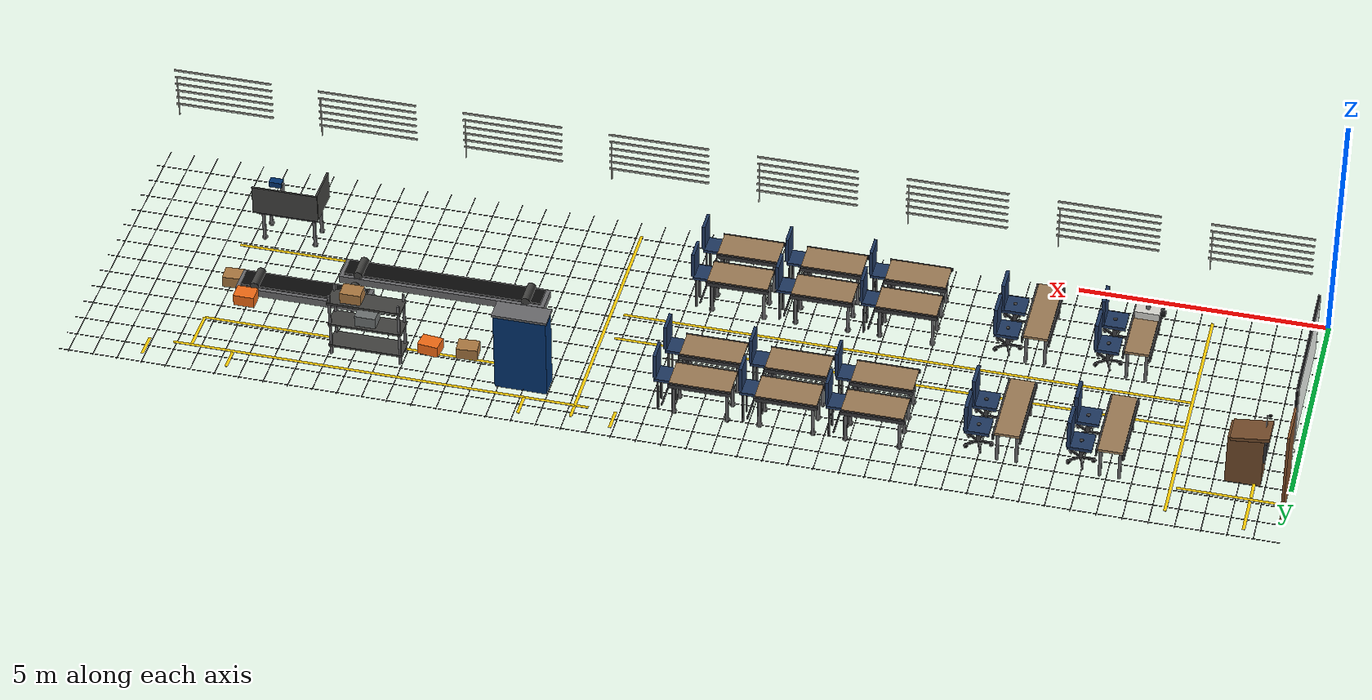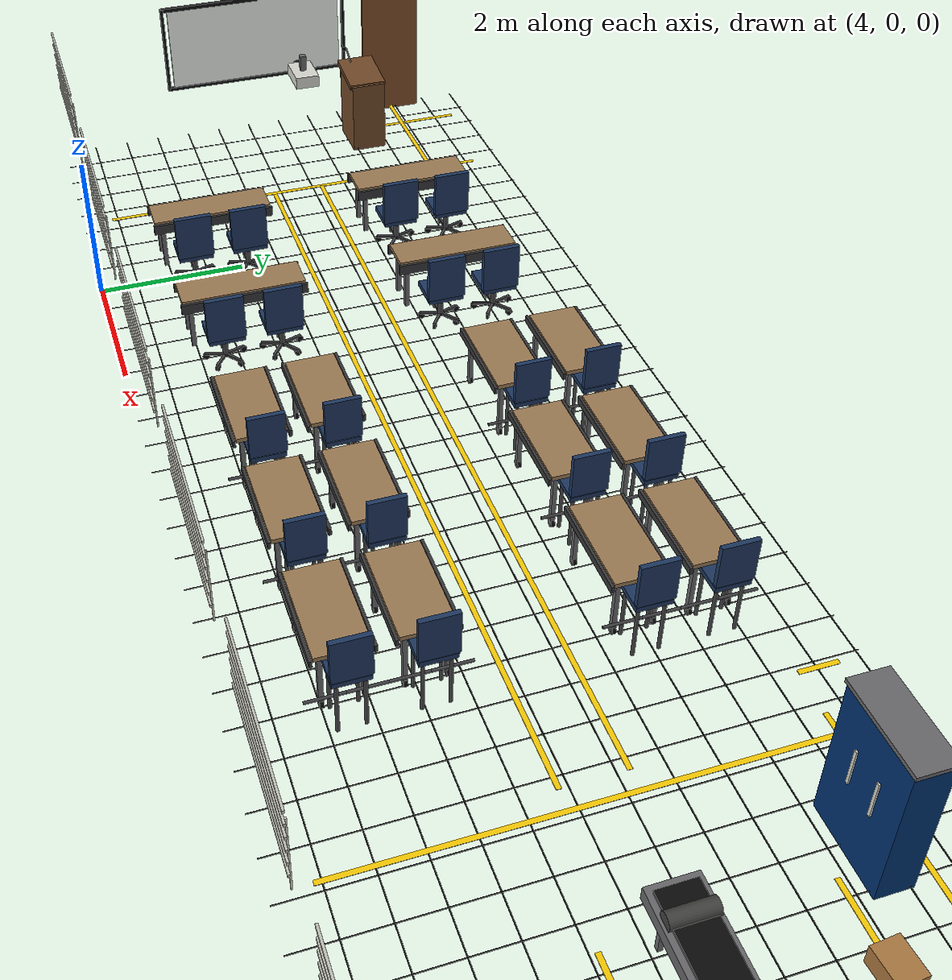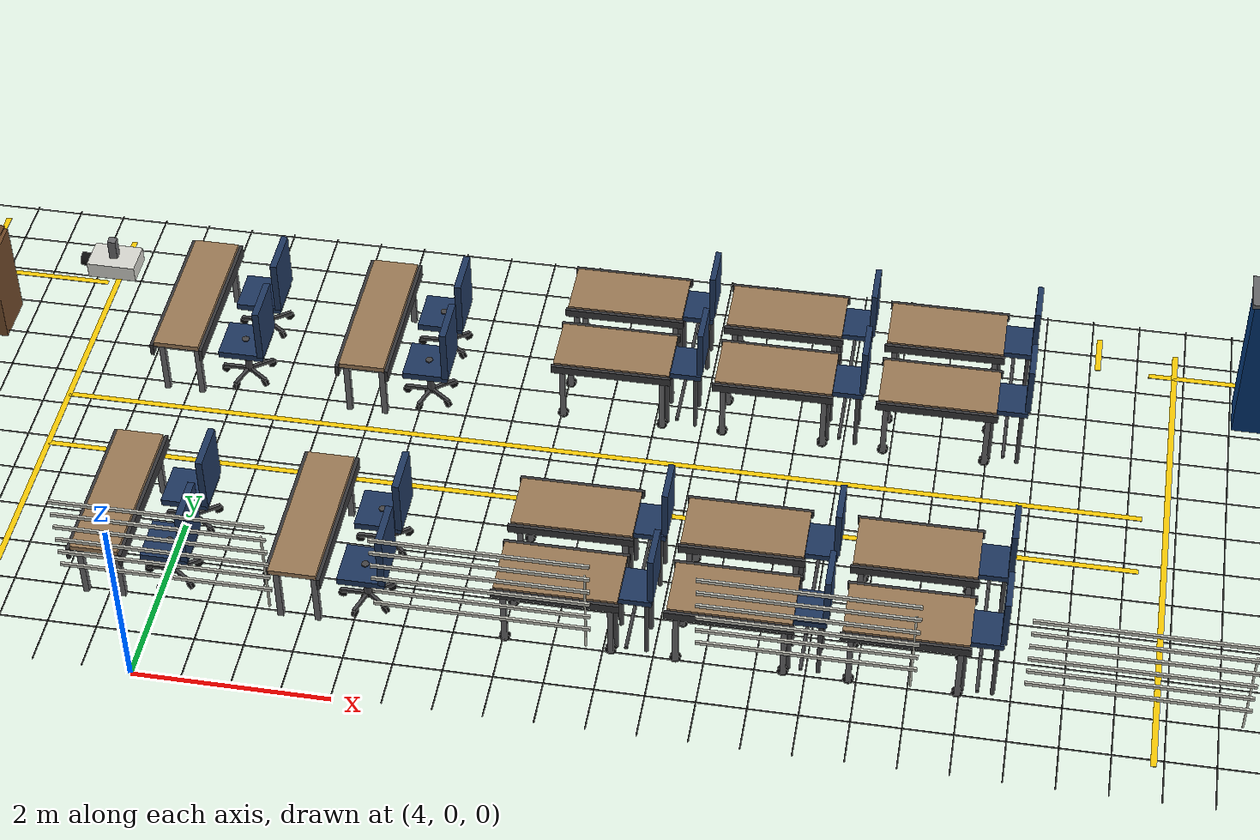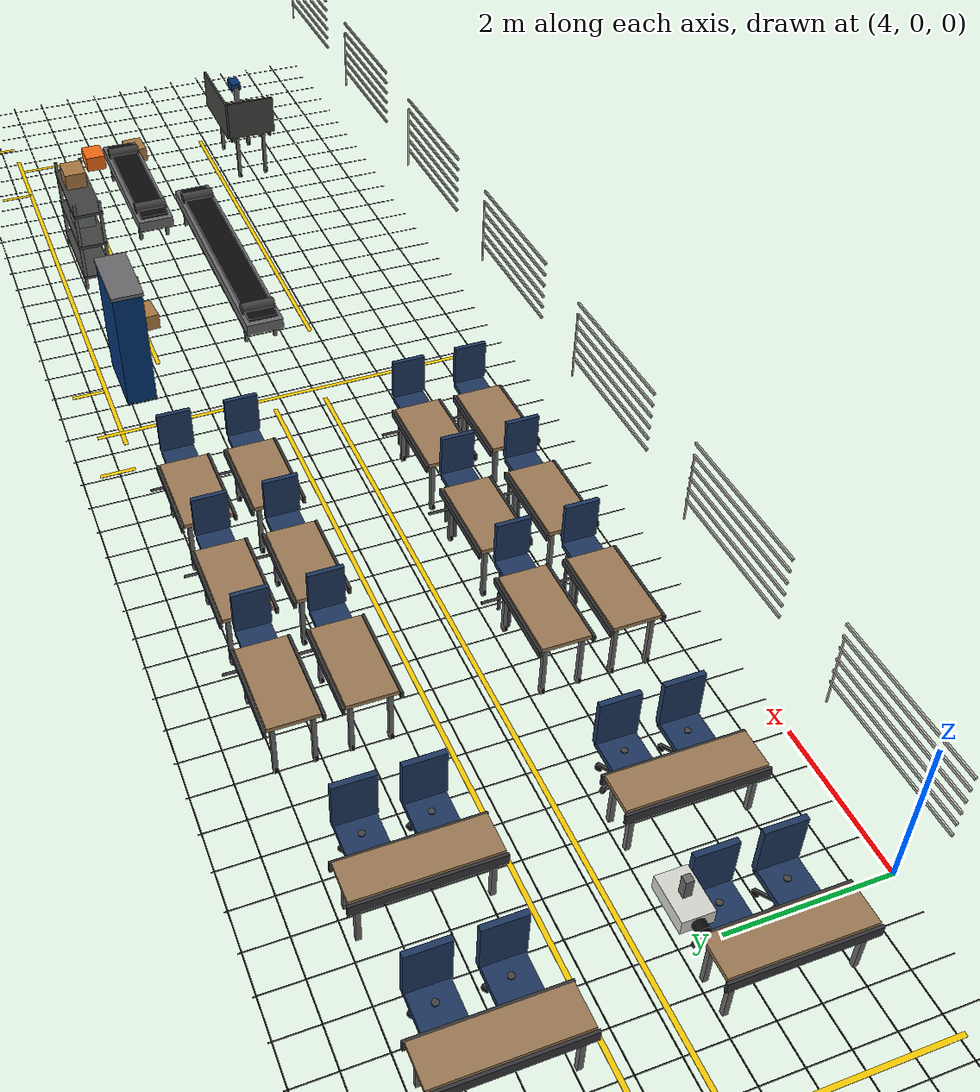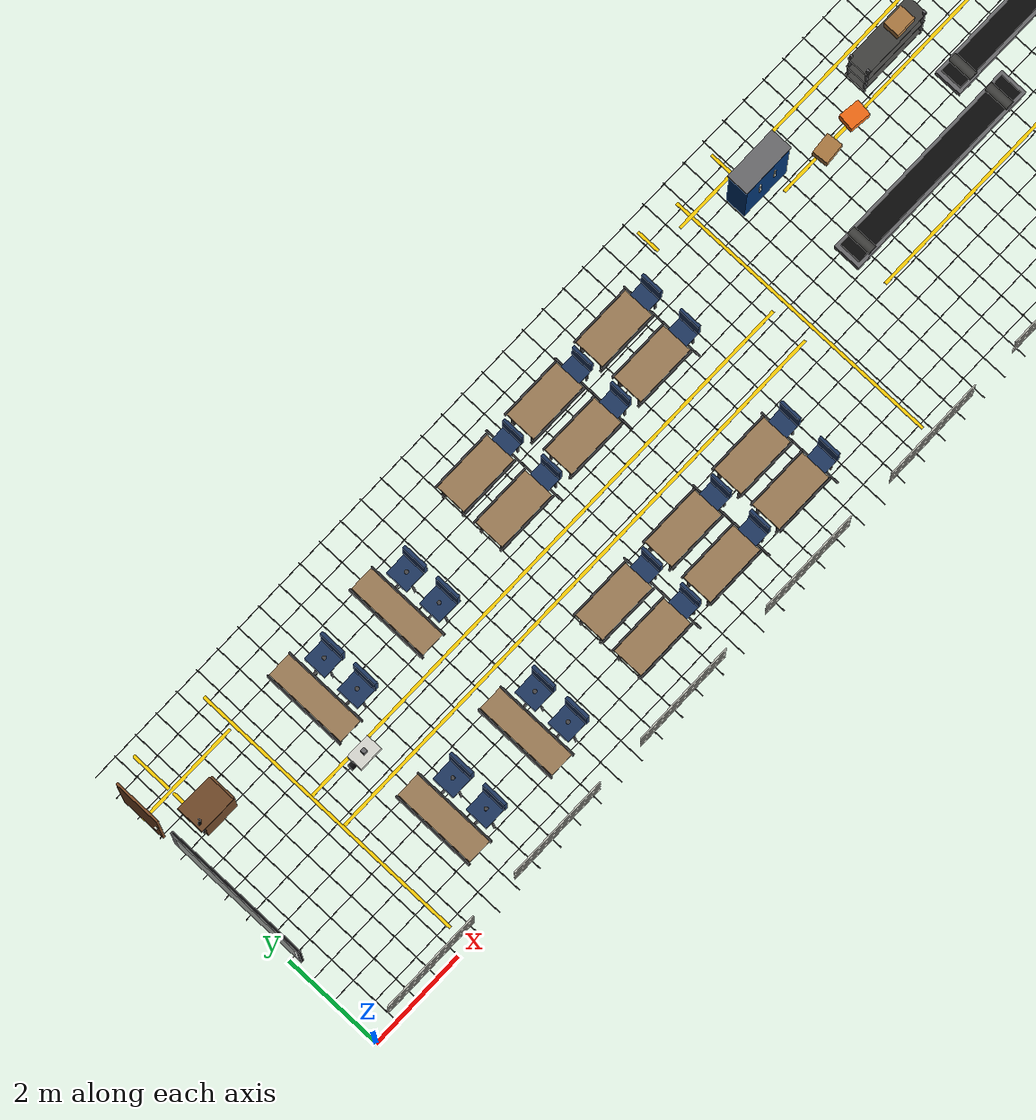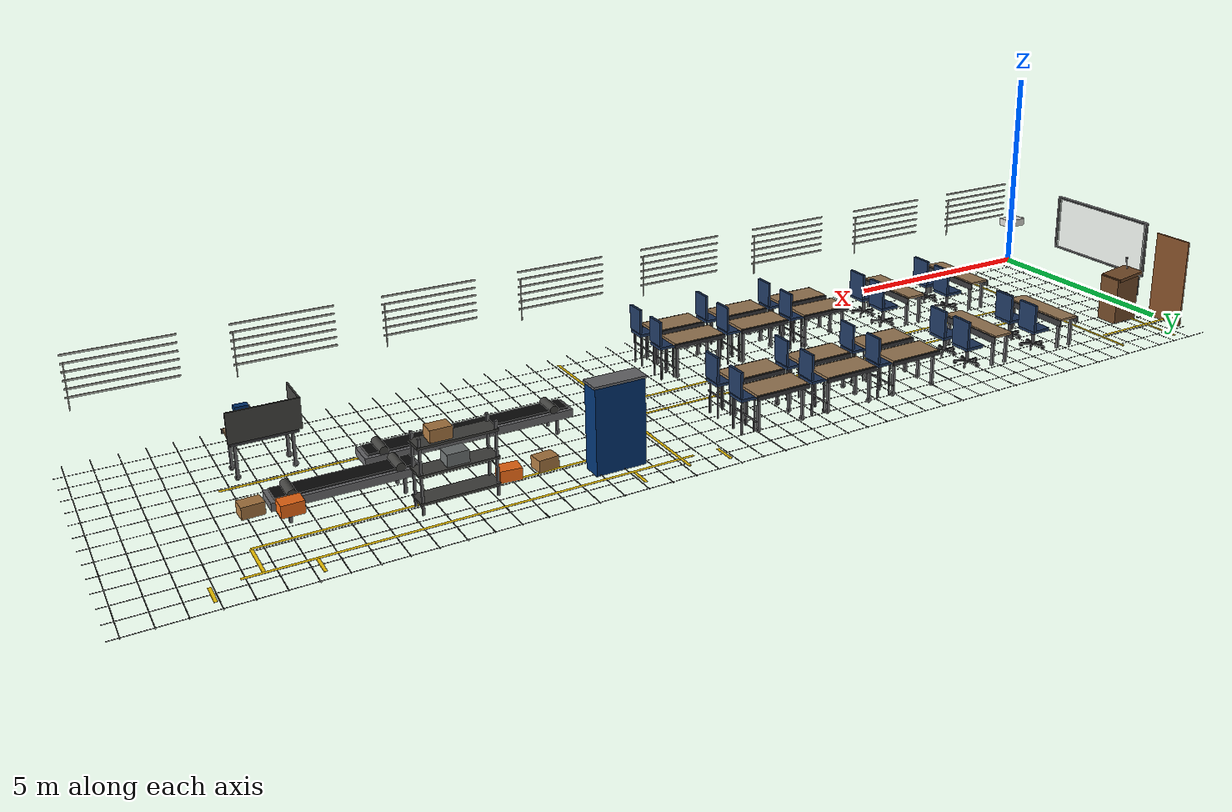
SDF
<?xml version="1.0" ?>
<sdf version="1.10">
  <model name="room_427_furnishings">
    <static>true</static>

    <link name="tile_seam_x_1">
      <pose>0.5 3.27 0.032 0 0 0</pose>
      <visual name="visual">
        <geometry><box><size>0.012 6.54 0.004</size></box></geometry>
        <material>
          <ambient>0.13 0.13 0.13 1</ambient>
          <diffuse>0.16 0.16 0.15 1</diffuse>
          <specular>0.04 0.04 0.04 1</specular>
        </material>
      </visual>
    </link>
    <link name="tile_seam_x_2">
      <pose>1 3.27 0.032 0 0 0</pose>
      <visual name="visual">
        <geometry><box><size>0.012 6.54 0.004</size></box></geometry>
        <material>
          <ambient>0.13 0.13 0.13 1</ambient>
          <diffuse>0.16 0.16 0.15 1</diffuse>
          <specular>0.04 0.04 0.04 1</specular>
        </material>
      </visual>
    </link>
    <link name="tile_seam_x_3">
      <pose>1.5 3.27 0.032 0 0 0</pose>
      <visual name="visual">
        <geometry><box><size>0.012 6.54 0.004</size></box></geometry>
        <material>
          <ambient>0.13 0.13 0.13 1</ambient>
          <diffuse>0.16 0.16 0.15 1</diffuse>
          <specular>0.04 0.04 0.04 1</specular>
        </material>
      </visual>
    </link>
    <link name="tile_seam_x_4">
      <pose>2 3.27 0.032 0 0 0</pose>
      <visual name="visual">
        <geometry><box><size>0.012 6.54 0.004</size></box></geometry>
        <material>
          <ambient>0.13 0.13 0.13 1</ambient>
          <diffuse>0.16 0.16 0.15 1</diffuse>
          <specular>0.04 0.04 0.04 1</specular>
        </material>
      </visual>
    </link>
    <link name="tile_seam_x_5">
      <pose>2.5 3.27 0.032 0 0 0</pose>
      <visual name="visual">
        <geometry><box><size>0.012 6.54 0.004</size></box></geometry>
        <material>
          <ambient>0.13 0.13 0.13 1</ambient>
          <diffuse>0.16 0.16 0.15 1</diffuse>
          <specular>0.04 0.04 0.04 1</specular>
        </material>
      </visual>
    </link>
    <link name="tile_seam_x_6">
      <pose>3 3.27 0.032 0 0 0</pose>
      <visual name="visual">
        <geometry><box><size>0.012 6.54 0.004</size></box></geometry>
        <material>
          <ambient>0.13 0.13 0.13 1</ambient>
          <diffuse>0.16 0.16 0.15 1</diffuse>
          <specular>0.04 0.04 0.04 1</specular>
        </material>
      </visual>
    </link>
    <link name="tile_seam_x_7">
      <pose>3.5 3.27 0.032 0 0 0</pose>
      <visual name="visual">
        <geometry><box><size>0.012 6.54 0.004</size></box></geometry>
        <material>
          <ambient>0.13 0.13 0.13 1</ambient>
          <diffuse>0.16 0.16 0.15 1</diffuse>
          <specular>0.04 0.04 0.04 1</specular>
        </material>
      </visual>
    </link>
    <link name="tile_seam_x_8">
      <pose>4 3.27 0.032 0 0 0</pose>
      <visual name="visual">
        <geometry><box><size>0.012 6.54 0.004</size></box></geometry>
        <material>
          <ambient>0.13 0.13 0.13 1</ambient>
          <diffuse>0.16 0.16 0.15 1</diffuse>
          <specular>0.04 0.04 0.04 1</specular>
        </material>
      </visual>
    </link>
    <link name="tile_seam_x_9">
      <pose>4.5 3.27 0.032 0 0 0</pose>
      <visual name="visual">
        <geometry><box><size>0.012 6.54 0.004</size></box></geometry>
        <material>
          <ambient>0.13 0.13 0.13 1</ambient>
          <diffuse>0.16 0.16 0.15 1</diffuse>
          <specular>0.04 0.04 0.04 1</specular>
        </material>
      </visual>
    </link>
    <link name="tile_seam_x_10">
      <pose>5 3.27 0.032 0 0 0</pose>
      <visual name="visual">
        <geometry><box><size>0.012 6.54 0.004</size></box></geometry>
        <material>
          <ambient>0.13 0.13 0.13 1</ambient>
          <diffuse>0.16 0.16 0.15 1</diffuse>
          <specular>0.04 0.04 0.04 1</specular>
        </material>
      </visual>
    </link>
    <link name="tile_seam_x_11">
      <pose>5.5 3.27 0.032 0 0 0</pose>
      <visual name="visual">
        <geometry><box><size>0.012 6.54 0.004</size></box></geometry>
        <material>
          <ambient>0.13 0.13 0.13 1</ambient>
          <diffuse>0.16 0.16 0.15 1</diffuse>
          <specular>0.04 0.04 0.04 1</specular>
        </material>
      </visual>
    </link>
    <link name="tile_seam_x_12">
      <pose>6 3.27 0.032 0 0 0</pose>
      <visual name="visual">
        <geometry><box><size>0.012 6.54 0.004</size></box></geometry>
        <material>
          <ambient>0.13 0.13 0.13 1</ambient>
          <diffuse>0.16 0.16 0.15 1</diffuse>
          <specular>0.04 0.04 0.04 1</specular>
        </material>
      </visual>
    </link>
    <link name="tile_seam_x_13">
      <pose>6.5 3.27 0.032 0 0 0</pose>
      <visual name="visual">
        <geometry><box><size>0.012 6.54 0.004</size></box></geometry>
        <material>
          <ambient>0.13 0.13 0.13 1</ambient>
          <diffuse>0.16 0.16 0.15 1</diffuse>
          <specular>0.04 0.04 0.04 1</specular>
        </material>
      </visual>
    </link>
    <link name="tile_seam_x_14">
      <pose>7 3.27 0.032 0 0 0</pose>
      <visual name="visual">
        <geometry><box><size>0.012 6.54 0.004</size></box></geometry>
        <material>
          <ambient>0.13 0.13 0.13 1</ambient>
          <diffuse>0.16 0.16 0.15 1</diffuse>
          <specular>0.04 0.04 0.04 1</specular>
        </material>
      </visual>
    </link>
    <link name="tile_seam_x_15">
      <pose>7.5 3.27 0.032 0 0 0</pose>
      <visual name="visual">
        <geometry><box><size>0.012 6.54 0.004</size></box></geometry>
        <material>
          <ambient>0.13 0.13 0.13 1</ambient>
          <diffuse>0.16 0.16 0.15 1</diffuse>
          <specular>0.04 0.04 0.04 1</specular>
        </material>
      </visual>
    </link>
    <link name="tile_seam_x_16">
      <pose>8 3.27 0.032 0 0 0</pose>
      <visual name="visual">
        <geometry><box><size>0.012 6.54 0.004</size></box></geometry>
        <material>
          <ambient>0.13 0.13 0.13 1</ambient>
          <diffuse>0.16 0.16 0.15 1</diffuse>
          <specular>0.04 0.04 0.04 1</specular>
        </material>
      </visual>
    </link>
    <link name="tile_seam_x_17">
      <pose>8.5 3.27 0.032 0 0 0</pose>
      <visual name="visual">
        <geometry><box><size>0.012 6.54 0.004</size></box></geometry>
        <material>
          <ambient>0.13 0.13 0.13 1</ambient>
          <diffuse>0.16 0.16 0.15 1</diffuse>
          <specular>0.04 0.04 0.04 1</specular>
        </material>
      </visual>
    </link>
    <link name="tile_seam_x_18">
      <pose>9 3.27 0.032 0 0 0</pose>
      <visual name="visual">
        <geometry><box><size>0.012 6.54 0.004</size></box></geometry>
        <material>
          <ambient>0.13 0.13 0.13 1</ambient>
          <diffuse>0.16 0.16 0.15 1</diffuse>
          <specular>0.04 0.04 0.04 1</specular>
        </material>
      </visual>
    </link>
    <link name="tile_seam_x_19">
      <pose>9.5 3.27 0.032 0 0 0</pose>
      <visual name="visual">
        <geometry><box><size>0.012 6.54 0.004</size></box></geometry>
        <material>
          <ambient>0.13 0.13 0.13 1</ambient>
          <diffuse>0.16 0.16 0.15 1</diffuse>
          <specular>0.04 0.04 0.04 1</specular>
        </material>
      </visual>
    </link>
    <link name="tile_seam_x_20">
      <pose>10 3.27 0.032 0 0 0</pose>
      <visual name="visual">
        <geometry><box><size>0.012 6.54 0.004</size></box></geometry>
        <material>
          <ambient>0.13 0.13 0.13 1</ambient>
          <diffuse>0.16 0.16 0.15 1</diffuse>
          <specular>0.04 0.04 0.04 1</specular>
        </material>
      </visual>
    </link>
    <link name="tile_seam_x_21">
      <pose>10.5 3.27 0.032 0 0 0</pose>
      <visual name="visual">
        <geometry><box><size>0.012 6.54 0.004</size></box></geometry>
        <material>
          <ambient>0.13 0.13 0.13 1</ambient>
          <diffuse>0.16 0.16 0.15 1</diffuse>
          <specular>0.04 0.04 0.04 1</specular>
        </material>
      </visual>
    </link>
    <link name="tile_seam_x_22">
      <pose>11 3.27 0.032 0 0 0</pose>
      <visual name="visual">
        <geometry><box><size>0.012 6.54 0.004</size></box></geometry>
        <material>
          <ambient>0.13 0.13 0.13 1</ambient>
          <diffuse>0.16 0.16 0.15 1</diffuse>
          <specular>0.04 0.04 0.04 1</specular>
        </material>
      </visual>
    </link>
    <link name="tile_seam_x_23">
      <pose>11.5 3.27 0.032 0 0 0</pose>
      <visual name="visual">
        <geometry><box><size>0.012 6.54 0.004</size></box></geometry>
        <material>
          <ambient>0.13 0.13 0.13 1</ambient>
          <diffuse>0.16 0.16 0.15 1</diffuse>
          <specular>0.04 0.04 0.04 1</specular>
        </material>
      </visual>
    </link>
    <link name="tile_seam_x_24">
      <pose>12 3.27 0.032 0 0 0</pose>
      <visual name="visual">
        <geometry><box><size>0.012 6.54 0.004</size></box></geometry>
        <material>
          <ambient>0.13 0.13 0.13 1</ambient>
          <diffuse>0.16 0.16 0.15 1</diffuse>
          <specular>0.04 0.04 0.04 1</specular>
        </material>
      </visual>
    </link>
    <link name="tile_seam_x_25">
      <pose>12.5 3.27 0.032 0 0 0</pose>
      <visual name="visual">
        <geometry><box><size>0.012 6.54 0.004</size></box></geometry>
        <material>
          <ambient>0.13 0.13 0.13 1</ambient>
          <diffuse>0.16 0.16 0.15 1</diffuse>
          <specular>0.04 0.04 0.04 1</specular>
        </material>
      </visual>
    </link>
    <link name="tile_seam_x_26">
      <pose>13 3.27 0.032 0 0 0</pose>
      <visual name="visual">
        <geometry><box><size>0.012 6.54 0.004</size></box></geometry>
        <material>
          <ambient>0.13 0.13 0.13 1</ambient>
          <diffuse>0.16 0.16 0.15 1</diffuse>
          <specular>0.04 0.04 0.04 1</specular>
        </material>
      </visual>
    </link>
    <link name="tile_seam_x_27">
      <pose>13.5 3.27 0.032 0 0 0</pose>
      <visual name="visual">
        <geometry><box><size>0.012 6.54 0.004</size></box></geometry>
        <material>
          <ambient>0.13 0.13 0.13 1</ambient>
          <diffuse>0.16 0.16 0.15 1</diffuse>
          <specular>0.04 0.04 0.04 1</specular>
        </material>
      </visual>
    </link>
    <link name="tile_seam_x_28">
      <pose>14 3.27 0.032 0 0 0</pose>
      <visual name="visual">
        <geometry><box><size>0.012 6.54 0.004</size></box></geometry>
        <material>
          <ambient>0.13 0.13 0.13 1</ambient>
          <diffuse>0.16 0.16 0.15 1</diffuse>
          <specular>0.04 0.04 0.04 1</specular>
        </material>
      </visual>
    </link>
    <link name="tile_seam_x_29">
      <pose>14.5 3.27 0.032 0 0 0</pose>
      <visual name="visual">
        <geometry><box><size>0.012 6.54 0.004</size></box></geometry>
        <material>
          <ambient>0.13 0.13 0.13 1</ambient>
          <diffuse>0.16 0.16 0.15 1</diffuse>
          <specular>0.04 0.04 0.04 1</specular>
        </material>
      </visual>
    </link>
    <link name="tile_seam_x_30">
      <pose>15 3.27 0.032 0 0 0</pose>
      <visual name="visual">
        <geometry><box><size>0.012 6.54 0.004</size></box></geometry>
        <material>
          <ambient>0.13 0.13 0.13 1</ambient>
          <diffuse>0.16 0.16 0.15 1</diffuse>
          <specular>0.04 0.04 0.04 1</specular>
        </material>
      </visual>
    </link>
    <link name="tile_seam_x_31">
      <pose>15.5 3.27 0.032 0 0 0</pose>
      <visual name="visual">
        <geometry><box><size>0.012 6.54 0.004</size></box></geometry>
        <material>
          <ambient>0.13 0.13 0.13 1</ambient>
          <diffuse>0.16 0.16 0.15 1</diffuse>
          <specular>0.04 0.04 0.04 1</specular>
        </material>
      </visual>
    </link>
    <link name="tile_seam_x_32">
      <pose>16 3.27 0.032 0 0 0</pose>
      <visual name="visual">
        <geometry><box><size>0.012 6.54 0.004</size></box></geometry>
        <material>
          <ambient>0.13 0.13 0.13 1</ambient>
          <diffuse>0.16 0.16 0.15 1</diffuse>
          <specular>0.04 0.04 0.04 1</specular>
        </material>
      </visual>
    </link>
    <link name="tile_seam_x_33">
      <pose>16.5 3.27 0.032 0 0 0</pose>
      <visual name="visual">
        <geometry><box><size>0.012 6.54 0.004</size></box></geometry>
        <material>
          <ambient>0.13 0.13 0.13 1</ambient>
          <diffuse>0.16 0.16 0.15 1</diffuse>
          <specular>0.04 0.04 0.04 1</specular>
        </material>
      </visual>
    </link>
    <link name="tile_seam_x_34">
      <pose>17 3.27 0.032 0 0 0</pose>
      <visual name="visual">
        <geometry><box><size>0.012 6.54 0.004</size></box></geometry>
        <material>
          <ambient>0.13 0.13 0.13 1</ambient>
          <diffuse>0.16 0.16 0.15 1</diffuse>
          <specular>0.04 0.04 0.04 1</specular>
        </material>
      </visual>
    </link>
    <link name="tile_seam_x_35">
      <pose>17.5 3.27 0.032 0 0 0</pose>
      <visual name="visual">
        <geometry><box><size>0.012 6.54 0.004</size></box></geometry>
        <material>
          <ambient>0.13 0.13 0.13 1</ambient>
          <diffuse>0.16 0.16 0.15 1</diffuse>
          <specular>0.04 0.04 0.04 1</specular>
        </material>
      </visual>
    </link>
    <link name="tile_seam_x_36">
      <pose>18 3.27 0.032 0 0 0</pose>
      <visual name="visual">
        <geometry><box><size>0.012 6.54 0.004</size></box></geometry>
        <material>
          <ambient>0.13 0.13 0.13 1</ambient>
          <diffuse>0.16 0.16 0.15 1</diffuse>
          <specular>0.04 0.04 0.04 1</specular>
        </material>
      </visual>
    </link>
    <link name="tile_seam_x_37">
      <pose>18.5 3.27 0.032 0 0 0</pose>
      <visual name="visual">
        <geometry><box><size>0.012 6.54 0.004</size></box></geometry>
        <material>
          <ambient>0.13 0.13 0.13 1</ambient>
          <diffuse>0.16 0.16 0.15 1</diffuse>
          <specular>0.04 0.04 0.04 1</specular>
        </material>
      </visual>
    </link>
    <link name="tile_seam_x_38">
      <pose>19 3.27 0.032 0 0 0</pose>
      <visual name="visual">
        <geometry><box><size>0.012 6.54 0.004</size></box></geometry>
        <material>
          <ambient>0.13 0.13 0.13 1</ambient>
          <diffuse>0.16 0.16 0.15 1</diffuse>
          <specular>0.04 0.04 0.04 1</specular>
        </material>
      </visual>
    </link>
    <link name="tile_seam_x_39">
      <pose>19.5 3.27 0.032 0 0 0</pose>
      <visual name="visual">
        <geometry><box><size>0.012 6.54 0.004</size></box></geometry>
        <material>
          <ambient>0.13 0.13 0.13 1</ambient>
          <diffuse>0.16 0.16 0.15 1</diffuse>
          <specular>0.04 0.04 0.04 1</specular>
        </material>
      </visual>
    </link>
    <link name="tile_seam_x_40">
      <pose>20 3.27 0.032 0 0 0</pose>
      <visual name="visual">
        <geometry><box><size>0.012 6.54 0.004</size></box></geometry>
        <material>
          <ambient>0.13 0.13 0.13 1</ambient>
          <diffuse>0.16 0.16 0.15 1</diffuse>
          <specular>0.04 0.04 0.04 1</specular>
        </material>
      </visual>
    </link>
    <link name="tile_seam_x_41">
      <pose>20.5 3.27 0.032 0 0 0</pose>
      <visual name="visual">
        <geometry><box><size>0.012 6.54 0.004</size></box></geometry>
        <material>
          <ambient>0.13 0.13 0.13 1</ambient>
          <diffuse>0.16 0.16 0.15 1</diffuse>
          <specular>0.04 0.04 0.04 1</specular>
        </material>
      </visual>
    </link>
    <link name="tile_seam_x_42">
      <pose>21 3.27 0.032 0 0 0</pose>
      <visual name="visual">
        <geometry><box><size>0.012 6.54 0.004</size></box></geometry>
        <material>
          <ambient>0.13 0.13 0.13 1</ambient>
          <diffuse>0.16 0.16 0.15 1</diffuse>
          <specular>0.04 0.04 0.04 1</specular>
        </material>
      </visual>
    </link>
    <link name="tile_seam_x_43">
      <pose>21.5 3.27 0.032 0 0 0</pose>
      <visual name="visual">
        <geometry><box><size>0.012 6.54 0.004</size></box></geometry>
        <material>
          <ambient>0.13 0.13 0.13 1</ambient>
          <diffuse>0.16 0.16 0.15 1</diffuse>
          <specular>0.04 0.04 0.04 1</specular>
        </material>
      </visual>
    </link>
    <link name="tile_seam_x_44">
      <pose>22 3.27 0.032 0 0 0</pose>
      <visual name="visual">
        <geometry><box><size>0.012 6.54 0.004</size></box></geometry>
        <material>
          <ambient>0.13 0.13 0.13 1</ambient>
          <diffuse>0.16 0.16 0.15 1</diffuse>
          <specular>0.04 0.04 0.04 1</specular>
        </material>
      </visual>
    </link>
    <link name="tile_seam_x_45">
      <pose>22.5 3.27 0.032 0 0 0</pose>
      <visual name="visual">
        <geometry><box><size>0.012 6.54 0.004</size></box></geometry>
        <material>
          <ambient>0.13 0.13 0.13 1</ambient>
          <diffuse>0.16 0.16 0.15 1</diffuse>
          <specular>0.04 0.04 0.04 1</specular>
        </material>
      </visual>
    </link>
    <link name="tile_seam_x_46">
      <pose>23 3.27 0.032 0 0 0</pose>
      <visual name="visual">
        <geometry><box><size>0.012 6.54 0.004</size></box></geometry>
        <material>
          <ambient>0.13 0.13 0.13 1</ambient>
          <diffuse>0.16 0.16 0.15 1</diffuse>
          <specular>0.04 0.04 0.04 1</specular>
        </material>
      </visual>
    </link>
    <link name="tile_seam_x_47">
      <pose>23.5 3.27 0.032 0 0 0</pose>
      <visual name="visual">
        <geometry><box><size>0.012 6.54 0.004</size></box></geometry>
        <material>
          <ambient>0.13 0.13 0.13 1</ambient>
          <diffuse>0.16 0.16 0.15 1</diffuse>
          <specular>0.04 0.04 0.04 1</specular>
        </material>
      </visual>
    </link>
    <link name="tile_seam_x_48">
      <pose>24 3.27 0.032 0 0 0</pose>
      <visual name="visual">
        <geometry><box><size>0.012 6.54 0.004</size></box></geometry>
        <material>
          <ambient>0.13 0.13 0.13 1</ambient>
          <diffuse>0.16 0.16 0.15 1</diffuse>
          <specular>0.04 0.04 0.04 1</specular>
        </material>
      </visual>
    </link>
    <link name="tile_seam_y_1">
      <pose>12.1 0.5 0.033 0 0 0</pose>
      <visual name="visual">
        <geometry><box><size>24.2 0.012 0.004</size></box></geometry>
        <material>
          <ambient>0.13 0.13 0.13 1</ambient>
          <diffuse>0.16 0.16 0.15 1</diffuse>
          <specular>0.04 0.04 0.04 1</specular>
        </material>
      </visual>
    </link>
    <link name="tile_seam_y_2">
      <pose>12.1 1 0.033 0 0 0</pose>
      <visual name="visual">
        <geometry><box><size>24.2 0.012 0.004</size></box></geometry>
        <material>
          <ambient>0.13 0.13 0.13 1</ambient>
          <diffuse>0.16 0.16 0.15 1</diffuse>
          <specular>0.04 0.04 0.04 1</specular>
        </material>
      </visual>
    </link>
    <link name="tile_seam_y_3">
      <pose>12.1 1.5 0.033 0 0 0</pose>
      <visual name="visual">
        <geometry><box><size>24.2 0.012 0.004</size></box></geometry>
        <material>
          <ambient>0.13 0.13 0.13 1</ambient>
          <diffuse>0.16 0.16 0.15 1</diffuse>
          <specular>0.04 0.04 0.04 1</specular>
        </material>
      </visual>
    </link>
    <link name="tile_seam_y_4">
      <pose>12.1 2 0.033 0 0 0</pose>
      <visual name="visual">
        <geometry><box><size>24.2 0.012 0.004</size></box></geometry>
        <material>
          <ambient>0.13 0.13 0.13 1</ambient>
          <diffuse>0.16 0.16 0.15 1</diffuse>
          <specular>0.04 0.04 0.04 1</specular>
        </material>
      </visual>
    </link>
    <link name="tile_seam_y_5">
      <pose>12.1 2.5 0.033 0 0 0</pose>
      <visual name="visual">
        <geometry><box><size>24.2 0.012 0.004</size></box></geometry>
        <material>
          <ambient>0.13 0.13 0.13 1</ambient>
          <diffuse>0.16 0.16 0.15 1</diffuse>
          <specular>0.04 0.04 0.04 1</specular>
        </material>
      </visual>
    </link>
    <link name="tile_seam_y_6">
      <pose>12.1 3 0.033 0 0 0</pose>
      <visual name="visual">
        <geometry><box><size>24.2 0.012 0.004</size></box></geometry>
        <material>
          <ambient>0.13 0.13 0.13 1</ambient>
          <diffuse>0.16 0.16 0.15 1</diffuse>
          <specular>0.04 0.04 0.04 1</specular>
        </material>
      </visual>
    </link>
    <link name="tile_seam_y_7">
      <pose>12.1 3.5 0.033 0 0 0</pose>
      <visual name="visual">
        <geometry><box><size>24.2 0.012 0.004</size></box></geometry>
        <material>
          <ambient>0.13 0.13 0.13 1</ambient>
          <diffuse>0.16 0.16 0.15 1</diffuse>
          <specular>0.04 0.04 0.04 1</specular>
        </material>
      </visual>
    </link>
    <link name="tile_seam_y_8">
      <pose>12.1 4 0.033 0 0 0</pose>
      <visual name="visual">
        <geometry><box><size>24.2 0.012 0.004</size></box></geometry>
        <material>
          <ambient>0.13 0.13 0.13 1</ambient>
          <diffuse>0.16 0.16 0.15 1</diffuse>
          <specular>0.04 0.04 0.04 1</specular>
        </material>
      </visual>
    </link>
    <link name="tile_seam_y_9">
      <pose>12.1 4.5 0.033 0 0 0</pose>
      <visual name="visual">
        <geometry><box><size>24.2 0.012 0.004</size></box></geometry>
        <material>
          <ambient>0.13 0.13 0.13 1</ambient>
          <diffuse>0.16 0.16 0.15 1</diffuse>
          <specular>0.04 0.04 0.04 1</specular>
        </material>
      </visual>
    </link>
    <link name="tile_seam_y_10">
      <pose>12.1 5 0.033 0 0 0</pose>
      <visual name="visual">
        <geometry><box><size>24.2 0.012 0.004</size></box></geometry>
        <material>
          <ambient>0.13 0.13 0.13 1</ambient>
          <diffuse>0.16 0.16 0.15 1</diffuse>
          <specular>0.04 0.04 0.04 1</specular>
        </material>
      </visual>
    </link>
    <link name="tile_seam_y_11">
      <pose>12.1 5.5 0.033 0 0 0</pose>
      <visual name="visual">
        <geometry><box><size>24.2 0.012 0.004</size></box></geometry>
        <material>
          <ambient>0.13 0.13 0.13 1</ambient>
          <diffuse>0.16 0.16 0.15 1</diffuse>
          <specular>0.04 0.04 0.04 1</specular>
        </material>
      </visual>
    </link>
    <link name="tile_seam_y_12">
      <pose>12.1 6 0.033 0 0 0</pose>
      <visual name="visual">
        <geometry><box><size>24.2 0.012 0.004</size></box></geometry>
        <material>
          <ambient>0.13 0.13 0.13 1</ambient>
          <diffuse>0.16 0.16 0.15 1</diffuse>
          <specular>0.04 0.04 0.04 1</specular>
        </material>
      </visual>
    </link>
    <link name="tile_seam_y_13">
      <pose>12.1 6.5 0.033 0 0 0</pose>
      <visual name="visual">
        <geometry><box><size>24.2 0.012 0.004</size></box></geometry>
        <material>
          <ambient>0.13 0.13 0.13 1</ambient>
          <diffuse>0.16 0.16 0.15 1</diffuse>
          <specular>0.04 0.04 0.04 1</specular>
        </material>
      </visual>
    </link>
    <link name="yellow_tape_front_teaching_clearance">
      <pose>2.25 3.27 0.036 0 0 1.5708</pose>
      <visual name="visual">
        <geometry><box><size>5.7 0.06 0.006</size></box></geometry>
        <material>
          <ambient>1.0 0.82 0.02 1</ambient>
          <diffuse>1.0 0.82 0.02 1</diffuse>
          <specular>0.25 0.22 0.04 1</specular>
        </material>
      </visual>
    </link>
    <link name="yellow_tape_student_aisle_window_edge">
      <pose>7.95 2.9 0.036 0 0 0</pose>
      <visual name="visual">
        <geometry><box><size>11.4 0.06 0.006</size></box></geometry>
        <material>
          <ambient>1.0 0.82 0.02 1</ambient>
          <diffuse>1.0 0.82 0.02 1</diffuse>
          <specular>0.25 0.22 0.04 1</specular>
        </material>
      </visual>
    </link>
    <link name="yellow_tape_student_aisle_door_edge">
      <pose>7.95 3.64 0.036 0 0 0</pose>
      <visual name="visual">
        <geometry><box><size>11.4 0.06 0.006</size></box></geometry>
        <material>
          <ambient>1.0 0.82 0.02 1</ambient>
          <diffuse>1.0 0.82 0.02 1</diffuse>
          <specular>0.25 0.22 0.04 1</specular>
        </material>
      </visual>
    </link>
    <link name="yellow_tape_class_conveyor_divider">
      <pose>13.9 3.27 0.036 0 0 1.5708</pose>
      <visual name="visual">
        <geometry><box><size>5.7 0.06 0.006</size></box></geometry>
        <material>
          <ambient>1.0 0.82 0.02 1</ambient>
          <diffuse>1.0 0.82 0.02 1</diffuse>
          <specular>0.25 0.22 0.04 1</specular>
        </material>
      </visual>
    </link>
    <link name="yellow_tape_front_door_approach">
      <pose>1.1 5.42 0.036 0 0 0</pose>
      <visual name="visual">
        <geometry><box><size>2.1 0.06 0.006</size></box></geometry>
        <material>
          <ambient>1.0 0.82 0.02 1</ambient>
          <diffuse>1.0 0.82 0.02 1</diffuse>
          <specular>0.25 0.22 0.04 1</specular>
        </material>
      </visual>
    </link>
    <link name="yellow_tape_front_door_side_mark_a">
      <pose>0.72 4.96 0.036 0 0 1.5708</pose>
      <visual name="visual">
        <geometry><box><size>0.82 0.06 0.006</size></box></geometry>
        <material>
          <ambient>1.0 0.82 0.02 1</ambient>
          <diffuse>1.0 0.82 0.02 1</diffuse>
          <specular>0.25 0.22 0.04 1</specular>
        </material>
      </visual>
    </link>
    <link name="yellow_tape_front_door_side_mark_b">
      <pose>0.72 5.88 0.036 0 0 1.5708</pose>
      <visual name="visual">
        <geometry><box><size>0.82 0.06 0.006</size></box></geometry>
        <material>
          <ambient>1.0 0.82 0.02 1</ambient>
          <diffuse>1.0 0.82 0.02 1</diffuse>
          <specular>0.25 0.22 0.04 1</specular>
        </material>
      </visual>
    </link>
    <link name="yellow_tape_back_door_run">
      <pose>17.85 5.78 0.036 0 0 0</pose>
      <visual name="visual">
        <geometry><box><size>8.45 0.06 0.006</size></box></geometry>
        <material>
          <ambient>1.0 0.82 0.02 1</ambient>
          <diffuse>1.0 0.82 0.02 1</diffuse>
          <specular>0.25 0.22 0.04 1</specular>
        </material>
      </visual>
    </link>
    <link name="yellow_tape_back_door_2_left_side">
      <pose>13.08 6.02 0.036 0 0 1.5708</pose>
      <visual name="visual">
        <geometry><box><size>0.48 0.06 0.006</size></box></geometry>
        <material>
          <ambient>1.0 0.82 0.02 1</ambient>
          <diffuse>1.0 0.82 0.02 1</diffuse>
          <specular>0.25 0.22 0.04 1</specular>
        </material>
      </visual>
    </link>
    <link name="yellow_tape_back_door_2_right_side">
      <pose>14.92 6.02 0.036 0 0 1.5708</pose>
      <visual name="visual">
        <geometry><box><size>0.48 0.06 0.006</size></box></geometry>
        <material>
          <ambient>1.0 0.82 0.02 1</ambient>
          <diffuse>1.0 0.82 0.02 1</diffuse>
          <specular>0.25 0.22 0.04 1</specular>
        </material>
      </visual>
    </link>
    <link name="yellow_tape_back_door_1_left_side">
      <pose>20.84 6.02 0.036 0 0 1.5708</pose>
      <visual name="visual">
        <geometry><box><size>0.48 0.06 0.006</size></box></geometry>
        <material>
          <ambient>1.0 0.82 0.02 1</ambient>
          <diffuse>1.0 0.82 0.02 1</diffuse>
          <specular>0.25 0.22 0.04 1</specular>
        </material>
      </visual>
    </link>
    <link name="yellow_tape_back_door_1_right_side">
      <pose>22.56 6.02 0.036 0 0 1.5708</pose>
      <visual name="visual">
        <geometry><box><size>0.48 0.06 0.006</size></box></geometry>
        <material>
          <ambient>1.0 0.82 0.02 1</ambient>
          <diffuse>1.0 0.82 0.02 1</diffuse>
          <specular>0.25 0.22 0.04 1</specular>
        </material>
      </visual>
    </link>
    <link name="yellow_tape_conveyor_front_boundary">
      <pose>18.5 2.58 0.036 0 0 0</pose>
      <visual name="visual">
        <geometry><box><size>6.4 0.06 0.006</size></box></geometry>
        <material>
          <ambient>1.0 0.82 0.02 1</ambient>
          <diffuse>1.0 0.82 0.02 1</diffuse>
          <specular>0.25 0.22 0.04 1</specular>
        </material>
      </visual>
    </link>
    <link name="yellow_tape_conveyor_back_boundary">
      <pose>18.5 4.92 0.036 0 0 0</pose>
      <visual name="visual">
        <geometry><box><size>6.4 0.06 0.006</size></box></geometry>
        <material>
          <ambient>1.0 0.82 0.02 1</ambient>
          <diffuse>1.0 0.82 0.02 1</diffuse>
          <specular>0.25 0.22 0.04 1</specular>
        </material>
      </visual>
    </link>
    <link name="yellow_tape_conveyor_exit_to_back_door">
      <pose>21.7 5.35 0.036 0 0 1.5708</pose>
      <visual name="visual">
        <geometry><box><size>0.86 0.06 0.006</size></box></geometry>
        <material>
          <ambient>1.0 0.82 0.02 1</ambient>
          <diffuse>1.0 0.82 0.02 1</diffuse>
          <specular>0.25 0.22 0.04 1</specular>
        </material>
      </visual>
    </link>
    <link name="blind_1_1">
      <pose>1.45 0.085 2.25 0 0 0</pose>
      <visual name="visual">
        <geometry><box><size>2.06 0.024 0.035</size></box></geometry>
        <material>
          <ambient>0.72 0.72 0.68 1</ambient>
          <diffuse>0.78 0.78 0.74 1</diffuse>
          <specular>0.12 0.12 0.12 1</specular>
        </material>
      </visual>
    </link>
    <link name="blind_1_2">
      <pose>1.45 0.085 2.08 0 0 0</pose>
      <visual name="visual">
        <geometry><box><size>2.06 0.024 0.035</size></box></geometry>
        <material>
          <ambient>0.72 0.72 0.68 1</ambient>
          <diffuse>0.78 0.78 0.74 1</diffuse>
          <specular>0.12 0.12 0.12 1</specular>
        </material>
      </visual>
    </link>
    <link name="blind_1_3">
      <pose>1.45 0.085 1.91 0 0 0</pose>
      <visual name="visual">
        <geometry><box><size>2.06 0.024 0.035</size></box></geometry>
        <material>
          <ambient>0.72 0.72 0.68 1</ambient>
          <diffuse>0.78 0.78 0.74 1</diffuse>
          <specular>0.12 0.12 0.12 1</specular>
        </material>
      </visual>
    </link>
    <link name="blind_1_4">
      <pose>1.45 0.085 1.74 0 0 0</pose>
      <visual name="visual">
        <geometry><box><size>2.06 0.024 0.035</size></box></geometry>
        <material>
          <ambient>0.72 0.72 0.68 1</ambient>
          <diffuse>0.78 0.78 0.74 1</diffuse>
          <specular>0.12 0.12 0.12 1</specular>
        </material>
      </visual>
    </link>
    <link name="blind_1_5">
      <pose>1.45 0.085 1.57 0 0 0</pose>
      <visual name="visual">
        <geometry><box><size>2.06 0.024 0.035</size></box></geometry>
        <material>
          <ambient>0.72 0.72 0.68 1</ambient>
          <diffuse>0.78 0.78 0.74 1</diffuse>
          <specular>0.12 0.12 0.12 1</specular>
        </material>
      </visual>
    </link>
    <link name="blind_1_6">
      <pose>1.45 0.085 1.4 0 0 0</pose>
      <visual name="visual">
        <geometry><box><size>2.06 0.024 0.035</size></box></geometry>
        <material>
          <ambient>0.72 0.72 0.68 1</ambient>
          <diffuse>0.78 0.78 0.74 1</diffuse>
          <specular>0.12 0.12 0.12 1</specular>
        </material>
      </visual>
    </link>
    <link name="blind_1_pull">
      <pose>2.43 0.105 1.62 0 0 0</pose>
      <visual name="visual">
        <geometry><box><size>0.018 0.018 0.96</size></box></geometry>
        <material>
          <ambient>0.78 0.78 0.72 1</ambient>
          <diffuse>0.86 0.86 0.80 1</diffuse>
          <specular>0.45 0.45 0.40 1</specular>
        </material>
      </visual>
    </link>
    <link name="blind_2_1">
      <pose>4.49 0.085 2.25 0 0 0</pose>
      <visual name="visual">
        <geometry><box><size>2.06 0.024 0.035</size></box></geometry>
        <material>
          <ambient>0.72 0.72 0.68 1</ambient>
          <diffuse>0.78 0.78 0.74 1</diffuse>
          <specular>0.12 0.12 0.12 1</specular>
        </material>
      </visual>
    </link>
    <link name="blind_2_2">
      <pose>4.49 0.085 2.08 0 0 0</pose>
      <visual name="visual">
        <geometry><box><size>2.06 0.024 0.035</size></box></geometry>
        <material>
          <ambient>0.72 0.72 0.68 1</ambient>
          <diffuse>0.78 0.78 0.74 1</diffuse>
          <specular>0.12 0.12 0.12 1</specular>
        </material>
      </visual>
    </link>
    <link name="blind_2_3">
      <pose>4.49 0.085 1.91 0 0 0</pose>
      <visual name="visual">
        <geometry><box><size>2.06 0.024 0.035</size></box></geometry>
        <material>
          <ambient>0.72 0.72 0.68 1</ambient>
          <diffuse>0.78 0.78 0.74 1</diffuse>
          <specular>0.12 0.12 0.12 1</specular>
        </material>
      </visual>
    </link>
    <link name="blind_2_4">
      <pose>4.49 0.085 1.74 0 0 0</pose>
      <visual name="visual">
        <geometry><box><size>2.06 0.024 0.035</size></box></geometry>
        <material>
          <ambient>0.72 0.72 0.68 1</ambient>
          <diffuse>0.78 0.78 0.74 1</diffuse>
          <specular>0.12 0.12 0.12 1</specular>
        </material>
      </visual>
    </link>
    <link name="blind_2_5">
      <pose>4.49 0.085 1.57 0 0 0</pose>
      <visual name="visual">
        <geometry><box><size>2.06 0.024 0.035</size></box></geometry>
        <material>
          <ambient>0.72 0.72 0.68 1</ambient>
          <diffuse>0.78 0.78 0.74 1</diffuse>
          <specular>0.12 0.12 0.12 1</specular>
        </material>
      </visual>
    </link>
    <link name="blind_2_6">
      <pose>4.49 0.085 1.4 0 0 0</pose>
      <visual name="visual">
        <geometry><box><size>2.06 0.024 0.035</size></box></geometry>
        <material>
          <ambient>0.72 0.72 0.68 1</ambient>
          <diffuse>0.78 0.78 0.74 1</diffuse>
          <specular>0.12 0.12 0.12 1</specular>
        </material>
      </visual>
    </link>
    <link name="blind_2_pull">
      <pose>5.47 0.105 1.62 0 0 0</pose>
      <visual name="visual">
        <geometry><box><size>0.018 0.018 0.96</size></box></geometry>
        <material>
          <ambient>0.78 0.78 0.72 1</ambient>
          <diffuse>0.86 0.86 0.80 1</diffuse>
          <specular>0.45 0.45 0.40 1</specular>
        </material>
      </visual>
    </link>
    <link name="blind_3_1">
      <pose>7.53 0.085 2.25 0 0 0</pose>
      <visual name="visual">
        <geometry><box><size>2.06 0.024 0.035</size></box></geometry>
        <material>
          <ambient>0.72 0.72 0.68 1</ambient>
          <diffuse>0.78 0.78 0.74 1</diffuse>
          <specular>0.12 0.12 0.12 1</specular>
        </material>
      </visual>
    </link>
    <link name="blind_3_2">
      <pose>7.53 0.085 2.08 0 0 0</pose>
      <visual name="visual">
        <geometry><box><size>2.06 0.024 0.035</size></box></geometry>
        <material>
          <ambient>0.72 0.72 0.68 1</ambient>
          <diffuse>0.78 0.78 0.74 1</diffuse>
          <specular>0.12 0.12 0.12 1</specular>
        </material>
      </visual>
    </link>
    <link name="blind_3_3">
      <pose>7.53 0.085 1.91 0 0 0</pose>
      <visual name="visual">
        <geometry><box><size>2.06 0.024 0.035</size></box></geometry>
        <material>
          <ambient>0.72 0.72 0.68 1</ambient>
          <diffuse>0.78 0.78 0.74 1</diffuse>
          <specular>0.12 0.12 0.12 1</specular>
        </material>
      </visual>
    </link>
    <link name="blind_3_4">
      <pose>7.53 0.085 1.74 0 0 0</pose>
      <visual name="visual">
        <geometry><box><size>2.06 0.024 0.035</size></box></geometry>
        <material>
          <ambient>0.72 0.72 0.68 1</ambient>
          <diffuse>0.78 0.78 0.74 1</diffuse>
          <specular>0.12 0.12 0.12 1</specular>
        </material>
      </visual>
    </link>
    <link name="blind_3_5">
      <pose>7.53 0.085 1.57 0 0 0</pose>
      <visual name="visual">
        <geometry><box><size>2.06 0.024 0.035</size></box></geometry>
        <material>
          <ambient>0.72 0.72 0.68 1</ambient>
          <diffuse>0.78 0.78 0.74 1</diffuse>
          <specular>0.12 0.12 0.12 1</specular>
        </material>
      </visual>
    </link>
    <link name="blind_3_6">
      <pose>7.53 0.085 1.4 0 0 0</pose>
      <visual name="visual">
        <geometry><box><size>2.06 0.024 0.035</size></box></geometry>
        <material>
          <ambient>0.72 0.72 0.68 1</ambient>
          <diffuse>0.78 0.78 0.74 1</diffuse>
          <specular>0.12 0.12 0.12 1</specular>
        </material>
      </visual>
    </link>
    <link name="blind_3_pull">
      <pose>8.51 0.105 1.62 0 0 0</pose>
      <visual name="visual">
        <geometry><box><size>0.018 0.018 0.96</size></box></geometry>
        <material>
          <ambient>0.78 0.78 0.72 1</ambient>
          <diffuse>0.86 0.86 0.80 1</diffuse>
          <specular>0.45 0.45 0.40 1</specular>
        </material>
      </visual>
    </link>
    <link name="blind_4_1">
      <pose>10.57 0.085 2.25 0 0 0</pose>
      <visual name="visual">
        <geometry><box><size>2.06 0.024 0.035</size></box></geometry>
        <material>
          <ambient>0.72 0.72 0.68 1</ambient>
          <diffuse>0.78 0.78 0.74 1</diffuse>
          <specular>0.12 0.12 0.12 1</specular>
        </material>
      </visual>
    </link>
    <link name="blind_4_2">
      <pose>10.57 0.085 2.08 0 0 0</pose>
      <visual name="visual">
        <geometry><box><size>2.06 0.024 0.035</size></box></geometry>
        <material>
          <ambient>0.72 0.72 0.68 1</ambient>
          <diffuse>0.78 0.78 0.74 1</diffuse>
          <specular>0.12 0.12 0.12 1</specular>
        </material>
      </visual>
    </link>
    <link name="blind_4_3">
      <pose>10.57 0.085 1.91 0 0 0</pose>
      <visual name="visual">
        <geometry><box><size>2.06 0.024 0.035</size></box></geometry>
        <material>
          <ambient>0.72 0.72 0.68 1</ambient>
          <diffuse>0.78 0.78 0.74 1</diffuse>
          <specular>0.12 0.12 0.12 1</specular>
        </material>
      </visual>
    </link>
    <link name="blind_4_4">
      <pose>10.57 0.085 1.74 0 0 0</pose>
      <visual name="visual">
        <geometry><box><size>2.06 0.024 0.035</size></box></geometry>
        <material>
          <ambient>0.72 0.72 0.68 1</ambient>
          <diffuse>0.78 0.78 0.74 1</diffuse>
          <specular>0.12 0.12 0.12 1</specular>
        </material>
      </visual>
    </link>
    <link name="blind_4_5">
      <pose>10.57 0.085 1.57 0 0 0</pose>
      <visual name="visual">
        <geometry><box><size>2.06 0.024 0.035</size></box></geometry>
        <material>
          <ambient>0.72 0.72 0.68 1</ambient>
          <diffuse>0.78 0.78 0.74 1</diffuse>
          <specular>0.12 0.12 0.12 1</specular>
        </material>
      </visual>
    </link>
    <link name="blind_4_6">
      <pose>10.57 0.085 1.4 0 0 0</pose>
      <visual name="visual">
        <geometry><box><size>2.06 0.024 0.035</size></box></geometry>
        <material>
          <ambient>0.72 0.72 0.68 1</ambient>
          <diffuse>0.78 0.78 0.74 1</diffuse>
          <specular>0.12 0.12 0.12 1</specular>
        </material>
      </visual>
    </link>
    <link name="blind_4_pull">
      <pose>11.55 0.105 1.62 0 0 0</pose>
      <visual name="visual">
        <geometry><box><size>0.018 0.018 0.96</size></box></geometry>
        <material>
          <ambient>0.78 0.78 0.72 1</ambient>
          <diffuse>0.86 0.86 0.80 1</diffuse>
          <specular>0.45 0.45 0.40 1</specular>
        </material>
      </visual>
    </link>
    <link name="blind_5_1">
      <pose>13.61 0.085 2.25 0 0 0</pose>
      <visual name="visual">
        <geometry><box><size>2.06 0.024 0.035</size></box></geometry>
        <material>
          <ambient>0.72 0.72 0.68 1</ambient>
          <diffuse>0.78 0.78 0.74 1</diffuse>
          <specular>0.12 0.12 0.12 1</specular>
        </material>
      </visual>
    </link>
    <link name="blind_5_2">
      <pose>13.61 0.085 2.08 0 0 0</pose>
      <visual name="visual">
        <geometry><box><size>2.06 0.024 0.035</size></box></geometry>
        <material>
          <ambient>0.72 0.72 0.68 1</ambient>
          <diffuse>0.78 0.78 0.74 1</diffuse>
          <specular>0.12 0.12 0.12 1</specular>
        </material>
      </visual>
    </link>
    <link name="blind_5_3">
      <pose>13.61 0.085 1.91 0 0 0</pose>
      <visual name="visual">
        <geometry><box><size>2.06 0.024 0.035</size></box></geometry>
        <material>
          <ambient>0.72 0.72 0.68 1</ambient>
          <diffuse>0.78 0.78 0.74 1</diffuse>
          <specular>0.12 0.12 0.12 1</specular>
        </material>
      </visual>
    </link>
    <link name="blind_5_4">
      <pose>13.61 0.085 1.74 0 0 0</pose>
      <visual name="visual">
        <geometry><box><size>2.06 0.024 0.035</size></box></geometry>
        <material>
          <ambient>0.72 0.72 0.68 1</ambient>
          <diffuse>0.78 0.78 0.74 1</diffuse>
          <specular>0.12 0.12 0.12 1</specular>
        </material>
      </visual>
    </link>
    <link name="blind_5_5">
      <pose>13.61 0.085 1.57 0 0 0</pose>
      <visual name="visual">
        <geometry><box><size>2.06 0.024 0.035</size></box></geometry>
        <material>
          <ambient>0.72 0.72 0.68 1</ambient>
          <diffuse>0.78 0.78 0.74 1</diffuse>
          <specular>0.12 0.12 0.12 1</specular>
        </material>
      </visual>
    </link>
    <link name="blind_5_6">
      <pose>13.61 0.085 1.4 0 0 0</pose>
      <visual name="visual">
        <geometry><box><size>2.06 0.024 0.035</size></box></geometry>
        <material>
          <ambient>0.72 0.72 0.68 1</ambient>
          <diffuse>0.78 0.78 0.74 1</diffuse>
          <specular>0.12 0.12 0.12 1</specular>
        </material>
      </visual>
    </link>
    <link name="blind_5_pull">
      <pose>14.59 0.105 1.62 0 0 0</pose>
      <visual name="visual">
        <geometry><box><size>0.018 0.018 0.96</size></box></geometry>
        <material>
          <ambient>0.78 0.78 0.72 1</ambient>
          <diffuse>0.86 0.86 0.80 1</diffuse>
          <specular>0.45 0.45 0.40 1</specular>
        </material>
      </visual>
    </link>
    <link name="blind_6_1">
      <pose>16.65 0.085 2.25 0 0 0</pose>
      <visual name="visual">
        <geometry><box><size>2.06 0.024 0.035</size></box></geometry>
        <material>
          <ambient>0.72 0.72 0.68 1</ambient>
          <diffuse>0.78 0.78 0.74 1</diffuse>
          <specular>0.12 0.12 0.12 1</specular>
        </material>
      </visual>
    </link>
    <link name="blind_6_2">
      <pose>16.65 0.085 2.08 0 0 0</pose>
      <visual name="visual">
        <geometry><box><size>2.06 0.024 0.035</size></box></geometry>
        <material>
          <ambient>0.72 0.72 0.68 1</ambient>
          <diffuse>0.78 0.78 0.74 1</diffuse>
          <specular>0.12 0.12 0.12 1</specular>
        </material>
      </visual>
    </link>
    <link name="blind_6_3">
      <pose>16.65 0.085 1.91 0 0 0</pose>
      <visual name="visual">
        <geometry><box><size>2.06 0.024 0.035</size></box></geometry>
        <material>
          <ambient>0.72 0.72 0.68 1</ambient>
          <diffuse>0.78 0.78 0.74 1</diffuse>
          <specular>0.12 0.12 0.12 1</specular>
        </material>
      </visual>
    </link>
    <link name="blind_6_4">
      <pose>16.65 0.085 1.74 0 0 0</pose>
      <visual name="visual">
        <geometry><box><size>2.06 0.024 0.035</size></box></geometry>
        <material>
          <ambient>0.72 0.72 0.68 1</ambient>
          <diffuse>0.78 0.78 0.74 1</diffuse>
          <specular>0.12 0.12 0.12 1</specular>
        </material>
      </visual>
    </link>
    <link name="blind_6_5">
      <pose>16.65 0.085 1.57 0 0 0</pose>
      <visual name="visual">
        <geometry><box><size>2.06 0.024 0.035</size></box></geometry>
        <material>
          <ambient>0.72 0.72 0.68 1</ambient>
          <diffuse>0.78 0.78 0.74 1</diffuse>
          <specular>0.12 0.12 0.12 1</specular>
        </material>
      </visual>
    </link>
    <link name="blind_6_6">
      <pose>16.65 0.085 1.4 0 0 0</pose>
      <visual name="visual">
        <geometry><box><size>2.06 0.024 0.035</size></box></geometry>
        <material>
          <ambient>0.72 0.72 0.68 1</ambient>
          <diffuse>0.78 0.78 0.74 1</diffuse>
          <specular>0.12 0.12 0.12 1</specular>
        </material>
      </visual>
    </link>
    <link name="blind_6_pull">
      <pose>17.63 0.105 1.62 0 0 0</pose>
      <visual name="visual">
        <geometry><box><size>0.018 0.018 0.96</size></box></geometry>
        <material>
          <ambient>0.78 0.78 0.72 1</ambient>
          <diffuse>0.86 0.86 0.80 1</diffuse>
          <specular>0.45 0.45 0.40 1</specular>
        </material>
      </visual>
    </link>
    <link name="blind_7_1">
      <pose>19.69 0.085 2.25 0 0 0</pose>
      <visual name="visual">
        <geometry><box><size>2.06 0.024 0.035</size></box></geometry>
        <material>
          <ambient>0.72 0.72 0.68 1</ambient>
          <diffuse>0.78 0.78 0.74 1</diffuse>
          <specular>0.12 0.12 0.12 1</specular>
        </material>
      </visual>
    </link>
    <link name="blind_7_2">
      <pose>19.69 0.085 2.08 0 0 0</pose>
      <visual name="visual">
        <geometry><box><size>2.06 0.024 0.035</size></box></geometry>
        <material>
          <ambient>0.72 0.72 0.68 1</ambient>
          <diffuse>0.78 0.78 0.74 1</diffuse>
          <specular>0.12 0.12 0.12 1</specular>
        </material>
      </visual>
    </link>
    <link name="blind_7_3">
      <pose>19.69 0.085 1.91 0 0 0</pose>
      <visual name="visual">
        <geometry><box><size>2.06 0.024 0.035</size></box></geometry>
        <material>
          <ambient>0.72 0.72 0.68 1</ambient>
          <diffuse>0.78 0.78 0.74 1</diffuse>
          <specular>0.12 0.12 0.12 1</specular>
        </material>
      </visual>
    </link>
    <link name="blind_7_4">
      <pose>19.69 0.085 1.74 0 0 0</pose>
      <visual name="visual">
        <geometry><box><size>2.06 0.024 0.035</size></box></geometry>
        <material>
          <ambient>0.72 0.72 0.68 1</ambient>
          <diffuse>0.78 0.78 0.74 1</diffuse>
          <specular>0.12 0.12 0.12 1</specular>
        </material>
      </visual>
    </link>
    <link name="blind_7_5">
      <pose>19.69 0.085 1.57 0 0 0</pose>
      <visual name="visual">
        <geometry><box><size>2.06 0.024 0.035</size></box></geometry>
        <material>
          <ambient>0.72 0.72 0.68 1</ambient>
          <diffuse>0.78 0.78 0.74 1</diffuse>
          <specular>0.12 0.12 0.12 1</specular>
        </material>
      </visual>
    </link>
    <link name="blind_7_6">
      <pose>19.69 0.085 1.4 0 0 0</pose>
      <visual name="visual">
        <geometry><box><size>2.06 0.024 0.035</size></box></geometry>
        <material>
          <ambient>0.72 0.72 0.68 1</ambient>
          <diffuse>0.78 0.78 0.74 1</diffuse>
          <specular>0.12 0.12 0.12 1</specular>
        </material>
      </visual>
    </link>
    <link name="blind_7_pull">
      <pose>20.67 0.105 1.62 0 0 0</pose>
      <visual name="visual">
        <geometry><box><size>0.018 0.018 0.96</size></box></geometry>
        <material>
          <ambient>0.78 0.78 0.72 1</ambient>
          <diffuse>0.86 0.86 0.80 1</diffuse>
          <specular>0.45 0.45 0.40 1</specular>
        </material>
      </visual>
    </link>
    <link name="blind_8_1">
      <pose>22.73 0.085 2.25 0 0 0</pose>
      <visual name="visual">
        <geometry><box><size>2.06 0.024 0.035</size></box></geometry>
        <material>
          <ambient>0.72 0.72 0.68 1</ambient>
          <diffuse>0.78 0.78 0.74 1</diffuse>
          <specular>0.12 0.12 0.12 1</specular>
        </material>
      </visual>
    </link>
    <link name="blind_8_2">
      <pose>22.73 0.085 2.08 0 0 0</pose>
      <visual name="visual">
        <geometry><box><size>2.06 0.024 0.035</size></box></geometry>
        <material>
          <ambient>0.72 0.72 0.68 1</ambient>
          <diffuse>0.78 0.78 0.74 1</diffuse>
          <specular>0.12 0.12 0.12 1</specular>
        </material>
      </visual>
    </link>
    <link name="blind_8_3">
      <pose>22.73 0.085 1.91 0 0 0</pose>
      <visual name="visual">
        <geometry><box><size>2.06 0.024 0.035</size></box></geometry>
        <material>
          <ambient>0.72 0.72 0.68 1</ambient>
          <diffuse>0.78 0.78 0.74 1</diffuse>
          <specular>0.12 0.12 0.12 1</specular>
        </material>
      </visual>
    </link>
    <link name="blind_8_4">
      <pose>22.73 0.085 1.74 0 0 0</pose>
      <visual name="visual">
        <geometry><box><size>2.06 0.024 0.035</size></box></geometry>
        <material>
          <ambient>0.72 0.72 0.68 1</ambient>
          <diffuse>0.78 0.78 0.74 1</diffuse>
          <specular>0.12 0.12 0.12 1</specular>
        </material>
      </visual>
    </link>
    <link name="blind_8_5">
      <pose>22.73 0.085 1.57 0 0 0</pose>
      <visual name="visual">
        <geometry><box><size>2.06 0.024 0.035</size></box></geometry>
        <material>
          <ambient>0.72 0.72 0.68 1</ambient>
          <diffuse>0.78 0.78 0.74 1</diffuse>
          <specular>0.12 0.12 0.12 1</specular>
        </material>
      </visual>
    </link>
    <link name="blind_8_6">
      <pose>22.73 0.085 1.4 0 0 0</pose>
      <visual name="visual">
        <geometry><box><size>2.06 0.024 0.035</size></box></geometry>
        <material>
          <ambient>0.72 0.72 0.68 1</ambient>
          <diffuse>0.78 0.78 0.74 1</diffuse>
          <specular>0.12 0.12 0.12 1</specular>
        </material>
      </visual>
    </link>
    <link name="blind_8_pull">
      <pose>23.71 0.105 1.62 0 0 0</pose>
      <visual name="visual">
        <geometry><box><size>0.018 0.018 0.96</size></box></geometry>
        <material>
          <ambient>0.78 0.78 0.72 1</ambient>
          <diffuse>0.86 0.86 0.80 1</diffuse>
          <specular>0.45 0.45 0.40 1</specular>
        </material>
      </visual>
    </link>
    <link name="projector_screen_surface">
      <pose>0.085 3.2 1.58 0 0 0</pose>
      <visual name="visual">
        <geometry><box><size>0.035 2.7 1.28</size></box></geometry>
        <material>
          <ambient>0.88 0.90 0.88 1</ambient>
          <diffuse>0.96 0.98 0.96 1</diffuse>
          <specular>0.18 0.18 0.18 1</specular>
        </material>
      </visual>
    </link>
    <link name="projector_screen_top_rail">
      <pose>0.1 3.2 2.24 0 0 0</pose>
      <visual name="visual">
        <geometry><box><size>0.055 2.86 0.055</size></box></geometry>
        <material>
          <ambient>0.04 0.04 0.045 1</ambient>
          <diffuse>0.05 0.05 0.055 1</diffuse>
          <specular>0.12 0.12 0.12 1</specular>
        </material>
      </visual>
    </link>
    <link name="projector_screen_bottom_rail">
      <pose>0.1 3.2 0.92 0 0 0</pose>
      <visual name="visual">
        <geometry><box><size>0.055 2.86 0.045</size></box></geometry>
        <material>
          <ambient>0.04 0.04 0.045 1</ambient>
          <diffuse>0.05 0.05 0.055 1</diffuse>
          <specular>0.12 0.12 0.12 1</specular>
        </material>
      </visual>
    </link>
    <link name="projector_screen_left_rail">
      <pose>0.1 1.77 1.58 0 0 0</pose>
      <visual name="visual">
        <geometry><box><size>0.055 0.045 1.36</size></box></geometry>
        <material>
          <ambient>0.04 0.04 0.045 1</ambient>
          <diffuse>0.05 0.05 0.055 1</diffuse>
          <specular>0.12 0.12 0.12 1</specular>
        </material>
      </visual>
    </link>
    <link name="projector_screen_right_rail">
      <pose>0.1 4.63 1.58 0 0 0</pose>
      <visual name="visual">
        <geometry><box><size>0.055 0.045 1.36</size></box></geometry>
        <material>
          <ambient>0.04 0.04 0.045 1</ambient>
          <diffuse>0.05 0.05 0.055 1</diffuse>
          <specular>0.12 0.12 0.12 1</specular>
        </material>
      </visual>
    </link>
    <link name="professor_podium_body">
      <pose>0.95 4.7 0.55 0 0 0</pose>
      <collision name="collision">
        <geometry><box><size>0.7 0.52 1.1</size></box></geometry>
      </collision>
      <visual name="visual">
        <geometry><box><size>0.7 0.52 1.1</size></box></geometry>
        <material>
          <ambient>0.36 0.22 0.12 1</ambient>
          <diffuse>0.45 0.29 0.16 1</diffuse>
          <specular>0.18 0.12 0.08 1</specular>
        </material>
      </visual>
    </link>
    <link name="professor_podium_sloped_top">
      <pose>0.88 4.7 1.13 0 0.12 0</pose>
      <collision name="collision">
        <geometry><box><size>0.76 0.56 0.075</size></box></geometry>
      </collision>
      <visual name="visual">
        <geometry><box><size>0.76 0.56 0.075</size></box></geometry>
        <material>
          <ambient>0.36 0.22 0.12 1</ambient>
          <diffuse>0.45 0.29 0.16 1</diffuse>
          <specular>0.18 0.12 0.08 1</specular>
        </material>
      </visual>
    </link>
    <link name="professor_podium_panel">
      <pose>0.58 4.7 0.82 0 0 0</pose>
      <visual name="visual">
        <geometry><box><size>0.055 0.5 0.46</size></box></geometry>
        <material>
          <ambient>0.18 0.18 0.19 1</ambient>
          <diffuse>0.22 0.22 0.23 1</diffuse>
          <specular>0.35 0.35 0.35 1</specular>
        </material>
      </visual>
    </link>
    <link name="podium_microphone_stem">
      <pose>0.62 4.58 1.3 0.28 0 0</pose>
      <visual name="visual">
        <geometry><cylinder><radius>0.012</radius><length>0.28</length></cylinder></geometry>
        <material>
          <ambient>0.0 0.0 0.0 1</ambient>
          <diffuse>0.0 0.0 0.0 1</diffuse>
          <specular>0.05 0.05 0.05 1</specular>
        </material>
      </visual>
    </link>
    <link name="podium_microphone_head">
      <pose>0.57 4.52 1.42 0 0 0</pose>
      <visual name="visual">
        <geometry><sphere><radius>0.035</radius></sphere></geometry>
        <material>
          <ambient>0.0 0.0 0.0 1</ambient>
          <diffuse>0.0 0.0 0.0 1</diffuse>
          <specular>0.05 0.05 0.05 1</specular>
        </material>
      </visual>
    </link>
    <link name="ceiling_projector_body">
      <pose>3.2 3.22 2.43 0 0 0</pose>
      <visual name="visual">
        <geometry><box><size>0.48 0.32 0.16</size></box></geometry>
        <material>
          <ambient>0.78 0.78 0.76 1</ambient>
          <diffuse>0.86 0.86 0.83 1</diffuse>
          <specular>0.35 0.35 0.34 1</specular>
        </material>
      </visual>
    </link>
    <link name="ceiling_projector_lens">
      <pose>2.92 3.22 2.43 0 1.5708 0</pose>
      <visual name="visual">
        <geometry><cylinder><radius>0.065</radius><length>0.12</length></cylinder></geometry>
        <material>
          <ambient>0.04 0.04 0.045 1</ambient>
          <diffuse>0.05 0.05 0.055 1</diffuse>
          <specular>0.12 0.12 0.12 1</specular>
        </material>
      </visual>
    </link>
    <link name="ceiling_projector_mount">
      <pose>3.2 3.22 2.58 0 0 0</pose>
      <visual name="visual">
        <geometry><box><size>0.08 0.08 0.28</size></box></geometry>
        <material>
          <ambient>0.36 0.36 0.37 1</ambient>
          <diffuse>0.42 0.42 0.43 1</diffuse>
          <specular>0.45 0.45 0.45 1</specular>
        </material>
      </visual>
    </link>
    <link name="front_wall_demo_door_panel">
      <pose>0.075 5.42 1.05 0 0 0</pose>
      <visual name="visual">
        <geometry><box><size>0.045 0.92 2.1</size></box></geometry>
        <material>
          <ambient>0.42 0.25 0.13 1</ambient>
          <diffuse>0.52 0.31 0.16 1</diffuse>
          <specular>0.16 0.10 0.06 1</specular>
        </material>
      </visual>
    </link>
    <link name="front_wall_demo_door_handle">
      <pose>0.035 5.03 1.08 0 1.5708 0</pose>
      <visual name="visual">
        <geometry><cylinder><radius>0.035</radius><length>0.04</length></cylinder></geometry>
        <material>
          <ambient>0.78 0.78 0.72 1</ambient>
          <diffuse>0.86 0.86 0.80 1</diffuse>
          <specular>0.45 0.45 0.40 1</specular>
        </material>
      </visual>
    </link>
    <link name="fixed_student_bench_front_right_top">
      <pose>3.45 1.7 0.73 0 0 1.5708</pose>
      <collision name="collision">
        <geometry><box><size>1.65 0.48 0.055</size></box></geometry>
      </collision>
      <visual name="visual">
        <geometry><box><size>1.65 0.48 0.055</size></box></geometry>
        <material>
          <ambient>0.58 0.46 0.32 1</ambient>
          <diffuse>0.62 0.49 0.34 1</diffuse>
          <specular>0.22 0.18 0.12 1</specular>
        </material>
      </visual>
    </link>
    <link name="fixed_student_bench_front_right_front_apron">
      <pose>3.185 1.7 0.66 0 0 1.5708</pose>
      <collision name="collision">
        <geometry><box><size>1.69 0.035 0.14</size></box></geometry>
      </collision>
      <visual name="visual">
        <geometry><box><size>1.69 0.035 0.14</size></box></geometry>
        <material>
          <ambient>0.18 0.18 0.19 1</ambient>
          <diffuse>0.22 0.22 0.23 1</diffuse>
          <specular>0.35 0.35 0.35 1</specular>
        </material>
      </visual>
    </link>
    <link name="fixed_student_bench_front_right_back_apron">
      <pose>3.715 1.7 0.66 0 0 1.5708</pose>
      <collision name="collision">
        <geometry><box><size>1.69 0.035 0.14</size></box></geometry>
      </collision>
      <visual name="visual">
        <geometry><box><size>1.69 0.035 0.14</size></box></geometry>
        <material>
          <ambient>0.18 0.18 0.19 1</ambient>
          <diffuse>0.22 0.22 0.23 1</diffuse>
          <specular>0.35 0.35 0.35 1</specular>
        </material>
      </visual>
    </link>
    <link name="fixed_student_bench_front_right_leg_1">
      <pose>3.26 2.42 0.36 0 0 1.5708</pose>
      <collision name="collision">
        <geometry><box><size>0.06 0.06 0.68</size></box></geometry>
      </collision>
      <visual name="visual">
        <geometry><box><size>0.06 0.06 0.68</size></box></geometry>
        <material>
          <ambient>0.36 0.36 0.37 1</ambient>
          <diffuse>0.42 0.42 0.43 1</diffuse>
          <specular>0.45 0.45 0.45 1</specular>
        </material>
      </visual>
    </link>
    <link name="fixed_student_bench_front_right_leg_2">
      <pose>3.64 2.42 0.36 0 0 1.5708</pose>
      <collision name="collision">
        <geometry><box><size>0.06 0.06 0.68</size></box></geometry>
      </collision>
      <visual name="visual">
        <geometry><box><size>0.06 0.06 0.68</size></box></geometry>
        <material>
          <ambient>0.36 0.36 0.37 1</ambient>
          <diffuse>0.42 0.42 0.43 1</diffuse>
          <specular>0.45 0.45 0.45 1</specular>
        </material>
      </visual>
    </link>
    <link name="fixed_student_bench_front_right_leg_3">
      <pose>3.26 0.98 0.36 0 0 1.5708</pose>
      <collision name="collision">
        <geometry><box><size>0.06 0.06 0.68</size></box></geometry>
      </collision>
      <visual name="visual">
        <geometry><box><size>0.06 0.06 0.68</size></box></geometry>
        <material>
          <ambient>0.36 0.36 0.37 1</ambient>
          <diffuse>0.42 0.42 0.43 1</diffuse>
          <specular>0.45 0.45 0.45 1</specular>
        </material>
      </visual>
    </link>
    <link name="fixed_student_bench_front_right_leg_4">
      <pose>3.64 0.98 0.36 0 0 1.5708</pose>
      <collision name="collision">
        <geometry><box><size>0.06 0.06 0.68</size></box></geometry>
      </collision>
      <visual name="visual">
        <geometry><box><size>0.06 0.06 0.68</size></box></geometry>
        <material>
          <ambient>0.36 0.36 0.37 1</ambient>
          <diffuse>0.42 0.42 0.43 1</diffuse>
          <specular>0.45 0.45 0.45 1</specular>
        </material>
      </visual>
    </link>
    <link name="plastic_wheel_chair_1_1_seat">
      <pose>4.07 1.32 0.48 0 0 3.1416</pose>
      <collision name="collision">
        <geometry><box><size>0.48 0.47 0.075</size></box></geometry>
      </collision>
      <visual name="visual">
        <geometry><box><size>0.48 0.47 0.075</size></box></geometry>
        <material>
          <ambient>0.10 0.17 0.28 1</ambient>
          <diffuse>0.12 0.22 0.38 1</diffuse>
          <specular>0.18 0.2 0.24 1</specular>
        </material>
      </visual>
    </link>
    <link name="plastic_wheel_chair_1_1_back">
      <pose>4.29 1.32 0.82 0 0 3.1416</pose>
      <collision name="collision">
        <geometry><box><size>0.07 0.5 0.62</size></box></geometry>
      </collision>
      <visual name="visual">
        <geometry><box><size>0.07 0.5 0.62</size></box></geometry>
        <material>
          <ambient>0.10 0.17 0.28 1</ambient>
          <diffuse>0.12 0.22 0.38 1</diffuse>
          <specular>0.18 0.2 0.24 1</specular>
        </material>
      </visual>
    </link>
    <link name="plastic_wheel_chair_1_1_gas_lift">
      <pose>4.07 1.32 0.3 0 0 3.1416</pose>
      <collision name="collision">
        <geometry><cylinder><radius>0.038</radius><length>0.46</length></cylinder></geometry>
      </collision>
      <visual name="visual">
        <geometry><cylinder><radius>0.038</radius><length>0.46</length></cylinder></geometry>
        <material>
          <ambient>0.20 0.20 0.21 1</ambient>
          <diffuse>0.27 0.27 0.28 1</diffuse>
          <specular>0.35 0.35 0.35 1</specular>
        </material>
      </visual>
    </link>
    <link name="plastic_wheel_chair_1_1_star_arm_1">
      <pose>3.94 1.32 0.1 0 0 3.1416</pose>
      <collision name="collision">
        <geometry><box><size>0.3 0.035 0.035</size></box></geometry>
      </collision>
      <visual name="visual">
        <geometry><box><size>0.3 0.035 0.035</size></box></geometry>
        <material>
          <ambient>0.20 0.20 0.21 1</ambient>
          <diffuse>0.27 0.27 0.28 1</diffuse>
          <specular>0.35 0.35 0.35 1</specular>
        </material>
      </visual>
    </link>
    <link name="plastic_wheel_chair_1_1_caster_1">
      <pose>3.81 1.32 0.065 1.5708 0 3.1416</pose>
      <collision name="collision">
        <geometry><cylinder><radius>0.045</radius><length>0.035</length></cylinder></geometry>
      </collision>
      <visual name="visual">
        <geometry><cylinder><radius>0.045</radius><length>0.035</length></cylinder></geometry>
        <material>
          <ambient>0.035 0.035 0.035 1</ambient>
          <diffuse>0.045 0.045 0.045 1</diffuse>
          <specular>0.08 0.08 0.08 1</specular>
        </material>
      </visual>
    </link>
    <link name="plastic_wheel_chair_1_1_star_arm_2">
      <pose>4.0298 1.1964 0.1 0 0 4.3982</pose>
      <collision name="collision">
        <geometry><box><size>0.3 0.035 0.035</size></box></geometry>
      </collision>
      <visual name="visual">
        <geometry><box><size>0.3 0.035 0.035</size></box></geometry>
        <material>
          <ambient>0.20 0.20 0.21 1</ambient>
          <diffuse>0.27 0.27 0.28 1</diffuse>
          <specular>0.35 0.35 0.35 1</specular>
        </material>
      </visual>
    </link>
    <link name="plastic_wheel_chair_1_1_caster_2">
      <pose>3.9896 1.0727 0.065 1.5708 0 4.3982</pose>
      <collision name="collision">
        <geometry><cylinder><radius>0.045</radius><length>0.035</length></cylinder></geometry>
      </collision>
      <visual name="visual">
        <geometry><cylinder><radius>0.045</radius><length>0.035</length></cylinder></geometry>
        <material>
          <ambient>0.035 0.035 0.035 1</ambient>
          <diffuse>0.045 0.045 0.045 1</diffuse>
          <specular>0.08 0.08 0.08 1</specular>
        </material>
      </visual>
    </link>
    <link name="plastic_wheel_chair_1_1_star_arm_3">
      <pose>4.1752 1.2436 0.1 0 0 5.6549</pose>
      <collision name="collision">
        <geometry><box><size>0.3 0.035 0.035</size></box></geometry>
      </collision>
      <visual name="visual">
        <geometry><box><size>0.3 0.035 0.035</size></box></geometry>
        <material>
          <ambient>0.20 0.20 0.21 1</ambient>
          <diffuse>0.27 0.27 0.28 1</diffuse>
          <specular>0.35 0.35 0.35 1</specular>
        </material>
      </visual>
    </link>
    <link name="plastic_wheel_chair_1_1_caster_3">
      <pose>4.2803 1.1672 0.065 1.5708 0 5.6549</pose>
      <collision name="collision">
        <geometry><cylinder><radius>0.045</radius><length>0.035</length></cylinder></geometry>
      </collision>
      <visual name="visual">
        <geometry><cylinder><radius>0.045</radius><length>0.035</length></cylinder></geometry>
        <material>
          <ambient>0.035 0.035 0.035 1</ambient>
          <diffuse>0.045 0.045 0.045 1</diffuse>
          <specular>0.08 0.08 0.08 1</specular>
        </material>
      </visual>
    </link>
    <link name="plastic_wheel_chair_1_1_star_arm_4">
      <pose>4.1752 1.3964 0.1 0 0 6.9115</pose>
      <collision name="collision">
        <geometry><box><size>0.3 0.035 0.035</size></box></geometry>
      </collision>
      <visual name="visual">
        <geometry><box><size>0.3 0.035 0.035</size></box></geometry>
        <material>
          <ambient>0.20 0.20 0.21 1</ambient>
          <diffuse>0.27 0.27 0.28 1</diffuse>
          <specular>0.35 0.35 0.35 1</specular>
        </material>
      </visual>
    </link>
    <link name="plastic_wheel_chair_1_1_caster_4">
      <pose>4.2803 1.4728 0.065 1.5708 0 6.9115</pose>
      <collision name="collision">
        <geometry><cylinder><radius>0.045</radius><length>0.035</length></cylinder></geometry>
      </collision>
      <visual name="visual">
        <geometry><cylinder><radius>0.045</radius><length>0.035</length></cylinder></geometry>
        <material>
          <ambient>0.035 0.035 0.035 1</ambient>
          <diffuse>0.045 0.045 0.045 1</diffuse>
          <specular>0.08 0.08 0.08 1</specular>
        </material>
      </visual>
    </link>
    <link name="plastic_wheel_chair_1_1_star_arm_5">
      <pose>4.0298 1.4436 0.1 0 0 8.1681</pose>
      <collision name="collision">
        <geometry><box><size>0.3 0.035 0.035</size></box></geometry>
      </collision>
      <visual name="visual">
        <geometry><box><size>0.3 0.035 0.035</size></box></geometry>
        <material>
          <ambient>0.20 0.20 0.21 1</ambient>
          <diffuse>0.27 0.27 0.28 1</diffuse>
          <specular>0.35 0.35 0.35 1</specular>
        </material>
      </visual>
    </link>
    <link name="plastic_wheel_chair_1_1_caster_5">
      <pose>3.9897 1.5673 0.065 1.5708 0 8.1681</pose>
      <collision name="collision">
        <geometry><cylinder><radius>0.045</radius><length>0.035</length></cylinder></geometry>
      </collision>
      <visual name="visual">
        <geometry><cylinder><radius>0.045</radius><length>0.035</length></cylinder></geometry>
        <material>
          <ambient>0.035 0.035 0.035 1</ambient>
          <diffuse>0.045 0.045 0.045 1</diffuse>
          <specular>0.08 0.08 0.08 1</specular>
        </material>
      </visual>
    </link>
    <link name="plastic_wheel_chair_1_2_seat">
      <pose>4.07 2.08 0.48 0 0 3.1416</pose>
      <collision name="collision">
        <geometry><box><size>0.48 0.47 0.075</size></box></geometry>
      </collision>
      <visual name="visual">
        <geometry><box><size>0.48 0.47 0.075</size></box></geometry>
        <material>
          <ambient>0.10 0.17 0.28 1</ambient>
          <diffuse>0.12 0.22 0.38 1</diffuse>
          <specular>0.18 0.2 0.24 1</specular>
        </material>
      </visual>
    </link>
    <link name="plastic_wheel_chair_1_2_back">
      <pose>4.29 2.08 0.82 0 0 3.1416</pose>
      <collision name="collision">
        <geometry><box><size>0.07 0.5 0.62</size></box></geometry>
      </collision>
      <visual name="visual">
        <geometry><box><size>0.07 0.5 0.62</size></box></geometry>
        <material>
          <ambient>0.10 0.17 0.28 1</ambient>
          <diffuse>0.12 0.22 0.38 1</diffuse>
          <specular>0.18 0.2 0.24 1</specular>
        </material>
      </visual>
    </link>
    <link name="plastic_wheel_chair_1_2_gas_lift">
      <pose>4.07 2.08 0.3 0 0 3.1416</pose>
      <collision name="collision">
        <geometry><cylinder><radius>0.038</radius><length>0.46</length></cylinder></geometry>
      </collision>
      <visual name="visual">
        <geometry><cylinder><radius>0.038</radius><length>0.46</length></cylinder></geometry>
        <material>
          <ambient>0.20 0.20 0.21 1</ambient>
          <diffuse>0.27 0.27 0.28 1</diffuse>
          <specular>0.35 0.35 0.35 1</specular>
        </material>
      </visual>
    </link>
    <link name="plastic_wheel_chair_1_2_star_arm_1">
      <pose>3.94 2.08 0.1 0 0 3.1416</pose>
      <collision name="collision">
        <geometry><box><size>0.3 0.035 0.035</size></box></geometry>
      </collision>
      <visual name="visual">
        <geometry><box><size>0.3 0.035 0.035</size></box></geometry>
        <material>
          <ambient>0.20 0.20 0.21 1</ambient>
          <diffuse>0.27 0.27 0.28 1</diffuse>
          <specular>0.35 0.35 0.35 1</specular>
        </material>
      </visual>
    </link>
    <link name="plastic_wheel_chair_1_2_caster_1">
      <pose>3.81 2.08 0.065 1.5708 0 3.1416</pose>
      <collision name="collision">
        <geometry><cylinder><radius>0.045</radius><length>0.035</length></cylinder></geometry>
      </collision>
      <visual name="visual">
        <geometry><cylinder><radius>0.045</radius><length>0.035</length></cylinder></geometry>
        <material>
          <ambient>0.035 0.035 0.035 1</ambient>
          <diffuse>0.045 0.045 0.045 1</diffuse>
          <specular>0.08 0.08 0.08 1</specular>
        </material>
      </visual>
    </link>
    <link name="plastic_wheel_chair_1_2_star_arm_2">
      <pose>4.0298 1.9564 0.1 0 0 4.3982</pose>
      <collision name="collision">
        <geometry><box><size>0.3 0.035 0.035</size></box></geometry>
      </collision>
      <visual name="visual">
        <geometry><box><size>0.3 0.035 0.035</size></box></geometry>
        <material>
          <ambient>0.20 0.20 0.21 1</ambient>
          <diffuse>0.27 0.27 0.28 1</diffuse>
          <specular>0.35 0.35 0.35 1</specular>
        </material>
      </visual>
    </link>
    <link name="plastic_wheel_chair_1_2_caster_2">
      <pose>3.9896 1.8327 0.065 1.5708 0 4.3982</pose>
      <collision name="collision">
        <geometry><cylinder><radius>0.045</radius><length>0.035</length></cylinder></geometry>
      </collision>
      <visual name="visual">
        <geometry><cylinder><radius>0.045</radius><length>0.035</length></cylinder></geometry>
        <material>
          <ambient>0.035 0.035 0.035 1</ambient>
          <diffuse>0.045 0.045 0.045 1</diffuse>
          <specular>0.08 0.08 0.08 1</specular>
        </material>
      </visual>
    </link>
    <link name="plastic_wheel_chair_1_2_star_arm_3">
      <pose>4.1752 2.0036 0.1 0 0 5.6549</pose>
      <collision name="collision">
        <geometry><box><size>0.3 0.035 0.035</size></box></geometry>
      </collision>
      <visual name="visual">
        <geometry><box><size>0.3 0.035 0.035</size></box></geometry>
        <material>
          <ambient>0.20 0.20 0.21 1</ambient>
          <diffuse>0.27 0.27 0.28 1</diffuse>
          <specular>0.35 0.35 0.35 1</specular>
        </material>
      </visual>
    </link>
    <link name="plastic_wheel_chair_1_2_caster_3">
      <pose>4.2803 1.9272 0.065 1.5708 0 5.6549</pose>
      <collision name="collision">
        <geometry><cylinder><radius>0.045</radius><length>0.035</length></cylinder></geometry>
      </collision>
      <visual name="visual">
        <geometry><cylinder><radius>0.045</radius><length>0.035</length></cylinder></geometry>
        <material>
          <ambient>0.035 0.035 0.035 1</ambient>
          <diffuse>0.045 0.045 0.045 1</diffuse>
          <specular>0.08 0.08 0.08 1</specular>
        </material>
      </visual>
    </link>
    <link name="plastic_wheel_chair_1_2_star_arm_4">
      <pose>4.1752 2.1564 0.1 0 0 6.9115</pose>
      <collision name="collision">
        <geometry><box><size>0.3 0.035 0.035</size></box></geometry>
      </collision>
      <visual name="visual">
        <geometry><box><size>0.3 0.035 0.035</size></box></geometry>
        <material>
          <ambient>0.20 0.20 0.21 1</ambient>
          <diffuse>0.27 0.27 0.28 1</diffuse>
          <specular>0.35 0.35 0.35 1</specular>
        </material>
      </visual>
    </link>
    <link name="plastic_wheel_chair_1_2_caster_4">
      <pose>4.2803 2.2328 0.065 1.5708 0 6.9115</pose>
      <collision name="collision">
        <geometry><cylinder><radius>0.045</radius><length>0.035</length></cylinder></geometry>
      </collision>
      <visual name="visual">
        <geometry><cylinder><radius>0.045</radius><length>0.035</length></cylinder></geometry>
        <material>
          <ambient>0.035 0.035 0.035 1</ambient>
          <diffuse>0.045 0.045 0.045 1</diffuse>
          <specular>0.08 0.08 0.08 1</specular>
        </material>
      </visual>
    </link>
    <link name="plastic_wheel_chair_1_2_star_arm_5">
      <pose>4.0298 2.2036 0.1 0 0 8.1681</pose>
      <collision name="collision">
        <geometry><box><size>0.3 0.035 0.035</size></box></geometry>
      </collision>
      <visual name="visual">
        <geometry><box><size>0.3 0.035 0.035</size></box></geometry>
        <material>
          <ambient>0.20 0.20 0.21 1</ambient>
          <diffuse>0.27 0.27 0.28 1</diffuse>
          <specular>0.35 0.35 0.35 1</specular>
        </material>
      </visual>
    </link>
    <link name="plastic_wheel_chair_1_2_caster_5">
      <pose>3.9897 2.3273 0.065 1.5708 0 8.1681</pose>
      <collision name="collision">
        <geometry><cylinder><radius>0.045</radius><length>0.035</length></cylinder></geometry>
      </collision>
      <visual name="visual">
        <geometry><cylinder><radius>0.045</radius><length>0.035</length></cylinder></geometry>
        <material>
          <ambient>0.035 0.035 0.035 1</ambient>
          <diffuse>0.045 0.045 0.045 1</diffuse>
          <specular>0.08 0.08 0.08 1</specular>
        </material>
      </visual>
    </link>
    <link name="fixed_student_bench_front_left_top">
      <pose>3.45 4.66 0.73 0 0 1.5708</pose>
      <collision name="collision">
        <geometry><box><size>1.65 0.48 0.055</size></box></geometry>
      </collision>
      <visual name="visual">
        <geometry><box><size>1.65 0.48 0.055</size></box></geometry>
        <material>
          <ambient>0.58 0.46 0.32 1</ambient>
          <diffuse>0.62 0.49 0.34 1</diffuse>
          <specular>0.22 0.18 0.12 1</specular>
        </material>
      </visual>
    </link>
    <link name="fixed_student_bench_front_left_front_apron">
      <pose>3.185 4.66 0.66 0 0 1.5708</pose>
      <collision name="collision">
        <geometry><box><size>1.69 0.035 0.14</size></box></geometry>
      </collision>
      <visual name="visual">
        <geometry><box><size>1.69 0.035 0.14</size></box></geometry>
        <material>
          <ambient>0.18 0.18 0.19 1</ambient>
          <diffuse>0.22 0.22 0.23 1</diffuse>
          <specular>0.35 0.35 0.35 1</specular>
        </material>
      </visual>
    </link>
    <link name="fixed_student_bench_front_left_back_apron">
      <pose>3.715 4.66 0.66 0 0 1.5708</pose>
      <collision name="collision">
        <geometry><box><size>1.69 0.035 0.14</size></box></geometry>
      </collision>
      <visual name="visual">
        <geometry><box><size>1.69 0.035 0.14</size></box></geometry>
        <material>
          <ambient>0.18 0.18 0.19 1</ambient>
          <diffuse>0.22 0.22 0.23 1</diffuse>
          <specular>0.35 0.35 0.35 1</specular>
        </material>
      </visual>
    </link>
    <link name="fixed_student_bench_front_left_leg_1">
      <pose>3.26 5.38 0.36 0 0 1.5708</pose>
      <collision name="collision">
        <geometry><box><size>0.06 0.06 0.68</size></box></geometry>
      </collision>
      <visual name="visual">
        <geometry><box><size>0.06 0.06 0.68</size></box></geometry>
        <material>
          <ambient>0.36 0.36 0.37 1</ambient>
          <diffuse>0.42 0.42 0.43 1</diffuse>
          <specular>0.45 0.45 0.45 1</specular>
        </material>
      </visual>
    </link>
    <link name="fixed_student_bench_front_left_leg_2">
      <pose>3.64 5.38 0.36 0 0 1.5708</pose>
      <collision name="collision">
        <geometry><box><size>0.06 0.06 0.68</size></box></geometry>
      </collision>
      <visual name="visual">
        <geometry><box><size>0.06 0.06 0.68</size></box></geometry>
        <material>
          <ambient>0.36 0.36 0.37 1</ambient>
          <diffuse>0.42 0.42 0.43 1</diffuse>
          <specular>0.45 0.45 0.45 1</specular>
        </material>
      </visual>
    </link>
    <link name="fixed_student_bench_front_left_leg_3">
      <pose>3.26 3.94 0.36 0 0 1.5708</pose>
      <collision name="collision">
        <geometry><box><size>0.06 0.06 0.68</size></box></geometry>
      </collision>
      <visual name="visual">
        <geometry><box><size>0.06 0.06 0.68</size></box></geometry>
        <material>
          <ambient>0.36 0.36 0.37 1</ambient>
          <diffuse>0.42 0.42 0.43 1</diffuse>
          <specular>0.45 0.45 0.45 1</specular>
        </material>
      </visual>
    </link>
    <link name="fixed_student_bench_front_left_leg_4">
      <pose>3.64 3.94 0.36 0 0 1.5708</pose>
      <collision name="collision">
        <geometry><box><size>0.06 0.06 0.68</size></box></geometry>
      </collision>
      <visual name="visual">
        <geometry><box><size>0.06 0.06 0.68</size></box></geometry>
        <material>
          <ambient>0.36 0.36 0.37 1</ambient>
          <diffuse>0.42 0.42 0.43 1</diffuse>
          <specular>0.45 0.45 0.45 1</specular>
        </material>
      </visual>
    </link>
    <link name="plastic_wheel_chair_2_1_seat">
      <pose>4.07 4.28 0.48 0 0 3.1416</pose>
      <collision name="collision">
        <geometry><box><size>0.48 0.47 0.075</size></box></geometry>
      </collision>
      <visual name="visual">
        <geometry><box><size>0.48 0.47 0.075</size></box></geometry>
        <material>
          <ambient>0.10 0.17 0.28 1</ambient>
          <diffuse>0.12 0.22 0.38 1</diffuse>
          <specular>0.18 0.2 0.24 1</specular>
        </material>
      </visual>
    </link>
    <link name="plastic_wheel_chair_2_1_back">
      <pose>4.29 4.28 0.82 0 0 3.1416</pose>
      <collision name="collision">
        <geometry><box><size>0.07 0.5 0.62</size></box></geometry>
      </collision>
      <visual name="visual">
        <geometry><box><size>0.07 0.5 0.62</size></box></geometry>
        <material>
          <ambient>0.10 0.17 0.28 1</ambient>
          <diffuse>0.12 0.22 0.38 1</diffuse>
          <specular>0.18 0.2 0.24 1</specular>
        </material>
      </visual>
    </link>
    <link name="plastic_wheel_chair_2_1_gas_lift">
      <pose>4.07 4.28 0.3 0 0 3.1416</pose>
      <collision name="collision">
        <geometry><cylinder><radius>0.038</radius><length>0.46</length></cylinder></geometry>
      </collision>
      <visual name="visual">
        <geometry><cylinder><radius>0.038</radius><length>0.46</length></cylinder></geometry>
        <material>
          <ambient>0.20 0.20 0.21 1</ambient>
          <diffuse>0.27 0.27 0.28 1</diffuse>
          <specular>0.35 0.35 0.35 1</specular>
        </material>
      </visual>
    </link>
    <link name="plastic_wheel_chair_2_1_star_arm_1">
      <pose>3.94 4.28 0.1 0 0 3.1416</pose>
      <collision name="collision">
        <geometry><box><size>0.3 0.035 0.035</size></box></geometry>
      </collision>
      <visual name="visual">
        <geometry><box><size>0.3 0.035 0.035</size></box></geometry>
        <material>
          <ambient>0.20 0.20 0.21 1</ambient>
          <diffuse>0.27 0.27 0.28 1</diffuse>
          <specular>0.35 0.35 0.35 1</specular>
        </material>
      </visual>
    </link>
    <link name="plastic_wheel_chair_2_1_caster_1">
      <pose>3.81 4.28 0.065 1.5708 0 3.1416</pose>
      <collision name="collision">
        <geometry><cylinder><radius>0.045</radius><length>0.035</length></cylinder></geometry>
      </collision>
      <visual name="visual">
        <geometry><cylinder><radius>0.045</radius><length>0.035</length></cylinder></geometry>
        <material>
          <ambient>0.035 0.035 0.035 1</ambient>
          <diffuse>0.045 0.045 0.045 1</diffuse>
          <specular>0.08 0.08 0.08 1</specular>
        </material>
      </visual>
    </link>
    <link name="plastic_wheel_chair_2_1_star_arm_2">
      <pose>4.0298 4.1564 0.1 0 0 4.3982</pose>
      <collision name="collision">
        <geometry><box><size>0.3 0.035 0.035</size></box></geometry>
      </collision>
      <visual name="visual">
        <geometry><box><size>0.3 0.035 0.035</size></box></geometry>
        <material>
          <ambient>0.20 0.20 0.21 1</ambient>
          <diffuse>0.27 0.27 0.28 1</diffuse>
          <specular>0.35 0.35 0.35 1</specular>
        </material>
      </visual>
    </link>
    <link name="plastic_wheel_chair_2_1_caster_2">
      <pose>3.9896 4.0327 0.065 1.5708 0 4.3982</pose>
      <collision name="collision">
        <geometry><cylinder><radius>0.045</radius><length>0.035</length></cylinder></geometry>
      </collision>
      <visual name="visual">
        <geometry><cylinder><radius>0.045</radius><length>0.035</length></cylinder></geometry>
        <material>
          <ambient>0.035 0.035 0.035 1</ambient>
          <diffuse>0.045 0.045 0.045 1</diffuse>
          <specular>0.08 0.08 0.08 1</specular>
        </material>
      </visual>
    </link>
    <link name="plastic_wheel_chair_2_1_star_arm_3">
      <pose>4.1752 4.2036 0.1 0 0 5.6549</pose>
      <collision name="collision">
        <geometry><box><size>0.3 0.035 0.035</size></box></geometry>
      </collision>
      <visual name="visual">
        <geometry><box><size>0.3 0.035 0.035</size></box></geometry>
        <material>
          <ambient>0.20 0.20 0.21 1</ambient>
          <diffuse>0.27 0.27 0.28 1</diffuse>
          <specular>0.35 0.35 0.35 1</specular>
        </material>
      </visual>
    </link>
    <link name="plastic_wheel_chair_2_1_caster_3">
      <pose>4.2803 4.1272 0.065 1.5708 0 5.6549</pose>
      <collision name="collision">
        <geometry><cylinder><radius>0.045</radius><length>0.035</length></cylinder></geometry>
      </collision>
      <visual name="visual">
        <geometry><cylinder><radius>0.045</radius><length>0.035</length></cylinder></geometry>
        <material>
          <ambient>0.035 0.035 0.035 1</ambient>
          <diffuse>0.045 0.045 0.045 1</diffuse>
          <specular>0.08 0.08 0.08 1</specular>
        </material>
      </visual>
    </link>
    <link name="plastic_wheel_chair_2_1_star_arm_4">
      <pose>4.1752 4.3564 0.1 0 0 6.9115</pose>
      <collision name="collision">
        <geometry><box><size>0.3 0.035 0.035</size></box></geometry>
      </collision>
      <visual name="visual">
        <geometry><box><size>0.3 0.035 0.035</size></box></geometry>
        <material>
          <ambient>0.20 0.20 0.21 1</ambient>
          <diffuse>0.27 0.27 0.28 1</diffuse>
          <specular>0.35 0.35 0.35 1</specular>
        </material>
      </visual>
    </link>
    <link name="plastic_wheel_chair_2_1_caster_4">
      <pose>4.2803 4.4328 0.065 1.5708 0 6.9115</pose>
      <collision name="collision">
        <geometry><cylinder><radius>0.045</radius><length>0.035</length></cylinder></geometry>
      </collision>
      <visual name="visual">
        <geometry><cylinder><radius>0.045</radius><length>0.035</length></cylinder></geometry>
        <material>
          <ambient>0.035 0.035 0.035 1</ambient>
          <diffuse>0.045 0.045 0.045 1</diffuse>
          <specular>0.08 0.08 0.08 1</specular>
        </material>
      </visual>
    </link>
    <link name="plastic_wheel_chair_2_1_star_arm_5">
      <pose>4.0298 4.4036 0.1 0 0 8.1681</pose>
      <collision name="collision">
        <geometry><box><size>0.3 0.035 0.035</size></box></geometry>
      </collision>
      <visual name="visual">
        <geometry><box><size>0.3 0.035 0.035</size></box></geometry>
        <material>
          <ambient>0.20 0.20 0.21 1</ambient>
          <diffuse>0.27 0.27 0.28 1</diffuse>
          <specular>0.35 0.35 0.35 1</specular>
        </material>
      </visual>
    </link>
    <link name="plastic_wheel_chair_2_1_caster_5">
      <pose>3.9897 4.5273 0.065 1.5708 0 8.1681</pose>
      <collision name="collision">
        <geometry><cylinder><radius>0.045</radius><length>0.035</length></cylinder></geometry>
      </collision>
      <visual name="visual">
        <geometry><cylinder><radius>0.045</radius><length>0.035</length></cylinder></geometry>
        <material>
          <ambient>0.035 0.035 0.035 1</ambient>
          <diffuse>0.045 0.045 0.045 1</diffuse>
          <specular>0.08 0.08 0.08 1</specular>
        </material>
      </visual>
    </link>
    <link name="plastic_wheel_chair_2_2_seat">
      <pose>4.07 5.04 0.48 0 0 3.1416</pose>
      <collision name="collision">
        <geometry><box><size>0.48 0.47 0.075</size></box></geometry>
      </collision>
      <visual name="visual">
        <geometry><box><size>0.48 0.47 0.075</size></box></geometry>
        <material>
          <ambient>0.10 0.17 0.28 1</ambient>
          <diffuse>0.12 0.22 0.38 1</diffuse>
          <specular>0.18 0.2 0.24 1</specular>
        </material>
      </visual>
    </link>
    <link name="plastic_wheel_chair_2_2_back">
      <pose>4.29 5.04 0.82 0 0 3.1416</pose>
      <collision name="collision">
        <geometry><box><size>0.07 0.5 0.62</size></box></geometry>
      </collision>
      <visual name="visual">
        <geometry><box><size>0.07 0.5 0.62</size></box></geometry>
        <material>
          <ambient>0.10 0.17 0.28 1</ambient>
          <diffuse>0.12 0.22 0.38 1</diffuse>
          <specular>0.18 0.2 0.24 1</specular>
        </material>
      </visual>
    </link>
    <link name="plastic_wheel_chair_2_2_gas_lift">
      <pose>4.07 5.04 0.3 0 0 3.1416</pose>
      <collision name="collision">
        <geometry><cylinder><radius>0.038</radius><length>0.46</length></cylinder></geometry>
      </collision>
      <visual name="visual">
        <geometry><cylinder><radius>0.038</radius><length>0.46</length></cylinder></geometry>
        <material>
          <ambient>0.20 0.20 0.21 1</ambient>
          <diffuse>0.27 0.27 0.28 1</diffuse>
          <specular>0.35 0.35 0.35 1</specular>
        </material>
      </visual>
    </link>
    <link name="plastic_wheel_chair_2_2_star_arm_1">
      <pose>3.94 5.04 0.1 0 0 3.1416</pose>
      <collision name="collision">
        <geometry><box><size>0.3 0.035 0.035</size></box></geometry>
      </collision>
      <visual name="visual">
        <geometry><box><size>0.3 0.035 0.035</size></box></geometry>
        <material>
          <ambient>0.20 0.20 0.21 1</ambient>
          <diffuse>0.27 0.27 0.28 1</diffuse>
          <specular>0.35 0.35 0.35 1</specular>
        </material>
      </visual>
    </link>
    <link name="plastic_wheel_chair_2_2_caster_1">
      <pose>3.81 5.04 0.065 1.5708 0 3.1416</pose>
      <collision name="collision">
        <geometry><cylinder><radius>0.045</radius><length>0.035</length></cylinder></geometry>
      </collision>
      <visual name="visual">
        <geometry><cylinder><radius>0.045</radius><length>0.035</length></cylinder></geometry>
        <material>
          <ambient>0.035 0.035 0.035 1</ambient>
          <diffuse>0.045 0.045 0.045 1</diffuse>
          <specular>0.08 0.08 0.08 1</specular>
        </material>
      </visual>
    </link>
    <link name="plastic_wheel_chair_2_2_star_arm_2">
      <pose>4.0298 4.9164 0.1 0 0 4.3982</pose>
      <collision name="collision">
        <geometry><box><size>0.3 0.035 0.035</size></box></geometry>
      </collision>
      <visual name="visual">
        <geometry><box><size>0.3 0.035 0.035</size></box></geometry>
        <material>
          <ambient>0.20 0.20 0.21 1</ambient>
          <diffuse>0.27 0.27 0.28 1</diffuse>
          <specular>0.35 0.35 0.35 1</specular>
        </material>
      </visual>
    </link>
    <link name="plastic_wheel_chair_2_2_caster_2">
      <pose>3.9896 4.7927 0.065 1.5708 0 4.3982</pose>
      <collision name="collision">
        <geometry><cylinder><radius>0.045</radius><length>0.035</length></cylinder></geometry>
      </collision>
      <visual name="visual">
        <geometry><cylinder><radius>0.045</radius><length>0.035</length></cylinder></geometry>
        <material>
          <ambient>0.035 0.035 0.035 1</ambient>
          <diffuse>0.045 0.045 0.045 1</diffuse>
          <specular>0.08 0.08 0.08 1</specular>
        </material>
      </visual>
    </link>
    <link name="plastic_wheel_chair_2_2_star_arm_3">
      <pose>4.1752 4.9636 0.1 0 0 5.6549</pose>
      <collision name="collision">
        <geometry><box><size>0.3 0.035 0.035</size></box></geometry>
      </collision>
      <visual name="visual">
        <geometry><box><size>0.3 0.035 0.035</size></box></geometry>
        <material>
          <ambient>0.20 0.20 0.21 1</ambient>
          <diffuse>0.27 0.27 0.28 1</diffuse>
          <specular>0.35 0.35 0.35 1</specular>
        </material>
      </visual>
    </link>
    <link name="plastic_wheel_chair_2_2_caster_3">
      <pose>4.2803 4.8872 0.065 1.5708 0 5.6549</pose>
      <collision name="collision">
        <geometry><cylinder><radius>0.045</radius><length>0.035</length></cylinder></geometry>
      </collision>
      <visual name="visual">
        <geometry><cylinder><radius>0.045</radius><length>0.035</length></cylinder></geometry>
        <material>
          <ambient>0.035 0.035 0.035 1</ambient>
          <diffuse>0.045 0.045 0.045 1</diffuse>
          <specular>0.08 0.08 0.08 1</specular>
        </material>
      </visual>
    </link>
    <link name="plastic_wheel_chair_2_2_star_arm_4">
      <pose>4.1752 5.1164 0.1 0 0 6.9115</pose>
      <collision name="collision">
        <geometry><box><size>0.3 0.035 0.035</size></box></geometry>
      </collision>
      <visual name="visual">
        <geometry><box><size>0.3 0.035 0.035</size></box></geometry>
        <material>
          <ambient>0.20 0.20 0.21 1</ambient>
          <diffuse>0.27 0.27 0.28 1</diffuse>
          <specular>0.35 0.35 0.35 1</specular>
        </material>
      </visual>
    </link>
    <link name="plastic_wheel_chair_2_2_caster_4">
      <pose>4.2803 5.1928 0.065 1.5708 0 6.9115</pose>
      <collision name="collision">
        <geometry><cylinder><radius>0.045</radius><length>0.035</length></cylinder></geometry>
      </collision>
      <visual name="visual">
        <geometry><cylinder><radius>0.045</radius><length>0.035</length></cylinder></geometry>
        <material>
          <ambient>0.035 0.035 0.035 1</ambient>
          <diffuse>0.045 0.045 0.045 1</diffuse>
          <specular>0.08 0.08 0.08 1</specular>
        </material>
      </visual>
    </link>
    <link name="plastic_wheel_chair_2_2_star_arm_5">
      <pose>4.0298 5.1636 0.1 0 0 8.1681</pose>
      <collision name="collision">
        <geometry><box><size>0.3 0.035 0.035</size></box></geometry>
      </collision>
      <visual name="visual">
        <geometry><box><size>0.3 0.035 0.035</size></box></geometry>
        <material>
          <ambient>0.20 0.20 0.21 1</ambient>
          <diffuse>0.27 0.27 0.28 1</diffuse>
          <specular>0.35 0.35 0.35 1</specular>
        </material>
      </visual>
    </link>
    <link name="plastic_wheel_chair_2_2_caster_5">
      <pose>3.9897 5.2873 0.065 1.5708 0 8.1681</pose>
      <collision name="collision">
        <geometry><cylinder><radius>0.045</radius><length>0.035</length></cylinder></geometry>
      </collision>
      <visual name="visual">
        <geometry><cylinder><radius>0.045</radius><length>0.035</length></cylinder></geometry>
        <material>
          <ambient>0.035 0.035 0.035 1</ambient>
          <diffuse>0.045 0.045 0.045 1</diffuse>
          <specular>0.08 0.08 0.08 1</specular>
        </material>
      </visual>
    </link>
    <link name="fixed_student_bench_rear_right_top">
      <pose>5.45 1.7 0.73 0 0 1.5708</pose>
      <collision name="collision">
        <geometry><box><size>1.65 0.48 0.055</size></box></geometry>
      </collision>
      <visual name="visual">
        <geometry><box><size>1.65 0.48 0.055</size></box></geometry>
        <material>
          <ambient>0.58 0.46 0.32 1</ambient>
          <diffuse>0.62 0.49 0.34 1</diffuse>
          <specular>0.22 0.18 0.12 1</specular>
        </material>
      </visual>
    </link>
    <link name="fixed_student_bench_rear_right_front_apron">
      <pose>5.185 1.7 0.66 0 0 1.5708</pose>
      <collision name="collision">
        <geometry><box><size>1.69 0.035 0.14</size></box></geometry>
      </collision>
      <visual name="visual">
        <geometry><box><size>1.69 0.035 0.14</size></box></geometry>
        <material>
          <ambient>0.18 0.18 0.19 1</ambient>
          <diffuse>0.22 0.22 0.23 1</diffuse>
          <specular>0.35 0.35 0.35 1</specular>
        </material>
      </visual>
    </link>
    <link name="fixed_student_bench_rear_right_back_apron">
      <pose>5.715 1.7 0.66 0 0 1.5708</pose>
      <collision name="collision">
        <geometry><box><size>1.69 0.035 0.14</size></box></geometry>
      </collision>
      <visual name="visual">
        <geometry><box><size>1.69 0.035 0.14</size></box></geometry>
        <material>
          <ambient>0.18 0.18 0.19 1</ambient>
          <diffuse>0.22 0.22 0.23 1</diffuse>
          <specular>0.35 0.35 0.35 1</specular>
        </material>
      </visual>
    </link>
    <link name="fixed_student_bench_rear_right_leg_1">
      <pose>5.26 2.42 0.36 0 0 1.5708</pose>
      <collision name="collision">
        <geometry><box><size>0.06 0.06 0.68</size></box></geometry>
      </collision>
      <visual name="visual">
        <geometry><box><size>0.06 0.06 0.68</size></box></geometry>
        <material>
          <ambient>0.36 0.36 0.37 1</ambient>
          <diffuse>0.42 0.42 0.43 1</diffuse>
          <specular>0.45 0.45 0.45 1</specular>
        </material>
      </visual>
    </link>
    <link name="fixed_student_bench_rear_right_leg_2">
      <pose>5.64 2.42 0.36 0 0 1.5708</pose>
      <collision name="collision">
        <geometry><box><size>0.06 0.06 0.68</size></box></geometry>
      </collision>
      <visual name="visual">
        <geometry><box><size>0.06 0.06 0.68</size></box></geometry>
        <material>
          <ambient>0.36 0.36 0.37 1</ambient>
          <diffuse>0.42 0.42 0.43 1</diffuse>
          <specular>0.45 0.45 0.45 1</specular>
        </material>
      </visual>
    </link>
    <link name="fixed_student_bench_rear_right_leg_3">
      <pose>5.26 0.98 0.36 0 0 1.5708</pose>
      <collision name="collision">
        <geometry><box><size>0.06 0.06 0.68</size></box></geometry>
      </collision>
      <visual name="visual">
        <geometry><box><size>0.06 0.06 0.68</size></box></geometry>
        <material>
          <ambient>0.36 0.36 0.37 1</ambient>
          <diffuse>0.42 0.42 0.43 1</diffuse>
          <specular>0.45 0.45 0.45 1</specular>
        </material>
      </visual>
    </link>
    <link name="fixed_student_bench_rear_right_leg_4">
      <pose>5.64 0.98 0.36 0 0 1.5708</pose>
      <collision name="collision">
        <geometry><box><size>0.06 0.06 0.68</size></box></geometry>
      </collision>
      <visual name="visual">
        <geometry><box><size>0.06 0.06 0.68</size></box></geometry>
        <material>
          <ambient>0.36 0.36 0.37 1</ambient>
          <diffuse>0.42 0.42 0.43 1</diffuse>
          <specular>0.45 0.45 0.45 1</specular>
        </material>
      </visual>
    </link>
    <link name="plastic_wheel_chair_3_1_seat">
      <pose>6.07 1.32 0.48 0 0 3.1416</pose>
      <collision name="collision">
        <geometry><box><size>0.48 0.47 0.075</size></box></geometry>
      </collision>
      <visual name="visual">
        <geometry><box><size>0.48 0.47 0.075</size></box></geometry>
        <material>
          <ambient>0.10 0.17 0.28 1</ambient>
          <diffuse>0.12 0.22 0.38 1</diffuse>
          <specular>0.18 0.2 0.24 1</specular>
        </material>
      </visual>
    </link>
    <link name="plastic_wheel_chair_3_1_back">
      <pose>6.29 1.32 0.82 0 0 3.1416</pose>
      <collision name="collision">
        <geometry><box><size>0.07 0.5 0.62</size></box></geometry>
      </collision>
      <visual name="visual">
        <geometry><box><size>0.07 0.5 0.62</size></box></geometry>
        <material>
          <ambient>0.10 0.17 0.28 1</ambient>
          <diffuse>0.12 0.22 0.38 1</diffuse>
          <specular>0.18 0.2 0.24 1</specular>
        </material>
      </visual>
    </link>
    <link name="plastic_wheel_chair_3_1_gas_lift">
      <pose>6.07 1.32 0.3 0 0 3.1416</pose>
      <collision name="collision">
        <geometry><cylinder><radius>0.038</radius><length>0.46</length></cylinder></geometry>
      </collision>
      <visual name="visual">
        <geometry><cylinder><radius>0.038</radius><length>0.46</length></cylinder></geometry>
        <material>
          <ambient>0.20 0.20 0.21 1</ambient>
          <diffuse>0.27 0.27 0.28 1</diffuse>
          <specular>0.35 0.35 0.35 1</specular>
        </material>
      </visual>
    </link>
    <link name="plastic_wheel_chair_3_1_star_arm_1">
      <pose>5.94 1.32 0.1 0 0 3.1416</pose>
      <collision name="collision">
        <geometry><box><size>0.3 0.035 0.035</size></box></geometry>
      </collision>
      <visual name="visual">
        <geometry><box><size>0.3 0.035 0.035</size></box></geometry>
        <material>
          <ambient>0.20 0.20 0.21 1</ambient>
          <diffuse>0.27 0.27 0.28 1</diffuse>
          <specular>0.35 0.35 0.35 1</specular>
        </material>
      </visual>
    </link>
    <link name="plastic_wheel_chair_3_1_caster_1">
      <pose>5.81 1.32 0.065 1.5708 0 3.1416</pose>
      <collision name="collision">
        <geometry><cylinder><radius>0.045</radius><length>0.035</length></cylinder></geometry>
      </collision>
      <visual name="visual">
        <geometry><cylinder><radius>0.045</radius><length>0.035</length></cylinder></geometry>
        <material>
          <ambient>0.035 0.035 0.035 1</ambient>
          <diffuse>0.045 0.045 0.045 1</diffuse>
          <specular>0.08 0.08 0.08 1</specular>
        </material>
      </visual>
    </link>
    <link name="plastic_wheel_chair_3_1_star_arm_2">
      <pose>6.0298 1.1964 0.1 0 0 4.3982</pose>
      <collision name="collision">
        <geometry><box><size>0.3 0.035 0.035</size></box></geometry>
      </collision>
      <visual name="visual">
        <geometry><box><size>0.3 0.035 0.035</size></box></geometry>
        <material>
          <ambient>0.20 0.20 0.21 1</ambient>
          <diffuse>0.27 0.27 0.28 1</diffuse>
          <specular>0.35 0.35 0.35 1</specular>
        </material>
      </visual>
    </link>
    <link name="plastic_wheel_chair_3_1_caster_2">
      <pose>5.9896 1.0727 0.065 1.5708 0 4.3982</pose>
      <collision name="collision">
        <geometry><cylinder><radius>0.045</radius><length>0.035</length></cylinder></geometry>
      </collision>
      <visual name="visual">
        <geometry><cylinder><radius>0.045</radius><length>0.035</length></cylinder></geometry>
        <material>
          <ambient>0.035 0.035 0.035 1</ambient>
          <diffuse>0.045 0.045 0.045 1</diffuse>
          <specular>0.08 0.08 0.08 1</specular>
        </material>
      </visual>
    </link>
    <link name="plastic_wheel_chair_3_1_star_arm_3">
      <pose>6.1752 1.2436 0.1 0 0 5.6549</pose>
      <collision name="collision">
        <geometry><box><size>0.3 0.035 0.035</size></box></geometry>
      </collision>
      <visual name="visual">
        <geometry><box><size>0.3 0.035 0.035</size></box></geometry>
        <material>
          <ambient>0.20 0.20 0.21 1</ambient>
          <diffuse>0.27 0.27 0.28 1</diffuse>
          <specular>0.35 0.35 0.35 1</specular>
        </material>
      </visual>
    </link>
    <link name="plastic_wheel_chair_3_1_caster_3">
      <pose>6.2803 1.1672 0.065 1.5708 0 5.6549</pose>
      <collision name="collision">
        <geometry><cylinder><radius>0.045</radius><length>0.035</length></cylinder></geometry>
      </collision>
      <visual name="visual">
        <geometry><cylinder><radius>0.045</radius><length>0.035</length></cylinder></geometry>
        <material>
          <ambient>0.035 0.035 0.035 1</ambient>
          <diffuse>0.045 0.045 0.045 1</diffuse>
          <specular>0.08 0.08 0.08 1</specular>
        </material>
      </visual>
    </link>
    <link name="plastic_wheel_chair_3_1_star_arm_4">
      <pose>6.1752 1.3964 0.1 0 0 6.9115</pose>
      <collision name="collision">
        <geometry><box><size>0.3 0.035 0.035</size></box></geometry>
      </collision>
      <visual name="visual">
        <geometry><box><size>0.3 0.035 0.035</size></box></geometry>
        <material>
          <ambient>0.20 0.20 0.21 1</ambient>
          <diffuse>0.27 0.27 0.28 1</diffuse>
          <specular>0.35 0.35 0.35 1</specular>
        </material>
      </visual>
    </link>
    <link name="plastic_wheel_chair_3_1_caster_4">
      <pose>6.2803 1.4728 0.065 1.5708 0 6.9115</pose>
      <collision name="collision">
        <geometry><cylinder><radius>0.045</radius><length>0.035</length></cylinder></geometry>
      </collision>
      <visual name="visual">
        <geometry><cylinder><radius>0.045</radius><length>0.035</length></cylinder></geometry>
        <material>
          <ambient>0.035 0.035 0.035 1</ambient>
          <diffuse>0.045 0.045 0.045 1</diffuse>
          <specular>0.08 0.08 0.08 1</specular>
        </material>
      </visual>
    </link>
    <link name="plastic_wheel_chair_3_1_star_arm_5">
      <pose>6.0298 1.4436 0.1 0 0 8.1681</pose>
      <collision name="collision">
        <geometry><box><size>0.3 0.035 0.035</size></box></geometry>
      </collision>
      <visual name="visual">
        <geometry><box><size>0.3 0.035 0.035</size></box></geometry>
        <material>
          <ambient>0.20 0.20 0.21 1</ambient>
          <diffuse>0.27 0.27 0.28 1</diffuse>
          <specular>0.35 0.35 0.35 1</specular>
        </material>
      </visual>
    </link>
    <link name="plastic_wheel_chair_3_1_caster_5">
      <pose>5.9897 1.5673 0.065 1.5708 0 8.1681</pose>
      <collision name="collision">
        <geometry><cylinder><radius>0.045</radius><length>0.035</length></cylinder></geometry>
      </collision>
      <visual name="visual">
        <geometry><cylinder><radius>0.045</radius><length>0.035</length></cylinder></geometry>
        <material>
          <ambient>0.035 0.035 0.035 1</ambient>
          <diffuse>0.045 0.045 0.045 1</diffuse>
          <specular>0.08 0.08 0.08 1</specular>
        </material>
      </visual>
    </link>
    <link name="plastic_wheel_chair_3_2_seat">
      <pose>6.07 2.08 0.48 0 0 3.1416</pose>
      <collision name="collision">
        <geometry><box><size>0.48 0.47 0.075</size></box></geometry>
      </collision>
      <visual name="visual">
        <geometry><box><size>0.48 0.47 0.075</size></box></geometry>
        <material>
          <ambient>0.10 0.17 0.28 1</ambient>
          <diffuse>0.12 0.22 0.38 1</diffuse>
          <specular>0.18 0.2 0.24 1</specular>
        </material>
      </visual>
    </link>
    <link name="plastic_wheel_chair_3_2_back">
      <pose>6.29 2.08 0.82 0 0 3.1416</pose>
      <collision name="collision">
        <geometry><box><size>0.07 0.5 0.62</size></box></geometry>
      </collision>
      <visual name="visual">
        <geometry><box><size>0.07 0.5 0.62</size></box></geometry>
        <material>
          <ambient>0.10 0.17 0.28 1</ambient>
          <diffuse>0.12 0.22 0.38 1</diffuse>
          <specular>0.18 0.2 0.24 1</specular>
        </material>
      </visual>
    </link>
    <link name="plastic_wheel_chair_3_2_gas_lift">
      <pose>6.07 2.08 0.3 0 0 3.1416</pose>
      <collision name="collision">
        <geometry><cylinder><radius>0.038</radius><length>0.46</length></cylinder></geometry>
      </collision>
      <visual name="visual">
        <geometry><cylinder><radius>0.038</radius><length>0.46</length></cylinder></geometry>
        <material>
          <ambient>0.20 0.20 0.21 1</ambient>
          <diffuse>0.27 0.27 0.28 1</diffuse>
          <specular>0.35 0.35 0.35 1</specular>
        </material>
      </visual>
    </link>
    <link name="plastic_wheel_chair_3_2_star_arm_1">
      <pose>5.94 2.08 0.1 0 0 3.1416</pose>
      <collision name="collision">
        <geometry><box><size>0.3 0.035 0.035</size></box></geometry>
      </collision>
      <visual name="visual">
        <geometry><box><size>0.3 0.035 0.035</size></box></geometry>
        <material>
          <ambient>0.20 0.20 0.21 1</ambient>
          <diffuse>0.27 0.27 0.28 1</diffuse>
          <specular>0.35 0.35 0.35 1</specular>
        </material>
      </visual>
    </link>
    <link name="plastic_wheel_chair_3_2_caster_1">
      <pose>5.81 2.08 0.065 1.5708 0 3.1416</pose>
      <collision name="collision">
        <geometry><cylinder><radius>0.045</radius><length>0.035</length></cylinder></geometry>
      </collision>
      <visual name="visual">
        <geometry><cylinder><radius>0.045</radius><length>0.035</length></cylinder></geometry>
        <material>
          <ambient>0.035 0.035 0.035 1</ambient>
          <diffuse>0.045 0.045 0.045 1</diffuse>
          <specular>0.08 0.08 0.08 1</specular>
        </material>
      </visual>
    </link>
    <link name="plastic_wheel_chair_3_2_star_arm_2">
      <pose>6.0298 1.9564 0.1 0 0 4.3982</pose>
      <collision name="collision">
        <geometry><box><size>0.3 0.035 0.035</size></box></geometry>
      </collision>
      <visual name="visual">
        <geometry><box><size>0.3 0.035 0.035</size></box></geometry>
        <material>
          <ambient>0.20 0.20 0.21 1</ambient>
          <diffuse>0.27 0.27 0.28 1</diffuse>
          <specular>0.35 0.35 0.35 1</specular>
        </material>
      </visual>
    </link>
    <link name="plastic_wheel_chair_3_2_caster_2">
      <pose>5.9896 1.8327 0.065 1.5708 0 4.3982</pose>
      <collision name="collision">
        <geometry><cylinder><radius>0.045</radius><length>0.035</length></cylinder></geometry>
      </collision>
      <visual name="visual">
        <geometry><cylinder><radius>0.045</radius><length>0.035</length></cylinder></geometry>
        <material>
          <ambient>0.035 0.035 0.035 1</ambient>
          <diffuse>0.045 0.045 0.045 1</diffuse>
          <specular>0.08 0.08 0.08 1</specular>
        </material>
      </visual>
    </link>
    <link name="plastic_wheel_chair_3_2_star_arm_3">
      <pose>6.1752 2.0036 0.1 0 0 5.6549</pose>
      <collision name="collision">
        <geometry><box><size>0.3 0.035 0.035</size></box></geometry>
      </collision>
      <visual name="visual">
        <geometry><box><size>0.3 0.035 0.035</size></box></geometry>
        <material>
          <ambient>0.20 0.20 0.21 1</ambient>
          <diffuse>0.27 0.27 0.28 1</diffuse>
          <specular>0.35 0.35 0.35 1</specular>
        </material>
      </visual>
    </link>
    <link name="plastic_wheel_chair_3_2_caster_3">
      <pose>6.2803 1.9272 0.065 1.5708 0 5.6549</pose>
      <collision name="collision">
        <geometry><cylinder><radius>0.045</radius><length>0.035</length></cylinder></geometry>
      </collision>
      <visual name="visual">
        <geometry><cylinder><radius>0.045</radius><length>0.035</length></cylinder></geometry>
        <material>
          <ambient>0.035 0.035 0.035 1</ambient>
          <diffuse>0.045 0.045 0.045 1</diffuse>
          <specular>0.08 0.08 0.08 1</specular>
        </material>
      </visual>
    </link>
    <link name="plastic_wheel_chair_3_2_star_arm_4">
      <pose>6.1752 2.1564 0.1 0 0 6.9115</pose>
      <collision name="collision">
        <geometry><box><size>0.3 0.035 0.035</size></box></geometry>
      </collision>
      <visual name="visual">
        <geometry><box><size>0.3 0.035 0.035</size></box></geometry>
        <material>
          <ambient>0.20 0.20 0.21 1</ambient>
          <diffuse>0.27 0.27 0.28 1</diffuse>
          <specular>0.35 0.35 0.35 1</specular>
        </material>
      </visual>
    </link>
    <link name="plastic_wheel_chair_3_2_caster_4">
      <pose>6.2803 2.2328 0.065 1.5708 0 6.9115</pose>
      <collision name="collision">
        <geometry><cylinder><radius>0.045</radius><length>0.035</length></cylinder></geometry>
      </collision>
      <visual name="visual">
        <geometry><cylinder><radius>0.045</radius><length>0.035</length></cylinder></geometry>
        <material>
          <ambient>0.035 0.035 0.035 1</ambient>
          <diffuse>0.045 0.045 0.045 1</diffuse>
          <specular>0.08 0.08 0.08 1</specular>
        </material>
      </visual>
    </link>
    <link name="plastic_wheel_chair_3_2_star_arm_5">
      <pose>6.0298 2.2036 0.1 0 0 8.1681</pose>
      <collision name="collision">
        <geometry><box><size>0.3 0.035 0.035</size></box></geometry>
      </collision>
      <visual name="visual">
        <geometry><box><size>0.3 0.035 0.035</size></box></geometry>
        <material>
          <ambient>0.20 0.20 0.21 1</ambient>
          <diffuse>0.27 0.27 0.28 1</diffuse>
          <specular>0.35 0.35 0.35 1</specular>
        </material>
      </visual>
    </link>
    <link name="plastic_wheel_chair_3_2_caster_5">
      <pose>5.9897 2.3273 0.065 1.5708 0 8.1681</pose>
      <collision name="collision">
        <geometry><cylinder><radius>0.045</radius><length>0.035</length></cylinder></geometry>
      </collision>
      <visual name="visual">
        <geometry><cylinder><radius>0.045</radius><length>0.035</length></cylinder></geometry>
        <material>
          <ambient>0.035 0.035 0.035 1</ambient>
          <diffuse>0.045 0.045 0.045 1</diffuse>
          <specular>0.08 0.08 0.08 1</specular>
        </material>
      </visual>
    </link>
    <link name="fixed_student_bench_rear_left_top">
      <pose>5.45 4.66 0.73 0 0 1.5708</pose>
      <collision name="collision">
        <geometry><box><size>1.65 0.48 0.055</size></box></geometry>
      </collision>
      <visual name="visual">
        <geometry><box><size>1.65 0.48 0.055</size></box></geometry>
        <material>
          <ambient>0.58 0.46 0.32 1</ambient>
          <diffuse>0.62 0.49 0.34 1</diffuse>
          <specular>0.22 0.18 0.12 1</specular>
        </material>
      </visual>
    </link>
    <link name="fixed_student_bench_rear_left_front_apron">
      <pose>5.185 4.66 0.66 0 0 1.5708</pose>
      <collision name="collision">
        <geometry><box><size>1.69 0.035 0.14</size></box></geometry>
      </collision>
      <visual name="visual">
        <geometry><box><size>1.69 0.035 0.14</size></box></geometry>
        <material>
          <ambient>0.18 0.18 0.19 1</ambient>
          <diffuse>0.22 0.22 0.23 1</diffuse>
          <specular>0.35 0.35 0.35 1</specular>
        </material>
      </visual>
    </link>
    <link name="fixed_student_bench_rear_left_back_apron">
      <pose>5.715 4.66 0.66 0 0 1.5708</pose>
      <collision name="collision">
        <geometry><box><size>1.69 0.035 0.14</size></box></geometry>
      </collision>
      <visual name="visual">
        <geometry><box><size>1.69 0.035 0.14</size></box></geometry>
        <material>
          <ambient>0.18 0.18 0.19 1</ambient>
          <diffuse>0.22 0.22 0.23 1</diffuse>
          <specular>0.35 0.35 0.35 1</specular>
        </material>
      </visual>
    </link>
    <link name="fixed_student_bench_rear_left_leg_1">
      <pose>5.26 5.38 0.36 0 0 1.5708</pose>
      <collision name="collision">
        <geometry><box><size>0.06 0.06 0.68</size></box></geometry>
      </collision>
      <visual name="visual">
        <geometry><box><size>0.06 0.06 0.68</size></box></geometry>
        <material>
          <ambient>0.36 0.36 0.37 1</ambient>
          <diffuse>0.42 0.42 0.43 1</diffuse>
          <specular>0.45 0.45 0.45 1</specular>
        </material>
      </visual>
    </link>
    <link name="fixed_student_bench_rear_left_leg_2">
      <pose>5.64 5.38 0.36 0 0 1.5708</pose>
      <collision name="collision">
        <geometry><box><size>0.06 0.06 0.68</size></box></geometry>
      </collision>
      <visual name="visual">
        <geometry><box><size>0.06 0.06 0.68</size></box></geometry>
        <material>
          <ambient>0.36 0.36 0.37 1</ambient>
          <diffuse>0.42 0.42 0.43 1</diffuse>
          <specular>0.45 0.45 0.45 1</specular>
        </material>
      </visual>
    </link>
    <link name="fixed_student_bench_rear_left_leg_3">
      <pose>5.26 3.94 0.36 0 0 1.5708</pose>
      <collision name="collision">
        <geometry><box><size>0.06 0.06 0.68</size></box></geometry>
      </collision>
      <visual name="visual">
        <geometry><box><size>0.06 0.06 0.68</size></box></geometry>
        <material>
          <ambient>0.36 0.36 0.37 1</ambient>
          <diffuse>0.42 0.42 0.43 1</diffuse>
          <specular>0.45 0.45 0.45 1</specular>
        </material>
      </visual>
    </link>
    <link name="fixed_student_bench_rear_left_leg_4">
      <pose>5.64 3.94 0.36 0 0 1.5708</pose>
      <collision name="collision">
        <geometry><box><size>0.06 0.06 0.68</size></box></geometry>
      </collision>
      <visual name="visual">
        <geometry><box><size>0.06 0.06 0.68</size></box></geometry>
        <material>
          <ambient>0.36 0.36 0.37 1</ambient>
          <diffuse>0.42 0.42 0.43 1</diffuse>
          <specular>0.45 0.45 0.45 1</specular>
        </material>
      </visual>
    </link>
    <link name="plastic_wheel_chair_4_1_seat">
      <pose>6.07 4.28 0.48 0 0 3.1416</pose>
      <collision name="collision">
        <geometry><box><size>0.48 0.47 0.075</size></box></geometry>
      </collision>
      <visual name="visual">
        <geometry><box><size>0.48 0.47 0.075</size></box></geometry>
        <material>
          <ambient>0.10 0.17 0.28 1</ambient>
          <diffuse>0.12 0.22 0.38 1</diffuse>
          <specular>0.18 0.2 0.24 1</specular>
        </material>
      </visual>
    </link>
    <link name="plastic_wheel_chair_4_1_back">
      <pose>6.29 4.28 0.82 0 0 3.1416</pose>
      <collision name="collision">
        <geometry><box><size>0.07 0.5 0.62</size></box></geometry>
      </collision>
      <visual name="visual">
        <geometry><box><size>0.07 0.5 0.62</size></box></geometry>
        <material>
          <ambient>0.10 0.17 0.28 1</ambient>
          <diffuse>0.12 0.22 0.38 1</diffuse>
          <specular>0.18 0.2 0.24 1</specular>
        </material>
      </visual>
    </link>
    <link name="plastic_wheel_chair_4_1_gas_lift">
      <pose>6.07 4.28 0.3 0 0 3.1416</pose>
      <collision name="collision">
        <geometry><cylinder><radius>0.038</radius><length>0.46</length></cylinder></geometry>
      </collision>
      <visual name="visual">
        <geometry><cylinder><radius>0.038</radius><length>0.46</length></cylinder></geometry>
        <material>
          <ambient>0.20 0.20 0.21 1</ambient>
          <diffuse>0.27 0.27 0.28 1</diffuse>
          <specular>0.35 0.35 0.35 1</specular>
        </material>
      </visual>
    </link>
    <link name="plastic_wheel_chair_4_1_star_arm_1">
      <pose>5.94 4.28 0.1 0 0 3.1416</pose>
      <collision name="collision">
        <geometry><box><size>0.3 0.035 0.035</size></box></geometry>
      </collision>
      <visual name="visual">
        <geometry><box><size>0.3 0.035 0.035</size></box></geometry>
        <material>
          <ambient>0.20 0.20 0.21 1</ambient>
          <diffuse>0.27 0.27 0.28 1</diffuse>
          <specular>0.35 0.35 0.35 1</specular>
        </material>
      </visual>
    </link>
    <link name="plastic_wheel_chair_4_1_caster_1">
      <pose>5.81 4.28 0.065 1.5708 0 3.1416</pose>
      <collision name="collision">
        <geometry><cylinder><radius>0.045</radius><length>0.035</length></cylinder></geometry>
      </collision>
      <visual name="visual">
        <geometry><cylinder><radius>0.045</radius><length>0.035</length></cylinder></geometry>
        <material>
          <ambient>0.035 0.035 0.035 1</ambient>
          <diffuse>0.045 0.045 0.045 1</diffuse>
          <specular>0.08 0.08 0.08 1</specular>
        </material>
      </visual>
    </link>
    <link name="plastic_wheel_chair_4_1_star_arm_2">
      <pose>6.0298 4.1564 0.1 0 0 4.3982</pose>
      <collision name="collision">
        <geometry><box><size>0.3 0.035 0.035</size></box></geometry>
      </collision>
      <visual name="visual">
        <geometry><box><size>0.3 0.035 0.035</size></box></geometry>
        <material>
          <ambient>0.20 0.20 0.21 1</ambient>
          <diffuse>0.27 0.27 0.28 1</diffuse>
          <specular>0.35 0.35 0.35 1</specular>
        </material>
      </visual>
    </link>
    <link name="plastic_wheel_chair_4_1_caster_2">
      <pose>5.9896 4.0327 0.065 1.5708 0 4.3982</pose>
      <collision name="collision">
        <geometry><cylinder><radius>0.045</radius><length>0.035</length></cylinder></geometry>
      </collision>
      <visual name="visual">
        <geometry><cylinder><radius>0.045</radius><length>0.035</length></cylinder></geometry>
        <material>
          <ambient>0.035 0.035 0.035 1</ambient>
          <diffuse>0.045 0.045 0.045 1</diffuse>
          <specular>0.08 0.08 0.08 1</specular>
        </material>
      </visual>
    </link>
    <link name="plastic_wheel_chair_4_1_star_arm_3">
      <pose>6.1752 4.2036 0.1 0 0 5.6549</pose>
      <collision name="collision">
        <geometry><box><size>0.3 0.035 0.035</size></box></geometry>
      </collision>
      <visual name="visual">
        <geometry><box><size>0.3 0.035 0.035</size></box></geometry>
        <material>
          <ambient>0.20 0.20 0.21 1</ambient>
          <diffuse>0.27 0.27 0.28 1</diffuse>
          <specular>0.35 0.35 0.35 1</specular>
        </material>
      </visual>
    </link>
    <link name="plastic_wheel_chair_4_1_caster_3">
      <pose>6.2803 4.1272 0.065 1.5708 0 5.6549</pose>
      <collision name="collision">
        <geometry><cylinder><radius>0.045</radius><length>0.035</length></cylinder></geometry>
      </collision>
      <visual name="visual">
        <geometry><cylinder><radius>0.045</radius><length>0.035</length></cylinder></geometry>
        <material>
          <ambient>0.035 0.035 0.035 1</ambient>
          <diffuse>0.045 0.045 0.045 1</diffuse>
          <specular>0.08 0.08 0.08 1</specular>
        </material>
      </visual>
    </link>
    <link name="plastic_wheel_chair_4_1_star_arm_4">
      <pose>6.1752 4.3564 0.1 0 0 6.9115</pose>
      <collision name="collision">
        <geometry><box><size>0.3 0.035 0.035</size></box></geometry>
      </collision>
      <visual name="visual">
        <geometry><box><size>0.3 0.035 0.035</size></box></geometry>
        <material>
          <ambient>0.20 0.20 0.21 1</ambient>
          <diffuse>0.27 0.27 0.28 1</diffuse>
          <specular>0.35 0.35 0.35 1</specular>
        </material>
      </visual>
    </link>
    <link name="plastic_wheel_chair_4_1_caster_4">
      <pose>6.2803 4.4328 0.065 1.5708 0 6.9115</pose>
      <collision name="collision">
        <geometry><cylinder><radius>0.045</radius><length>0.035</length></cylinder></geometry>
      </collision>
      <visual name="visual">
        <geometry><cylinder><radius>0.045</radius><length>0.035</length></cylinder></geometry>
        <material>
          <ambient>0.035 0.035 0.035 1</ambient>
          <diffuse>0.045 0.045 0.045 1</diffuse>
          <specular>0.08 0.08 0.08 1</specular>
        </material>
      </visual>
    </link>
    <link name="plastic_wheel_chair_4_1_star_arm_5">
      <pose>6.0298 4.4036 0.1 0 0 8.1681</pose>
      <collision name="collision">
        <geometry><box><size>0.3 0.035 0.035</size></box></geometry>
      </collision>
      <visual name="visual">
        <geometry><box><size>0.3 0.035 0.035</size></box></geometry>
        <material>
          <ambient>0.20 0.20 0.21 1</ambient>
          <diffuse>0.27 0.27 0.28 1</diffuse>
          <specular>0.35 0.35 0.35 1</specular>
        </material>
      </visual>
    </link>
    <link name="plastic_wheel_chair_4_1_caster_5">
      <pose>5.9897 4.5273 0.065 1.5708 0 8.1681</pose>
      <collision name="collision">
        <geometry><cylinder><radius>0.045</radius><length>0.035</length></cylinder></geometry>
      </collision>
      <visual name="visual">
        <geometry><cylinder><radius>0.045</radius><length>0.035</length></cylinder></geometry>
        <material>
          <ambient>0.035 0.035 0.035 1</ambient>
          <diffuse>0.045 0.045 0.045 1</diffuse>
          <specular>0.08 0.08 0.08 1</specular>
        </material>
      </visual>
    </link>
    <link name="plastic_wheel_chair_4_2_seat">
      <pose>6.07 5.04 0.48 0 0 3.1416</pose>
      <collision name="collision">
        <geometry><box><size>0.48 0.47 0.075</size></box></geometry>
      </collision>
      <visual name="visual">
        <geometry><box><size>0.48 0.47 0.075</size></box></geometry>
        <material>
          <ambient>0.10 0.17 0.28 1</ambient>
          <diffuse>0.12 0.22 0.38 1</diffuse>
          <specular>0.18 0.2 0.24 1</specular>
        </material>
      </visual>
    </link>
    <link name="plastic_wheel_chair_4_2_back">
      <pose>6.29 5.04 0.82 0 0 3.1416</pose>
      <collision name="collision">
        <geometry><box><size>0.07 0.5 0.62</size></box></geometry>
      </collision>
      <visual name="visual">
        <geometry><box><size>0.07 0.5 0.62</size></box></geometry>
        <material>
          <ambient>0.10 0.17 0.28 1</ambient>
          <diffuse>0.12 0.22 0.38 1</diffuse>
          <specular>0.18 0.2 0.24 1</specular>
        </material>
      </visual>
    </link>
    <link name="plastic_wheel_chair_4_2_gas_lift">
      <pose>6.07 5.04 0.3 0 0 3.1416</pose>
      <collision name="collision">
        <geometry><cylinder><radius>0.038</radius><length>0.46</length></cylinder></geometry>
      </collision>
      <visual name="visual">
        <geometry><cylinder><radius>0.038</radius><length>0.46</length></cylinder></geometry>
        <material>
          <ambient>0.20 0.20 0.21 1</ambient>
          <diffuse>0.27 0.27 0.28 1</diffuse>
          <specular>0.35 0.35 0.35 1</specular>
        </material>
      </visual>
    </link>
    <link name="plastic_wheel_chair_4_2_star_arm_1">
      <pose>5.94 5.04 0.1 0 0 3.1416</pose>
      <collision name="collision">
        <geometry><box><size>0.3 0.035 0.035</size></box></geometry>
      </collision>
      <visual name="visual">
        <geometry><box><size>0.3 0.035 0.035</size></box></geometry>
        <material>
          <ambient>0.20 0.20 0.21 1</ambient>
          <diffuse>0.27 0.27 0.28 1</diffuse>
          <specular>0.35 0.35 0.35 1</specular>
        </material>
      </visual>
    </link>
    <link name="plastic_wheel_chair_4_2_caster_1">
      <pose>5.81 5.04 0.065 1.5708 0 3.1416</pose>
      <collision name="collision">
        <geometry><cylinder><radius>0.045</radius><length>0.035</length></cylinder></geometry>
      </collision>
      <visual name="visual">
        <geometry><cylinder><radius>0.045</radius><length>0.035</length></cylinder></geometry>
        <material>
          <ambient>0.035 0.035 0.035 1</ambient>
          <diffuse>0.045 0.045 0.045 1</diffuse>
          <specular>0.08 0.08 0.08 1</specular>
        </material>
      </visual>
    </link>
    <link name="plastic_wheel_chair_4_2_star_arm_2">
      <pose>6.0298 4.9164 0.1 0 0 4.3982</pose>
      <collision name="collision">
        <geometry><box><size>0.3 0.035 0.035</size></box></geometry>
      </collision>
      <visual name="visual">
        <geometry><box><size>0.3 0.035 0.035</size></box></geometry>
        <material>
          <ambient>0.20 0.20 0.21 1</ambient>
          <diffuse>0.27 0.27 0.28 1</diffuse>
          <specular>0.35 0.35 0.35 1</specular>
        </material>
      </visual>
    </link>
    <link name="plastic_wheel_chair_4_2_caster_2">
      <pose>5.9896 4.7927 0.065 1.5708 0 4.3982</pose>
      <collision name="collision">
        <geometry><cylinder><radius>0.045</radius><length>0.035</length></cylinder></geometry>
      </collision>
      <visual name="visual">
        <geometry><cylinder><radius>0.045</radius><length>0.035</length></cylinder></geometry>
        <material>
          <ambient>0.035 0.035 0.035 1</ambient>
          <diffuse>0.045 0.045 0.045 1</diffuse>
          <specular>0.08 0.08 0.08 1</specular>
        </material>
      </visual>
    </link>
    <link name="plastic_wheel_chair_4_2_star_arm_3">
      <pose>6.1752 4.9636 0.1 0 0 5.6549</pose>
      <collision name="collision">
        <geometry><box><size>0.3 0.035 0.035</size></box></geometry>
      </collision>
      <visual name="visual">
        <geometry><box><size>0.3 0.035 0.035</size></box></geometry>
        <material>
          <ambient>0.20 0.20 0.21 1</ambient>
          <diffuse>0.27 0.27 0.28 1</diffuse>
          <specular>0.35 0.35 0.35 1</specular>
        </material>
      </visual>
    </link>
    <link name="plastic_wheel_chair_4_2_caster_3">
      <pose>6.2803 4.8872 0.065 1.5708 0 5.6549</pose>
      <collision name="collision">
        <geometry><cylinder><radius>0.045</radius><length>0.035</length></cylinder></geometry>
      </collision>
      <visual name="visual">
        <geometry><cylinder><radius>0.045</radius><length>0.035</length></cylinder></geometry>
        <material>
          <ambient>0.035 0.035 0.035 1</ambient>
          <diffuse>0.045 0.045 0.045 1</diffuse>
          <specular>0.08 0.08 0.08 1</specular>
        </material>
      </visual>
    </link>
    <link name="plastic_wheel_chair_4_2_star_arm_4">
      <pose>6.1752 5.1164 0.1 0 0 6.9115</pose>
      <collision name="collision">
        <geometry><box><size>0.3 0.035 0.035</size></box></geometry>
      </collision>
      <visual name="visual">
        <geometry><box><size>0.3 0.035 0.035</size></box></geometry>
        <material>
          <ambient>0.20 0.20 0.21 1</ambient>
          <diffuse>0.27 0.27 0.28 1</diffuse>
          <specular>0.35 0.35 0.35 1</specular>
        </material>
      </visual>
    </link>
    <link name="plastic_wheel_chair_4_2_caster_4">
      <pose>6.2803 5.1928 0.065 1.5708 0 6.9115</pose>
      <collision name="collision">
        <geometry><cylinder><radius>0.045</radius><length>0.035</length></cylinder></geometry>
      </collision>
      <visual name="visual">
        <geometry><cylinder><radius>0.045</radius><length>0.035</length></cylinder></geometry>
        <material>
          <ambient>0.035 0.035 0.035 1</ambient>
          <diffuse>0.045 0.045 0.045 1</diffuse>
          <specular>0.08 0.08 0.08 1</specular>
        </material>
      </visual>
    </link>
    <link name="plastic_wheel_chair_4_2_star_arm_5">
      <pose>6.0298 5.1636 0.1 0 0 8.1681</pose>
      <collision name="collision">
        <geometry><box><size>0.3 0.035 0.035</size></box></geometry>
      </collision>
      <visual name="visual">
        <geometry><box><size>0.3 0.035 0.035</size></box></geometry>
        <material>
          <ambient>0.20 0.20 0.21 1</ambient>
          <diffuse>0.27 0.27 0.28 1</diffuse>
          <specular>0.35 0.35 0.35 1</specular>
        </material>
      </visual>
    </link>
    <link name="plastic_wheel_chair_4_2_caster_5">
      <pose>5.9897 5.2873 0.065 1.5708 0 8.1681</pose>
      <collision name="collision">
        <geometry><cylinder><radius>0.045</radius><length>0.035</length></cylinder></geometry>
      </collision>
      <visual name="visual">
        <geometry><cylinder><radius>0.045</radius><length>0.035</length></cylinder></geometry>
        <material>
          <ambient>0.035 0.035 0.035 1</ambient>
          <diffuse>0.045 0.045 0.045 1</diffuse>
          <specular>0.08 0.08 0.08 1</specular>
        </material>
      </visual>
    </link>
    <link name="tall_mobile_table_1_top">
      <pose>8.05 1.24 0.82 0 0 0</pose>
      <collision name="collision">
        <geometry><box><size>1.22 0.61 0.055</size></box></geometry>
      </collision>
      <visual name="visual">
        <geometry><box><size>1.22 0.61 0.055</size></box></geometry>
        <material>
          <ambient>0.58 0.46 0.32 1</ambient>
          <diffuse>0.62 0.49 0.34 1</diffuse>
          <specular>0.22 0.18 0.12 1</specular>
        </material>
      </visual>
    </link>
    <link name="tall_mobile_table_1_front_edge">
      <pose>8.05 1.572 0.79 0 0 0</pose>
      <collision name="collision">
        <geometry><box><size>1.26 0.035 0.09</size></box></geometry>
      </collision>
      <visual name="visual">
        <geometry><box><size>1.26 0.035 0.09</size></box></geometry>
        <material>
          <ambient>0.18 0.18 0.19 1</ambient>
          <diffuse>0.22 0.22 0.23 1</diffuse>
          <specular>0.35 0.35 0.35 1</specular>
        </material>
      </visual>
    </link>
    <link name="tall_mobile_table_1_back_edge">
      <pose>8.05 0.908 0.79 0 0 0</pose>
      <collision name="collision">
        <geometry><box><size>1.26 0.035 0.09</size></box></geometry>
      </collision>
      <visual name="visual">
        <geometry><box><size>1.26 0.035 0.09</size></box></geometry>
        <material>
          <ambient>0.18 0.18 0.19 1</ambient>
          <diffuse>0.22 0.22 0.23 1</diffuse>
          <specular>0.35 0.35 0.35 1</specular>
        </material>
      </visual>
    </link>
    <link name="tall_mobile_table_1_leg_1">
      <pose>8.58 1.47 0.42 0 0 0</pose>
      <collision name="collision">
        <geometry><box><size>0.055 0.055 0.74</size></box></geometry>
      </collision>
      <visual name="visual">
        <geometry><box><size>0.055 0.055 0.74</size></box></geometry>
        <material>
          <ambient>0.36 0.36 0.37 1</ambient>
          <diffuse>0.42 0.42 0.43 1</diffuse>
          <specular>0.45 0.45 0.45 1</specular>
        </material>
      </visual>
    </link>
    <link name="tall_mobile_table_1_caster_1">
      <pose>8.58 1.47 0.07 1.5708 0 0</pose>
      <collision name="collision">
        <geometry><cylinder><radius>0.055</radius><length>0.045</length></cylinder></geometry>
      </collision>
      <visual name="visual">
        <geometry><cylinder><radius>0.055</radius><length>0.045</length></cylinder></geometry>
        <material>
          <ambient>0.035 0.035 0.035 1</ambient>
          <diffuse>0.045 0.045 0.045 1</diffuse>
          <specular>0.08 0.08 0.08 1</specular>
        </material>
      </visual>
    </link>
    <link name="tall_mobile_table_1_leg_2">
      <pose>8.58 1.01 0.42 0 0 0</pose>
      <collision name="collision">
        <geometry><box><size>0.055 0.055 0.74</size></box></geometry>
      </collision>
      <visual name="visual">
        <geometry><box><size>0.055 0.055 0.74</size></box></geometry>
        <material>
          <ambient>0.36 0.36 0.37 1</ambient>
          <diffuse>0.42 0.42 0.43 1</diffuse>
          <specular>0.45 0.45 0.45 1</specular>
        </material>
      </visual>
    </link>
    <link name="tall_mobile_table_1_caster_2">
      <pose>8.58 1.01 0.07 1.5708 0 0</pose>
      <collision name="collision">
        <geometry><cylinder><radius>0.055</radius><length>0.045</length></cylinder></geometry>
      </collision>
      <visual name="visual">
        <geometry><cylinder><radius>0.055</radius><length>0.045</length></cylinder></geometry>
        <material>
          <ambient>0.035 0.035 0.035 1</ambient>
          <diffuse>0.045 0.045 0.045 1</diffuse>
          <specular>0.08 0.08 0.08 1</specular>
        </material>
      </visual>
    </link>
    <link name="tall_mobile_table_1_leg_3">
      <pose>7.52 1.47 0.42 0 0 0</pose>
      <collision name="collision">
        <geometry><box><size>0.055 0.055 0.74</size></box></geometry>
      </collision>
      <visual name="visual">
        <geometry><box><size>0.055 0.055 0.74</size></box></geometry>
        <material>
          <ambient>0.36 0.36 0.37 1</ambient>
          <diffuse>0.42 0.42 0.43 1</diffuse>
          <specular>0.45 0.45 0.45 1</specular>
        </material>
      </visual>
    </link>
    <link name="tall_mobile_table_1_caster_3">
      <pose>7.52 1.47 0.07 1.5708 0 0</pose>
      <collision name="collision">
        <geometry><cylinder><radius>0.055</radius><length>0.045</length></cylinder></geometry>
      </collision>
      <visual name="visual">
        <geometry><cylinder><radius>0.055</radius><length>0.045</length></cylinder></geometry>
        <material>
          <ambient>0.035 0.035 0.035 1</ambient>
          <diffuse>0.045 0.045 0.045 1</diffuse>
          <specular>0.08 0.08 0.08 1</specular>
        </material>
      </visual>
    </link>
    <link name="tall_mobile_table_1_leg_4">
      <pose>7.52 1.01 0.42 0 0 0</pose>
      <collision name="collision">
        <geometry><box><size>0.055 0.055 0.74</size></box></geometry>
      </collision>
      <visual name="visual">
        <geometry><box><size>0.055 0.055 0.74</size></box></geometry>
        <material>
          <ambient>0.36 0.36 0.37 1</ambient>
          <diffuse>0.42 0.42 0.43 1</diffuse>
          <specular>0.45 0.45 0.45 1</specular>
        </material>
      </visual>
    </link>
    <link name="tall_mobile_table_1_caster_4">
      <pose>7.52 1.01 0.07 1.5708 0 0</pose>
      <collision name="collision">
        <geometry><cylinder><radius>0.055</radius><length>0.045</length></cylinder></geometry>
      </collision>
      <visual name="visual">
        <geometry><cylinder><radius>0.055</radius><length>0.045</length></cylinder></geometry>
        <material>
          <ambient>0.035 0.035 0.035 1</ambient>
          <diffuse>0.045 0.045 0.045 1</diffuse>
          <specular>0.08 0.08 0.08 1</specular>
        </material>
      </visual>
    </link>
    <link name="high_chair_1_seat">
      <pose>8.77 1.24 0.76 0 0 3.1416</pose>
      <collision name="collision">
        <geometry><box><size>0.42 0.42 0.065</size></box></geometry>
      </collision>
      <visual name="visual">
        <geometry><box><size>0.42 0.42 0.065</size></box></geometry>
        <material>
          <ambient>0.10 0.17 0.28 1</ambient>
          <diffuse>0.12 0.22 0.38 1</diffuse>
          <specular>0.18 0.2 0.24 1</specular>
        </material>
      </visual>
    </link>
    <link name="high_chair_1_back">
      <pose>8.97 1.24 1.1 0 0 3.1416</pose>
      <collision name="collision">
        <geometry><box><size>0.06 0.44 0.55</size></box></geometry>
      </collision>
      <visual name="visual">
        <geometry><box><size>0.06 0.44 0.55</size></box></geometry>
        <material>
          <ambient>0.10 0.17 0.28 1</ambient>
          <diffuse>0.12 0.22 0.38 1</diffuse>
          <specular>0.18 0.2 0.24 1</specular>
        </material>
      </visual>
    </link>
    <link name="high_chair_1_leg_1">
      <pose>8.62 1.09 0.39 0 0 3.1416</pose>
      <collision name="collision">
        <geometry><cylinder><radius>0.022</radius><length>0.74</length></cylinder></geometry>
      </collision>
      <visual name="visual">
        <geometry><cylinder><radius>0.022</radius><length>0.74</length></cylinder></geometry>
        <material>
          <ambient>0.20 0.20 0.21 1</ambient>
          <diffuse>0.27 0.27 0.28 1</diffuse>
          <specular>0.35 0.35 0.35 1</specular>
        </material>
      </visual>
    </link>
    <link name="high_chair_1_leg_2">
      <pose>8.62 1.39 0.39 0 0 3.1416</pose>
      <collision name="collision">
        <geometry><cylinder><radius>0.022</radius><length>0.74</length></cylinder></geometry>
      </collision>
      <visual name="visual">
        <geometry><cylinder><radius>0.022</radius><length>0.74</length></cylinder></geometry>
        <material>
          <ambient>0.20 0.20 0.21 1</ambient>
          <diffuse>0.27 0.27 0.28 1</diffuse>
          <specular>0.35 0.35 0.35 1</specular>
        </material>
      </visual>
    </link>
    <link name="high_chair_1_leg_3">
      <pose>8.92 1.09 0.39 0 0 3.1416</pose>
      <collision name="collision">
        <geometry><cylinder><radius>0.022</radius><length>0.74</length></cylinder></geometry>
      </collision>
      <visual name="visual">
        <geometry><cylinder><radius>0.022</radius><length>0.74</length></cylinder></geometry>
        <material>
          <ambient>0.20 0.20 0.21 1</ambient>
          <diffuse>0.27 0.27 0.28 1</diffuse>
          <specular>0.35 0.35 0.35 1</specular>
        </material>
      </visual>
    </link>
    <link name="high_chair_1_leg_4">
      <pose>8.92 1.39 0.39 0 0 3.1416</pose>
      <collision name="collision">
        <geometry><cylinder><radius>0.022</radius><length>0.74</length></cylinder></geometry>
      </collision>
      <visual name="visual">
        <geometry><cylinder><radius>0.022</radius><length>0.74</length></cylinder></geometry>
        <material>
          <ambient>0.20 0.20 0.21 1</ambient>
          <diffuse>0.27 0.27 0.28 1</diffuse>
          <specular>0.35 0.35 0.35 1</specular>
        </material>
      </visual>
    </link>
    <link name="high_chair_1_foot_ring_front">
      <pose>8.77 1.02 0.37 1.5708 0 3.1416</pose>
      <visual name="visual">
        <geometry><cylinder><radius>0.018</radius><length>0.46</length></cylinder></geometry>
        <material>
          <ambient>0.20 0.20 0.21 1</ambient>
          <diffuse>0.27 0.27 0.28 1</diffuse>
          <specular>0.35 0.35 0.35 1</specular>
        </material>
      </visual>
    </link>
    <link name="high_chair_1_foot_ring_back">
      <pose>8.77 1.46 0.37 1.5708 0 3.1416</pose>
      <visual name="visual">
        <geometry><cylinder><radius>0.018</radius><length>0.46</length></cylinder></geometry>
        <material>
          <ambient>0.20 0.20 0.21 1</ambient>
          <diffuse>0.27 0.27 0.28 1</diffuse>
          <specular>0.35 0.35 0.35 1</specular>
        </material>
      </visual>
    </link>
    <link name="tall_mobile_table_2_top">
      <pose>8.05 2.12 0.82 0 0 0</pose>
      <collision name="collision">
        <geometry><box><size>1.22 0.61 0.055</size></box></geometry>
      </collision>
      <visual name="visual">
        <geometry><box><size>1.22 0.61 0.055</size></box></geometry>
        <material>
          <ambient>0.58 0.46 0.32 1</ambient>
          <diffuse>0.62 0.49 0.34 1</diffuse>
          <specular>0.22 0.18 0.12 1</specular>
        </material>
      </visual>
    </link>
    <link name="tall_mobile_table_2_front_edge">
      <pose>8.05 2.452 0.79 0 0 0</pose>
      <collision name="collision">
        <geometry><box><size>1.26 0.035 0.09</size></box></geometry>
      </collision>
      <visual name="visual">
        <geometry><box><size>1.26 0.035 0.09</size></box></geometry>
        <material>
          <ambient>0.18 0.18 0.19 1</ambient>
          <diffuse>0.22 0.22 0.23 1</diffuse>
          <specular>0.35 0.35 0.35 1</specular>
        </material>
      </visual>
    </link>
    <link name="tall_mobile_table_2_back_edge">
      <pose>8.05 1.788 0.79 0 0 0</pose>
      <collision name="collision">
        <geometry><box><size>1.26 0.035 0.09</size></box></geometry>
      </collision>
      <visual name="visual">
        <geometry><box><size>1.26 0.035 0.09</size></box></geometry>
        <material>
          <ambient>0.18 0.18 0.19 1</ambient>
          <diffuse>0.22 0.22 0.23 1</diffuse>
          <specular>0.35 0.35 0.35 1</specular>
        </material>
      </visual>
    </link>
    <link name="tall_mobile_table_2_leg_1">
      <pose>8.58 2.35 0.42 0 0 0</pose>
      <collision name="collision">
        <geometry><box><size>0.055 0.055 0.74</size></box></geometry>
      </collision>
      <visual name="visual">
        <geometry><box><size>0.055 0.055 0.74</size></box></geometry>
        <material>
          <ambient>0.36 0.36 0.37 1</ambient>
          <diffuse>0.42 0.42 0.43 1</diffuse>
          <specular>0.45 0.45 0.45 1</specular>
        </material>
      </visual>
    </link>
    <link name="tall_mobile_table_2_caster_1">
      <pose>8.58 2.35 0.07 1.5708 0 0</pose>
      <collision name="collision">
        <geometry><cylinder><radius>0.055</radius><length>0.045</length></cylinder></geometry>
      </collision>
      <visual name="visual">
        <geometry><cylinder><radius>0.055</radius><length>0.045</length></cylinder></geometry>
        <material>
          <ambient>0.035 0.035 0.035 1</ambient>
          <diffuse>0.045 0.045 0.045 1</diffuse>
          <specular>0.08 0.08 0.08 1</specular>
        </material>
      </visual>
    </link>
    <link name="tall_mobile_table_2_leg_2">
      <pose>8.58 1.89 0.42 0 0 0</pose>
      <collision name="collision">
        <geometry><box><size>0.055 0.055 0.74</size></box></geometry>
      </collision>
      <visual name="visual">
        <geometry><box><size>0.055 0.055 0.74</size></box></geometry>
        <material>
          <ambient>0.36 0.36 0.37 1</ambient>
          <diffuse>0.42 0.42 0.43 1</diffuse>
          <specular>0.45 0.45 0.45 1</specular>
        </material>
      </visual>
    </link>
    <link name="tall_mobile_table_2_caster_2">
      <pose>8.58 1.89 0.07 1.5708 0 0</pose>
      <collision name="collision">
        <geometry><cylinder><radius>0.055</radius><length>0.045</length></cylinder></geometry>
      </collision>
      <visual name="visual">
        <geometry><cylinder><radius>0.055</radius><length>0.045</length></cylinder></geometry>
        <material>
          <ambient>0.035 0.035 0.035 1</ambient>
          <diffuse>0.045 0.045 0.045 1</diffuse>
          <specular>0.08 0.08 0.08 1</specular>
        </material>
      </visual>
    </link>
    <link name="tall_mobile_table_2_leg_3">
      <pose>7.52 2.35 0.42 0 0 0</pose>
      <collision name="collision">
        <geometry><box><size>0.055 0.055 0.74</size></box></geometry>
      </collision>
      <visual name="visual">
        <geometry><box><size>0.055 0.055 0.74</size></box></geometry>
        <material>
          <ambient>0.36 0.36 0.37 1</ambient>
          <diffuse>0.42 0.42 0.43 1</diffuse>
          <specular>0.45 0.45 0.45 1</specular>
        </material>
      </visual>
    </link>
    <link name="tall_mobile_table_2_caster_3">
      <pose>7.52 2.35 0.07 1.5708 0 0</pose>
      <collision name="collision">
        <geometry><cylinder><radius>0.055</radius><length>0.045</length></cylinder></geometry>
      </collision>
      <visual name="visual">
        <geometry><cylinder><radius>0.055</radius><length>0.045</length></cylinder></geometry>
        <material>
          <ambient>0.035 0.035 0.035 1</ambient>
          <diffuse>0.045 0.045 0.045 1</diffuse>
          <specular>0.08 0.08 0.08 1</specular>
        </material>
      </visual>
    </link>
    <link name="tall_mobile_table_2_leg_4">
      <pose>7.52 1.89 0.42 0 0 0</pose>
      <collision name="collision">
        <geometry><box><size>0.055 0.055 0.74</size></box></geometry>
      </collision>
      <visual name="visual">
        <geometry><box><size>0.055 0.055 0.74</size></box></geometry>
        <material>
          <ambient>0.36 0.36 0.37 1</ambient>
          <diffuse>0.42 0.42 0.43 1</diffuse>
          <specular>0.45 0.45 0.45 1</specular>
        </material>
      </visual>
    </link>
    <link name="tall_mobile_table_2_caster_4">
      <pose>7.52 1.89 0.07 1.5708 0 0</pose>
      <collision name="collision">
        <geometry><cylinder><radius>0.055</radius><length>0.045</length></cylinder></geometry>
      </collision>
      <visual name="visual">
        <geometry><cylinder><radius>0.055</radius><length>0.045</length></cylinder></geometry>
        <material>
          <ambient>0.035 0.035 0.035 1</ambient>
          <diffuse>0.045 0.045 0.045 1</diffuse>
          <specular>0.08 0.08 0.08 1</specular>
        </material>
      </visual>
    </link>
    <link name="high_chair_2_seat">
      <pose>8.77 2.12 0.76 0 0 3.1416</pose>
      <collision name="collision">
        <geometry><box><size>0.42 0.42 0.065</size></box></geometry>
      </collision>
      <visual name="visual">
        <geometry><box><size>0.42 0.42 0.065</size></box></geometry>
        <material>
          <ambient>0.10 0.17 0.28 1</ambient>
          <diffuse>0.12 0.22 0.38 1</diffuse>
          <specular>0.18 0.2 0.24 1</specular>
        </material>
      </visual>
    </link>
    <link name="high_chair_2_back">
      <pose>8.97 2.12 1.1 0 0 3.1416</pose>
      <collision name="collision">
        <geometry><box><size>0.06 0.44 0.55</size></box></geometry>
      </collision>
      <visual name="visual">
        <geometry><box><size>0.06 0.44 0.55</size></box></geometry>
        <material>
          <ambient>0.10 0.17 0.28 1</ambient>
          <diffuse>0.12 0.22 0.38 1</diffuse>
          <specular>0.18 0.2 0.24 1</specular>
        </material>
      </visual>
    </link>
    <link name="high_chair_2_leg_1">
      <pose>8.62 1.97 0.39 0 0 3.1416</pose>
      <collision name="collision">
        <geometry><cylinder><radius>0.022</radius><length>0.74</length></cylinder></geometry>
      </collision>
      <visual name="visual">
        <geometry><cylinder><radius>0.022</radius><length>0.74</length></cylinder></geometry>
        <material>
          <ambient>0.20 0.20 0.21 1</ambient>
          <diffuse>0.27 0.27 0.28 1</diffuse>
          <specular>0.35 0.35 0.35 1</specular>
        </material>
      </visual>
    </link>
    <link name="high_chair_2_leg_2">
      <pose>8.62 2.27 0.39 0 0 3.1416</pose>
      <collision name="collision">
        <geometry><cylinder><radius>0.022</radius><length>0.74</length></cylinder></geometry>
      </collision>
      <visual name="visual">
        <geometry><cylinder><radius>0.022</radius><length>0.74</length></cylinder></geometry>
        <material>
          <ambient>0.20 0.20 0.21 1</ambient>
          <diffuse>0.27 0.27 0.28 1</diffuse>
          <specular>0.35 0.35 0.35 1</specular>
        </material>
      </visual>
    </link>
    <link name="high_chair_2_leg_3">
      <pose>8.92 1.97 0.39 0 0 3.1416</pose>
      <collision name="collision">
        <geometry><cylinder><radius>0.022</radius><length>0.74</length></cylinder></geometry>
      </collision>
      <visual name="visual">
        <geometry><cylinder><radius>0.022</radius><length>0.74</length></cylinder></geometry>
        <material>
          <ambient>0.20 0.20 0.21 1</ambient>
          <diffuse>0.27 0.27 0.28 1</diffuse>
          <specular>0.35 0.35 0.35 1</specular>
        </material>
      </visual>
    </link>
    <link name="high_chair_2_leg_4">
      <pose>8.92 2.27 0.39 0 0 3.1416</pose>
      <collision name="collision">
        <geometry><cylinder><radius>0.022</radius><length>0.74</length></cylinder></geometry>
      </collision>
      <visual name="visual">
        <geometry><cylinder><radius>0.022</radius><length>0.74</length></cylinder></geometry>
        <material>
          <ambient>0.20 0.20 0.21 1</ambient>
          <diffuse>0.27 0.27 0.28 1</diffuse>
          <specular>0.35 0.35 0.35 1</specular>
        </material>
      </visual>
    </link>
    <link name="high_chair_2_foot_ring_front">
      <pose>8.77 1.9 0.37 1.5708 0 3.1416</pose>
      <visual name="visual">
        <geometry><cylinder><radius>0.018</radius><length>0.46</length></cylinder></geometry>
        <material>
          <ambient>0.20 0.20 0.21 1</ambient>
          <diffuse>0.27 0.27 0.28 1</diffuse>
          <specular>0.35 0.35 0.35 1</specular>
        </material>
      </visual>
    </link>
    <link name="high_chair_2_foot_ring_back">
      <pose>8.77 2.34 0.37 1.5708 0 3.1416</pose>
      <visual name="visual">
        <geometry><cylinder><radius>0.018</radius><length>0.46</length></cylinder></geometry>
        <material>
          <ambient>0.20 0.20 0.21 1</ambient>
          <diffuse>0.27 0.27 0.28 1</diffuse>
          <specular>0.35 0.35 0.35 1</specular>
        </material>
      </visual>
    </link>
    <link name="tall_mobile_table_3_top">
      <pose>8.05 4.42 0.82 0 0 0</pose>
      <collision name="collision">
        <geometry><box><size>1.22 0.61 0.055</size></box></geometry>
      </collision>
      <visual name="visual">
        <geometry><box><size>1.22 0.61 0.055</size></box></geometry>
        <material>
          <ambient>0.58 0.46 0.32 1</ambient>
          <diffuse>0.62 0.49 0.34 1</diffuse>
          <specular>0.22 0.18 0.12 1</specular>
        </material>
      </visual>
    </link>
    <link name="tall_mobile_table_3_front_edge">
      <pose>8.05 4.752 0.79 0 0 0</pose>
      <collision name="collision">
        <geometry><box><size>1.26 0.035 0.09</size></box></geometry>
      </collision>
      <visual name="visual">
        <geometry><box><size>1.26 0.035 0.09</size></box></geometry>
        <material>
          <ambient>0.18 0.18 0.19 1</ambient>
          <diffuse>0.22 0.22 0.23 1</diffuse>
          <specular>0.35 0.35 0.35 1</specular>
        </material>
      </visual>
    </link>
    <link name="tall_mobile_table_3_back_edge">
      <pose>8.05 4.088 0.79 0 0 0</pose>
      <collision name="collision">
        <geometry><box><size>1.26 0.035 0.09</size></box></geometry>
      </collision>
      <visual name="visual">
        <geometry><box><size>1.26 0.035 0.09</size></box></geometry>
        <material>
          <ambient>0.18 0.18 0.19 1</ambient>
          <diffuse>0.22 0.22 0.23 1</diffuse>
          <specular>0.35 0.35 0.35 1</specular>
        </material>
      </visual>
    </link>
    <link name="tall_mobile_table_3_leg_1">
      <pose>8.58 4.65 0.42 0 0 0</pose>
      <collision name="collision">
        <geometry><box><size>0.055 0.055 0.74</size></box></geometry>
      </collision>
      <visual name="visual">
        <geometry><box><size>0.055 0.055 0.74</size></box></geometry>
        <material>
          <ambient>0.36 0.36 0.37 1</ambient>
          <diffuse>0.42 0.42 0.43 1</diffuse>
          <specular>0.45 0.45 0.45 1</specular>
        </material>
      </visual>
    </link>
    <link name="tall_mobile_table_3_caster_1">
      <pose>8.58 4.65 0.07 1.5708 0 0</pose>
      <collision name="collision">
        <geometry><cylinder><radius>0.055</radius><length>0.045</length></cylinder></geometry>
      </collision>
      <visual name="visual">
        <geometry><cylinder><radius>0.055</radius><length>0.045</length></cylinder></geometry>
        <material>
          <ambient>0.035 0.035 0.035 1</ambient>
          <diffuse>0.045 0.045 0.045 1</diffuse>
          <specular>0.08 0.08 0.08 1</specular>
        </material>
      </visual>
    </link>
    <link name="tall_mobile_table_3_leg_2">
      <pose>8.58 4.19 0.42 0 0 0</pose>
      <collision name="collision">
        <geometry><box><size>0.055 0.055 0.74</size></box></geometry>
      </collision>
      <visual name="visual">
        <geometry><box><size>0.055 0.055 0.74</size></box></geometry>
        <material>
          <ambient>0.36 0.36 0.37 1</ambient>
          <diffuse>0.42 0.42 0.43 1</diffuse>
          <specular>0.45 0.45 0.45 1</specular>
        </material>
      </visual>
    </link>
    <link name="tall_mobile_table_3_caster_2">
      <pose>8.58 4.19 0.07 1.5708 0 0</pose>
      <collision name="collision">
        <geometry><cylinder><radius>0.055</radius><length>0.045</length></cylinder></geometry>
      </collision>
      <visual name="visual">
        <geometry><cylinder><radius>0.055</radius><length>0.045</length></cylinder></geometry>
        <material>
          <ambient>0.035 0.035 0.035 1</ambient>
          <diffuse>0.045 0.045 0.045 1</diffuse>
          <specular>0.08 0.08 0.08 1</specular>
        </material>
      </visual>
    </link>
    <link name="tall_mobile_table_3_leg_3">
      <pose>7.52 4.65 0.42 0 0 0</pose>
      <collision name="collision">
        <geometry><box><size>0.055 0.055 0.74</size></box></geometry>
      </collision>
      <visual name="visual">
        <geometry><box><size>0.055 0.055 0.74</size></box></geometry>
        <material>
          <ambient>0.36 0.36 0.37 1</ambient>
          <diffuse>0.42 0.42 0.43 1</diffuse>
          <specular>0.45 0.45 0.45 1</specular>
        </material>
      </visual>
    </link>
    <link name="tall_mobile_table_3_caster_3">
      <pose>7.52 4.65 0.07 1.5708 0 0</pose>
      <collision name="collision">
        <geometry><cylinder><radius>0.055</radius><length>0.045</length></cylinder></geometry>
      </collision>
      <visual name="visual">
        <geometry><cylinder><radius>0.055</radius><length>0.045</length></cylinder></geometry>
        <material>
          <ambient>0.035 0.035 0.035 1</ambient>
          <diffuse>0.045 0.045 0.045 1</diffuse>
          <specular>0.08 0.08 0.08 1</specular>
        </material>
      </visual>
    </link>
    <link name="tall_mobile_table_3_leg_4">
      <pose>7.52 4.19 0.42 0 0 0</pose>
      <collision name="collision">
        <geometry><box><size>0.055 0.055 0.74</size></box></geometry>
      </collision>
      <visual name="visual">
        <geometry><box><size>0.055 0.055 0.74</size></box></geometry>
        <material>
          <ambient>0.36 0.36 0.37 1</ambient>
          <diffuse>0.42 0.42 0.43 1</diffuse>
          <specular>0.45 0.45 0.45 1</specular>
        </material>
      </visual>
    </link>
    <link name="tall_mobile_table_3_caster_4">
      <pose>7.52 4.19 0.07 1.5708 0 0</pose>
      <collision name="collision">
        <geometry><cylinder><radius>0.055</radius><length>0.045</length></cylinder></geometry>
      </collision>
      <visual name="visual">
        <geometry><cylinder><radius>0.055</radius><length>0.045</length></cylinder></geometry>
        <material>
          <ambient>0.035 0.035 0.035 1</ambient>
          <diffuse>0.045 0.045 0.045 1</diffuse>
          <specular>0.08 0.08 0.08 1</specular>
        </material>
      </visual>
    </link>
    <link name="high_chair_3_seat">
      <pose>8.77 4.42 0.76 0 0 3.1416</pose>
      <collision name="collision">
        <geometry><box><size>0.42 0.42 0.065</size></box></geometry>
      </collision>
      <visual name="visual">
        <geometry><box><size>0.42 0.42 0.065</size></box></geometry>
        <material>
          <ambient>0.10 0.17 0.28 1</ambient>
          <diffuse>0.12 0.22 0.38 1</diffuse>
          <specular>0.18 0.2 0.24 1</specular>
        </material>
      </visual>
    </link>
    <link name="high_chair_3_back">
      <pose>8.97 4.42 1.1 0 0 3.1416</pose>
      <collision name="collision">
        <geometry><box><size>0.06 0.44 0.55</size></box></geometry>
      </collision>
      <visual name="visual">
        <geometry><box><size>0.06 0.44 0.55</size></box></geometry>
        <material>
          <ambient>0.10 0.17 0.28 1</ambient>
          <diffuse>0.12 0.22 0.38 1</diffuse>
          <specular>0.18 0.2 0.24 1</specular>
        </material>
      </visual>
    </link>
    <link name="high_chair_3_leg_1">
      <pose>8.62 4.27 0.39 0 0 3.1416</pose>
      <collision name="collision">
        <geometry><cylinder><radius>0.022</radius><length>0.74</length></cylinder></geometry>
      </collision>
      <visual name="visual">
        <geometry><cylinder><radius>0.022</radius><length>0.74</length></cylinder></geometry>
        <material>
          <ambient>0.20 0.20 0.21 1</ambient>
          <diffuse>0.27 0.27 0.28 1</diffuse>
          <specular>0.35 0.35 0.35 1</specular>
        </material>
      </visual>
    </link>
    <link name="high_chair_3_leg_2">
      <pose>8.62 4.57 0.39 0 0 3.1416</pose>
      <collision name="collision">
        <geometry><cylinder><radius>0.022</radius><length>0.74</length></cylinder></geometry>
      </collision>
      <visual name="visual">
        <geometry><cylinder><radius>0.022</radius><length>0.74</length></cylinder></geometry>
        <material>
          <ambient>0.20 0.20 0.21 1</ambient>
          <diffuse>0.27 0.27 0.28 1</diffuse>
          <specular>0.35 0.35 0.35 1</specular>
        </material>
      </visual>
    </link>
    <link name="high_chair_3_leg_3">
      <pose>8.92 4.27 0.39 0 0 3.1416</pose>
      <collision name="collision">
        <geometry><cylinder><radius>0.022</radius><length>0.74</length></cylinder></geometry>
      </collision>
      <visual name="visual">
        <geometry><cylinder><radius>0.022</radius><length>0.74</length></cylinder></geometry>
        <material>
          <ambient>0.20 0.20 0.21 1</ambient>
          <diffuse>0.27 0.27 0.28 1</diffuse>
          <specular>0.35 0.35 0.35 1</specular>
        </material>
      </visual>
    </link>
    <link name="high_chair_3_leg_4">
      <pose>8.92 4.57 0.39 0 0 3.1416</pose>
      <collision name="collision">
        <geometry><cylinder><radius>0.022</radius><length>0.74</length></cylinder></geometry>
      </collision>
      <visual name="visual">
        <geometry><cylinder><radius>0.022</radius><length>0.74</length></cylinder></geometry>
        <material>
          <ambient>0.20 0.20 0.21 1</ambient>
          <diffuse>0.27 0.27 0.28 1</diffuse>
          <specular>0.35 0.35 0.35 1</specular>
        </material>
      </visual>
    </link>
    <link name="high_chair_3_foot_ring_front">
      <pose>8.77 4.2 0.37 1.5708 0 3.1416</pose>
      <visual name="visual">
        <geometry><cylinder><radius>0.018</radius><length>0.46</length></cylinder></geometry>
        <material>
          <ambient>0.20 0.20 0.21 1</ambient>
          <diffuse>0.27 0.27 0.28 1</diffuse>
          <specular>0.35 0.35 0.35 1</specular>
        </material>
      </visual>
    </link>
    <link name="high_chair_3_foot_ring_back">
      <pose>8.77 4.64 0.37 1.5708 0 3.1416</pose>
      <visual name="visual">
        <geometry><cylinder><radius>0.018</radius><length>0.46</length></cylinder></geometry>
        <material>
          <ambient>0.20 0.20 0.21 1</ambient>
          <diffuse>0.27 0.27 0.28 1</diffuse>
          <specular>0.35 0.35 0.35 1</specular>
        </material>
      </visual>
    </link>
    <link name="tall_mobile_table_4_top">
      <pose>8.05 5.3 0.82 0 0 0</pose>
      <collision name="collision">
        <geometry><box><size>1.22 0.61 0.055</size></box></geometry>
      </collision>
      <visual name="visual">
        <geometry><box><size>1.22 0.61 0.055</size></box></geometry>
        <material>
          <ambient>0.58 0.46 0.32 1</ambient>
          <diffuse>0.62 0.49 0.34 1</diffuse>
          <specular>0.22 0.18 0.12 1</specular>
        </material>
      </visual>
    </link>
    <link name="tall_mobile_table_4_front_edge">
      <pose>8.05 5.632 0.79 0 0 0</pose>
      <collision name="collision">
        <geometry><box><size>1.26 0.035 0.09</size></box></geometry>
      </collision>
      <visual name="visual">
        <geometry><box><size>1.26 0.035 0.09</size></box></geometry>
        <material>
          <ambient>0.18 0.18 0.19 1</ambient>
          <diffuse>0.22 0.22 0.23 1</diffuse>
          <specular>0.35 0.35 0.35 1</specular>
        </material>
      </visual>
    </link>
    <link name="tall_mobile_table_4_back_edge">
      <pose>8.05 4.968 0.79 0 0 0</pose>
      <collision name="collision">
        <geometry><box><size>1.26 0.035 0.09</size></box></geometry>
      </collision>
      <visual name="visual">
        <geometry><box><size>1.26 0.035 0.09</size></box></geometry>
        <material>
          <ambient>0.18 0.18 0.19 1</ambient>
          <diffuse>0.22 0.22 0.23 1</diffuse>
          <specular>0.35 0.35 0.35 1</specular>
        </material>
      </visual>
    </link>
    <link name="tall_mobile_table_4_leg_1">
      <pose>8.58 5.53 0.42 0 0 0</pose>
      <collision name="collision">
        <geometry><box><size>0.055 0.055 0.74</size></box></geometry>
      </collision>
      <visual name="visual">
        <geometry><box><size>0.055 0.055 0.74</size></box></geometry>
        <material>
          <ambient>0.36 0.36 0.37 1</ambient>
          <diffuse>0.42 0.42 0.43 1</diffuse>
          <specular>0.45 0.45 0.45 1</specular>
        </material>
      </visual>
    </link>
    <link name="tall_mobile_table_4_caster_1">
      <pose>8.58 5.53 0.07 1.5708 0 0</pose>
      <collision name="collision">
        <geometry><cylinder><radius>0.055</radius><length>0.045</length></cylinder></geometry>
      </collision>
      <visual name="visual">
        <geometry><cylinder><radius>0.055</radius><length>0.045</length></cylinder></geometry>
        <material>
          <ambient>0.035 0.035 0.035 1</ambient>
          <diffuse>0.045 0.045 0.045 1</diffuse>
          <specular>0.08 0.08 0.08 1</specular>
        </material>
      </visual>
    </link>
    <link name="tall_mobile_table_4_leg_2">
      <pose>8.58 5.07 0.42 0 0 0</pose>
      <collision name="collision">
        <geometry><box><size>0.055 0.055 0.74</size></box></geometry>
      </collision>
      <visual name="visual">
        <geometry><box><size>0.055 0.055 0.74</size></box></geometry>
        <material>
          <ambient>0.36 0.36 0.37 1</ambient>
          <diffuse>0.42 0.42 0.43 1</diffuse>
          <specular>0.45 0.45 0.45 1</specular>
        </material>
      </visual>
    </link>
    <link name="tall_mobile_table_4_caster_2">
      <pose>8.58 5.07 0.07 1.5708 0 0</pose>
      <collision name="collision">
        <geometry><cylinder><radius>0.055</radius><length>0.045</length></cylinder></geometry>
      </collision>
      <visual name="visual">
        <geometry><cylinder><radius>0.055</radius><length>0.045</length></cylinder></geometry>
        <material>
          <ambient>0.035 0.035 0.035 1</ambient>
          <diffuse>0.045 0.045 0.045 1</diffuse>
          <specular>0.08 0.08 0.08 1</specular>
        </material>
      </visual>
    </link>
    <link name="tall_mobile_table_4_leg_3">
      <pose>7.52 5.53 0.42 0 0 0</pose>
      <collision name="collision">
        <geometry><box><size>0.055 0.055 0.74</size></box></geometry>
      </collision>
      <visual name="visual">
        <geometry><box><size>0.055 0.055 0.74</size></box></geometry>
        <material>
          <ambient>0.36 0.36 0.37 1</ambient>
          <diffuse>0.42 0.42 0.43 1</diffuse>
          <specular>0.45 0.45 0.45 1</specular>
        </material>
      </visual>
    </link>
    <link name="tall_mobile_table_4_caster_3">
      <pose>7.52 5.53 0.07 1.5708 0 0</pose>
      <collision name="collision">
        <geometry><cylinder><radius>0.055</radius><length>0.045</length></cylinder></geometry>
      </collision>
      <visual name="visual">
        <geometry><cylinder><radius>0.055</radius><length>0.045</length></cylinder></geometry>
        <material>
          <ambient>0.035 0.035 0.035 1</ambient>
          <diffuse>0.045 0.045 0.045 1</diffuse>
          <specular>0.08 0.08 0.08 1</specular>
        </material>
      </visual>
    </link>
    <link name="tall_mobile_table_4_leg_4">
      <pose>7.52 5.07 0.42 0 0 0</pose>
      <collision name="collision">
        <geometry><box><size>0.055 0.055 0.74</size></box></geometry>
      </collision>
      <visual name="visual">
        <geometry><box><size>0.055 0.055 0.74</size></box></geometry>
        <material>
          <ambient>0.36 0.36 0.37 1</ambient>
          <diffuse>0.42 0.42 0.43 1</diffuse>
          <specular>0.45 0.45 0.45 1</specular>
        </material>
      </visual>
    </link>
    <link name="tall_mobile_table_4_caster_4">
      <pose>7.52 5.07 0.07 1.5708 0 0</pose>
      <collision name="collision">
        <geometry><cylinder><radius>0.055</radius><length>0.045</length></cylinder></geometry>
      </collision>
      <visual name="visual">
        <geometry><cylinder><radius>0.055</radius><length>0.045</length></cylinder></geometry>
        <material>
          <ambient>0.035 0.035 0.035 1</ambient>
          <diffuse>0.045 0.045 0.045 1</diffuse>
          <specular>0.08 0.08 0.08 1</specular>
        </material>
      </visual>
    </link>
    <link name="high_chair_4_seat">
      <pose>8.77 5.3 0.76 0 0 3.1416</pose>
      <collision name="collision">
        <geometry><box><size>0.42 0.42 0.065</size></box></geometry>
      </collision>
      <visual name="visual">
        <geometry><box><size>0.42 0.42 0.065</size></box></geometry>
        <material>
          <ambient>0.10 0.17 0.28 1</ambient>
          <diffuse>0.12 0.22 0.38 1</diffuse>
          <specular>0.18 0.2 0.24 1</specular>
        </material>
      </visual>
    </link>
    <link name="high_chair_4_back">
      <pose>8.97 5.3 1.1 0 0 3.1416</pose>
      <collision name="collision">
        <geometry><box><size>0.06 0.44 0.55</size></box></geometry>
      </collision>
      <visual name="visual">
        <geometry><box><size>0.06 0.44 0.55</size></box></geometry>
        <material>
          <ambient>0.10 0.17 0.28 1</ambient>
          <diffuse>0.12 0.22 0.38 1</diffuse>
          <specular>0.18 0.2 0.24 1</specular>
        </material>
      </visual>
    </link>
    <link name="high_chair_4_leg_1">
      <pose>8.62 5.15 0.39 0 0 3.1416</pose>
      <collision name="collision">
        <geometry><cylinder><radius>0.022</radius><length>0.74</length></cylinder></geometry>
      </collision>
      <visual name="visual">
        <geometry><cylinder><radius>0.022</radius><length>0.74</length></cylinder></geometry>
        <material>
          <ambient>0.20 0.20 0.21 1</ambient>
          <diffuse>0.27 0.27 0.28 1</diffuse>
          <specular>0.35 0.35 0.35 1</specular>
        </material>
      </visual>
    </link>
    <link name="high_chair_4_leg_2">
      <pose>8.62 5.45 0.39 0 0 3.1416</pose>
      <collision name="collision">
        <geometry><cylinder><radius>0.022</radius><length>0.74</length></cylinder></geometry>
      </collision>
      <visual name="visual">
        <geometry><cylinder><radius>0.022</radius><length>0.74</length></cylinder></geometry>
        <material>
          <ambient>0.20 0.20 0.21 1</ambient>
          <diffuse>0.27 0.27 0.28 1</diffuse>
          <specular>0.35 0.35 0.35 1</specular>
        </material>
      </visual>
    </link>
    <link name="high_chair_4_leg_3">
      <pose>8.92 5.15 0.39 0 0 3.1416</pose>
      <collision name="collision">
        <geometry><cylinder><radius>0.022</radius><length>0.74</length></cylinder></geometry>
      </collision>
      <visual name="visual">
        <geometry><cylinder><radius>0.022</radius><length>0.74</length></cylinder></geometry>
        <material>
          <ambient>0.20 0.20 0.21 1</ambient>
          <diffuse>0.27 0.27 0.28 1</diffuse>
          <specular>0.35 0.35 0.35 1</specular>
        </material>
      </visual>
    </link>
    <link name="high_chair_4_leg_4">
      <pose>8.92 5.45 0.39 0 0 3.1416</pose>
      <collision name="collision">
        <geometry><cylinder><radius>0.022</radius><length>0.74</length></cylinder></geometry>
      </collision>
      <visual name="visual">
        <geometry><cylinder><radius>0.022</radius><length>0.74</length></cylinder></geometry>
        <material>
          <ambient>0.20 0.20 0.21 1</ambient>
          <diffuse>0.27 0.27 0.28 1</diffuse>
          <specular>0.35 0.35 0.35 1</specular>
        </material>
      </visual>
    </link>
    <link name="high_chair_4_foot_ring_front">
      <pose>8.77 5.08 0.37 1.5708 0 3.1416</pose>
      <visual name="visual">
        <geometry><cylinder><radius>0.018</radius><length>0.46</length></cylinder></geometry>
        <material>
          <ambient>0.20 0.20 0.21 1</ambient>
          <diffuse>0.27 0.27 0.28 1</diffuse>
          <specular>0.35 0.35 0.35 1</specular>
        </material>
      </visual>
    </link>
    <link name="high_chair_4_foot_ring_back">
      <pose>8.77 5.52 0.37 1.5708 0 3.1416</pose>
      <visual name="visual">
        <geometry><cylinder><radius>0.018</radius><length>0.46</length></cylinder></geometry>
        <material>
          <ambient>0.20 0.20 0.21 1</ambient>
          <diffuse>0.27 0.27 0.28 1</diffuse>
          <specular>0.35 0.35 0.35 1</specular>
        </material>
      </visual>
    </link>
    <link name="tall_mobile_table_5_top">
      <pose>9.75 1.24 0.82 0 0 0</pose>
      <collision name="collision">
        <geometry><box><size>1.22 0.61 0.055</size></box></geometry>
      </collision>
      <visual name="visual">
        <geometry><box><size>1.22 0.61 0.055</size></box></geometry>
        <material>
          <ambient>0.58 0.46 0.32 1</ambient>
          <diffuse>0.62 0.49 0.34 1</diffuse>
          <specular>0.22 0.18 0.12 1</specular>
        </material>
      </visual>
    </link>
    <link name="tall_mobile_table_5_front_edge">
      <pose>9.75 1.572 0.79 0 0 0</pose>
      <collision name="collision">
        <geometry><box><size>1.26 0.035 0.09</size></box></geometry>
      </collision>
      <visual name="visual">
        <geometry><box><size>1.26 0.035 0.09</size></box></geometry>
        <material>
          <ambient>0.18 0.18 0.19 1</ambient>
          <diffuse>0.22 0.22 0.23 1</diffuse>
          <specular>0.35 0.35 0.35 1</specular>
        </material>
      </visual>
    </link>
    <link name="tall_mobile_table_5_back_edge">
      <pose>9.75 0.908 0.79 0 0 0</pose>
      <collision name="collision">
        <geometry><box><size>1.26 0.035 0.09</size></box></geometry>
      </collision>
      <visual name="visual">
        <geometry><box><size>1.26 0.035 0.09</size></box></geometry>
        <material>
          <ambient>0.18 0.18 0.19 1</ambient>
          <diffuse>0.22 0.22 0.23 1</diffuse>
          <specular>0.35 0.35 0.35 1</specular>
        </material>
      </visual>
    </link>
    <link name="tall_mobile_table_5_leg_1">
      <pose>10.28 1.47 0.42 0 0 0</pose>
      <collision name="collision">
        <geometry><box><size>0.055 0.055 0.74</size></box></geometry>
      </collision>
      <visual name="visual">
        <geometry><box><size>0.055 0.055 0.74</size></box></geometry>
        <material>
          <ambient>0.36 0.36 0.37 1</ambient>
          <diffuse>0.42 0.42 0.43 1</diffuse>
          <specular>0.45 0.45 0.45 1</specular>
        </material>
      </visual>
    </link>
    <link name="tall_mobile_table_5_caster_1">
      <pose>10.28 1.47 0.07 1.5708 0 0</pose>
      <collision name="collision">
        <geometry><cylinder><radius>0.055</radius><length>0.045</length></cylinder></geometry>
      </collision>
      <visual name="visual">
        <geometry><cylinder><radius>0.055</radius><length>0.045</length></cylinder></geometry>
        <material>
          <ambient>0.035 0.035 0.035 1</ambient>
          <diffuse>0.045 0.045 0.045 1</diffuse>
          <specular>0.08 0.08 0.08 1</specular>
        </material>
      </visual>
    </link>
    <link name="tall_mobile_table_5_leg_2">
      <pose>10.28 1.01 0.42 0 0 0</pose>
      <collision name="collision">
        <geometry><box><size>0.055 0.055 0.74</size></box></geometry>
      </collision>
      <visual name="visual">
        <geometry><box><size>0.055 0.055 0.74</size></box></geometry>
        <material>
          <ambient>0.36 0.36 0.37 1</ambient>
          <diffuse>0.42 0.42 0.43 1</diffuse>
          <specular>0.45 0.45 0.45 1</specular>
        </material>
      </visual>
    </link>
    <link name="tall_mobile_table_5_caster_2">
      <pose>10.28 1.01 0.07 1.5708 0 0</pose>
      <collision name="collision">
        <geometry><cylinder><radius>0.055</radius><length>0.045</length></cylinder></geometry>
      </collision>
      <visual name="visual">
        <geometry><cylinder><radius>0.055</radius><length>0.045</length></cylinder></geometry>
        <material>
          <ambient>0.035 0.035 0.035 1</ambient>
          <diffuse>0.045 0.045 0.045 1</diffuse>
          <specular>0.08 0.08 0.08 1</specular>
        </material>
      </visual>
    </link>
    <link name="tall_mobile_table_5_leg_3">
      <pose>9.22 1.47 0.42 0 0 0</pose>
      <collision name="collision">
        <geometry><box><size>0.055 0.055 0.74</size></box></geometry>
      </collision>
      <visual name="visual">
        <geometry><box><size>0.055 0.055 0.74</size></box></geometry>
        <material>
          <ambient>0.36 0.36 0.37 1</ambient>
          <diffuse>0.42 0.42 0.43 1</diffuse>
          <specular>0.45 0.45 0.45 1</specular>
        </material>
      </visual>
    </link>
    <link name="tall_mobile_table_5_caster_3">
      <pose>9.22 1.47 0.07 1.5708 0 0</pose>
      <collision name="collision">
        <geometry><cylinder><radius>0.055</radius><length>0.045</length></cylinder></geometry>
      </collision>
      <visual name="visual">
        <geometry><cylinder><radius>0.055</radius><length>0.045</length></cylinder></geometry>
        <material>
          <ambient>0.035 0.035 0.035 1</ambient>
          <diffuse>0.045 0.045 0.045 1</diffuse>
          <specular>0.08 0.08 0.08 1</specular>
        </material>
      </visual>
    </link>
    <link name="tall_mobile_table_5_leg_4">
      <pose>9.22 1.01 0.42 0 0 0</pose>
      <collision name="collision">
        <geometry><box><size>0.055 0.055 0.74</size></box></geometry>
      </collision>
      <visual name="visual">
        <geometry><box><size>0.055 0.055 0.74</size></box></geometry>
        <material>
          <ambient>0.36 0.36 0.37 1</ambient>
          <diffuse>0.42 0.42 0.43 1</diffuse>
          <specular>0.45 0.45 0.45 1</specular>
        </material>
      </visual>
    </link>
    <link name="tall_mobile_table_5_caster_4">
      <pose>9.22 1.01 0.07 1.5708 0 0</pose>
      <collision name="collision">
        <geometry><cylinder><radius>0.055</radius><length>0.045</length></cylinder></geometry>
      </collision>
      <visual name="visual">
        <geometry><cylinder><radius>0.055</radius><length>0.045</length></cylinder></geometry>
        <material>
          <ambient>0.035 0.035 0.035 1</ambient>
          <diffuse>0.045 0.045 0.045 1</diffuse>
          <specular>0.08 0.08 0.08 1</specular>
        </material>
      </visual>
    </link>
    <link name="high_chair_5_seat">
      <pose>10.47 1.24 0.76 0 0 3.1416</pose>
      <collision name="collision">
        <geometry><box><size>0.42 0.42 0.065</size></box></geometry>
      </collision>
      <visual name="visual">
        <geometry><box><size>0.42 0.42 0.065</size></box></geometry>
        <material>
          <ambient>0.10 0.17 0.28 1</ambient>
          <diffuse>0.12 0.22 0.38 1</diffuse>
          <specular>0.18 0.2 0.24 1</specular>
        </material>
      </visual>
    </link>
    <link name="high_chair_5_back">
      <pose>10.67 1.24 1.1 0 0 3.1416</pose>
      <collision name="collision">
        <geometry><box><size>0.06 0.44 0.55</size></box></geometry>
      </collision>
      <visual name="visual">
        <geometry><box><size>0.06 0.44 0.55</size></box></geometry>
        <material>
          <ambient>0.10 0.17 0.28 1</ambient>
          <diffuse>0.12 0.22 0.38 1</diffuse>
          <specular>0.18 0.2 0.24 1</specular>
        </material>
      </visual>
    </link>
    <link name="high_chair_5_leg_1">
      <pose>10.32 1.09 0.39 0 0 3.1416</pose>
      <collision name="collision">
        <geometry><cylinder><radius>0.022</radius><length>0.74</length></cylinder></geometry>
      </collision>
      <visual name="visual">
        <geometry><cylinder><radius>0.022</radius><length>0.74</length></cylinder></geometry>
        <material>
          <ambient>0.20 0.20 0.21 1</ambient>
          <diffuse>0.27 0.27 0.28 1</diffuse>
          <specular>0.35 0.35 0.35 1</specular>
        </material>
      </visual>
    </link>
    <link name="high_chair_5_leg_2">
      <pose>10.32 1.39 0.39 0 0 3.1416</pose>
      <collision name="collision">
        <geometry><cylinder><radius>0.022</radius><length>0.74</length></cylinder></geometry>
      </collision>
      <visual name="visual">
        <geometry><cylinder><radius>0.022</radius><length>0.74</length></cylinder></geometry>
        <material>
          <ambient>0.20 0.20 0.21 1</ambient>
          <diffuse>0.27 0.27 0.28 1</diffuse>
          <specular>0.35 0.35 0.35 1</specular>
        </material>
      </visual>
    </link>
    <link name="high_chair_5_leg_3">
      <pose>10.62 1.09 0.39 0 0 3.1416</pose>
      <collision name="collision">
        <geometry><cylinder><radius>0.022</radius><length>0.74</length></cylinder></geometry>
      </collision>
      <visual name="visual">
        <geometry><cylinder><radius>0.022</radius><length>0.74</length></cylinder></geometry>
        <material>
          <ambient>0.20 0.20 0.21 1</ambient>
          <diffuse>0.27 0.27 0.28 1</diffuse>
          <specular>0.35 0.35 0.35 1</specular>
        </material>
      </visual>
    </link>
    <link name="high_chair_5_leg_4">
      <pose>10.62 1.39 0.39 0 0 3.1416</pose>
      <collision name="collision">
        <geometry><cylinder><radius>0.022</radius><length>0.74</length></cylinder></geometry>
      </collision>
      <visual name="visual">
        <geometry><cylinder><radius>0.022</radius><length>0.74</length></cylinder></geometry>
        <material>
          <ambient>0.20 0.20 0.21 1</ambient>
          <diffuse>0.27 0.27 0.28 1</diffuse>
          <specular>0.35 0.35 0.35 1</specular>
        </material>
      </visual>
    </link>
    <link name="high_chair_5_foot_ring_front">
      <pose>10.47 1.02 0.37 1.5708 0 3.1416</pose>
      <visual name="visual">
        <geometry><cylinder><radius>0.018</radius><length>0.46</length></cylinder></geometry>
        <material>
          <ambient>0.20 0.20 0.21 1</ambient>
          <diffuse>0.27 0.27 0.28 1</diffuse>
          <specular>0.35 0.35 0.35 1</specular>
        </material>
      </visual>
    </link>
    <link name="high_chair_5_foot_ring_back">
      <pose>10.47 1.46 0.37 1.5708 0 3.1416</pose>
      <visual name="visual">
        <geometry><cylinder><radius>0.018</radius><length>0.46</length></cylinder></geometry>
        <material>
          <ambient>0.20 0.20 0.21 1</ambient>
          <diffuse>0.27 0.27 0.28 1</diffuse>
          <specular>0.35 0.35 0.35 1</specular>
        </material>
      </visual>
    </link>
    <link name="tall_mobile_table_6_top">
      <pose>9.75 2.12 0.82 0 0 0</pose>
      <collision name="collision">
        <geometry><box><size>1.22 0.61 0.055</size></box></geometry>
      </collision>
      <visual name="visual">
        <geometry><box><size>1.22 0.61 0.055</size></box></geometry>
        <material>
          <ambient>0.58 0.46 0.32 1</ambient>
          <diffuse>0.62 0.49 0.34 1</diffuse>
          <specular>0.22 0.18 0.12 1</specular>
        </material>
      </visual>
    </link>
    <link name="tall_mobile_table_6_front_edge">
      <pose>9.75 2.452 0.79 0 0 0</pose>
      <collision name="collision">
        <geometry><box><size>1.26 0.035 0.09</size></box></geometry>
      </collision>
      <visual name="visual">
        <geometry><box><size>1.26 0.035 0.09</size></box></geometry>
        <material>
          <ambient>0.18 0.18 0.19 1</ambient>
          <diffuse>0.22 0.22 0.23 1</diffuse>
          <specular>0.35 0.35 0.35 1</specular>
        </material>
      </visual>
    </link>
    <link name="tall_mobile_table_6_back_edge">
      <pose>9.75 1.788 0.79 0 0 0</pose>
      <collision name="collision">
        <geometry><box><size>1.26 0.035 0.09</size></box></geometry>
      </collision>
      <visual name="visual">
        <geometry><box><size>1.26 0.035 0.09</size></box></geometry>
        <material>
          <ambient>0.18 0.18 0.19 1</ambient>
          <diffuse>0.22 0.22 0.23 1</diffuse>
          <specular>0.35 0.35 0.35 1</specular>
        </material>
      </visual>
    </link>
    <link name="tall_mobile_table_6_leg_1">
      <pose>10.28 2.35 0.42 0 0 0</pose>
      <collision name="collision">
        <geometry><box><size>0.055 0.055 0.74</size></box></geometry>
      </collision>
      <visual name="visual">
        <geometry><box><size>0.055 0.055 0.74</size></box></geometry>
        <material>
          <ambient>0.36 0.36 0.37 1</ambient>
          <diffuse>0.42 0.42 0.43 1</diffuse>
          <specular>0.45 0.45 0.45 1</specular>
        </material>
      </visual>
    </link>
    <link name="tall_mobile_table_6_caster_1">
      <pose>10.28 2.35 0.07 1.5708 0 0</pose>
      <collision name="collision">
        <geometry><cylinder><radius>0.055</radius><length>0.045</length></cylinder></geometry>
      </collision>
      <visual name="visual">
        <geometry><cylinder><radius>0.055</radius><length>0.045</length></cylinder></geometry>
        <material>
          <ambient>0.035 0.035 0.035 1</ambient>
          <diffuse>0.045 0.045 0.045 1</diffuse>
          <specular>0.08 0.08 0.08 1</specular>
        </material>
      </visual>
    </link>
    <link name="tall_mobile_table_6_leg_2">
      <pose>10.28 1.89 0.42 0 0 0</pose>
      <collision name="collision">
        <geometry><box><size>0.055 0.055 0.74</size></box></geometry>
      </collision>
      <visual name="visual">
        <geometry><box><size>0.055 0.055 0.74</size></box></geometry>
        <material>
          <ambient>0.36 0.36 0.37 1</ambient>
          <diffuse>0.42 0.42 0.43 1</diffuse>
          <specular>0.45 0.45 0.45 1</specular>
        </material>
      </visual>
    </link>
    <link name="tall_mobile_table_6_caster_2">
      <pose>10.28 1.89 0.07 1.5708 0 0</pose>
      <collision name="collision">
        <geometry><cylinder><radius>0.055</radius><length>0.045</length></cylinder></geometry>
      </collision>
      <visual name="visual">
        <geometry><cylinder><radius>0.055</radius><length>0.045</length></cylinder></geometry>
        <material>
          <ambient>0.035 0.035 0.035 1</ambient>
          <diffuse>0.045 0.045 0.045 1</diffuse>
          <specular>0.08 0.08 0.08 1</specular>
        </material>
      </visual>
    </link>
    <link name="tall_mobile_table_6_leg_3">
      <pose>9.22 2.35 0.42 0 0 0</pose>
      <collision name="collision">
        <geometry><box><size>0.055 0.055 0.74</size></box></geometry>
      </collision>
      <visual name="visual">
        <geometry><box><size>0.055 0.055 0.74</size></box></geometry>
        <material>
          <ambient>0.36 0.36 0.37 1</ambient>
          <diffuse>0.42 0.42 0.43 1</diffuse>
          <specular>0.45 0.45 0.45 1</specular>
        </material>
      </visual>
    </link>
    <link name="tall_mobile_table_6_caster_3">
      <pose>9.22 2.35 0.07 1.5708 0 0</pose>
      <collision name="collision">
        <geometry><cylinder><radius>0.055</radius><length>0.045</length></cylinder></geometry>
      </collision>
      <visual name="visual">
        <geometry><cylinder><radius>0.055</radius><length>0.045</length></cylinder></geometry>
        <material>
          <ambient>0.035 0.035 0.035 1</ambient>
          <diffuse>0.045 0.045 0.045 1</diffuse>
          <specular>0.08 0.08 0.08 1</specular>
        </material>
      </visual>
    </link>
    <link name="tall_mobile_table_6_leg_4">
      <pose>9.22 1.89 0.42 0 0 0</pose>
      <collision name="collision">
        <geometry><box><size>0.055 0.055 0.74</size></box></geometry>
      </collision>
      <visual name="visual">
        <geometry><box><size>0.055 0.055 0.74</size></box></geometry>
        <material>
          <ambient>0.36 0.36 0.37 1</ambient>
          <diffuse>0.42 0.42 0.43 1</diffuse>
          <specular>0.45 0.45 0.45 1</specular>
        </material>
      </visual>
    </link>
    <link name="tall_mobile_table_6_caster_4">
      <pose>9.22 1.89 0.07 1.5708 0 0</pose>
      <collision name="collision">
        <geometry><cylinder><radius>0.055</radius><length>0.045</length></cylinder></geometry>
      </collision>
      <visual name="visual">
        <geometry><cylinder><radius>0.055</radius><length>0.045</length></cylinder></geometry>
        <material>
          <ambient>0.035 0.035 0.035 1</ambient>
          <diffuse>0.045 0.045 0.045 1</diffuse>
          <specular>0.08 0.08 0.08 1</specular>
        </material>
      </visual>
    </link>
    <link name="high_chair_6_seat">
      <pose>10.47 2.12 0.76 0 0 3.1416</pose>
      <collision name="collision">
        <geometry><box><size>0.42 0.42 0.065</size></box></geometry>
      </collision>
      <visual name="visual">
        <geometry><box><size>0.42 0.42 0.065</size></box></geometry>
        <material>
          <ambient>0.10 0.17 0.28 1</ambient>
          <diffuse>0.12 0.22 0.38 1</diffuse>
          <specular>0.18 0.2 0.24 1</specular>
        </material>
      </visual>
    </link>
    <link name="high_chair_6_back">
      <pose>10.67 2.12 1.1 0 0 3.1416</pose>
      <collision name="collision">
        <geometry><box><size>0.06 0.44 0.55</size></box></geometry>
      </collision>
      <visual name="visual">
        <geometry><box><size>0.06 0.44 0.55</size></box></geometry>
        <material>
          <ambient>0.10 0.17 0.28 1</ambient>
          <diffuse>0.12 0.22 0.38 1</diffuse>
          <specular>0.18 0.2 0.24 1</specular>
        </material>
      </visual>
    </link>
    <link name="high_chair_6_leg_1">
      <pose>10.32 1.97 0.39 0 0 3.1416</pose>
      <collision name="collision">
        <geometry><cylinder><radius>0.022</radius><length>0.74</length></cylinder></geometry>
      </collision>
      <visual name="visual">
        <geometry><cylinder><radius>0.022</radius><length>0.74</length></cylinder></geometry>
        <material>
          <ambient>0.20 0.20 0.21 1</ambient>
          <diffuse>0.27 0.27 0.28 1</diffuse>
          <specular>0.35 0.35 0.35 1</specular>
        </material>
      </visual>
    </link>
    <link name="high_chair_6_leg_2">
      <pose>10.32 2.27 0.39 0 0 3.1416</pose>
      <collision name="collision">
        <geometry><cylinder><radius>0.022</radius><length>0.74</length></cylinder></geometry>
      </collision>
      <visual name="visual">
        <geometry><cylinder><radius>0.022</radius><length>0.74</length></cylinder></geometry>
        <material>
          <ambient>0.20 0.20 0.21 1</ambient>
          <diffuse>0.27 0.27 0.28 1</diffuse>
          <specular>0.35 0.35 0.35 1</specular>
        </material>
      </visual>
    </link>
    <link name="high_chair_6_leg_3">
      <pose>10.62 1.97 0.39 0 0 3.1416</pose>
      <collision name="collision">
        <geometry><cylinder><radius>0.022</radius><length>0.74</length></cylinder></geometry>
      </collision>
      <visual name="visual">
        <geometry><cylinder><radius>0.022</radius><length>0.74</length></cylinder></geometry>
        <material>
          <ambient>0.20 0.20 0.21 1</ambient>
          <diffuse>0.27 0.27 0.28 1</diffuse>
          <specular>0.35 0.35 0.35 1</specular>
        </material>
      </visual>
    </link>
    <link name="high_chair_6_leg_4">
      <pose>10.62 2.27 0.39 0 0 3.1416</pose>
      <collision name="collision">
        <geometry><cylinder><radius>0.022</radius><length>0.74</length></cylinder></geometry>
      </collision>
      <visual name="visual">
        <geometry><cylinder><radius>0.022</radius><length>0.74</length></cylinder></geometry>
        <material>
          <ambient>0.20 0.20 0.21 1</ambient>
          <diffuse>0.27 0.27 0.28 1</diffuse>
          <specular>0.35 0.35 0.35 1</specular>
        </material>
      </visual>
    </link>
    <link name="high_chair_6_foot_ring_front">
      <pose>10.47 1.9 0.37 1.5708 0 3.1416</pose>
      <visual name="visual">
        <geometry><cylinder><radius>0.018</radius><length>0.46</length></cylinder></geometry>
        <material>
          <ambient>0.20 0.20 0.21 1</ambient>
          <diffuse>0.27 0.27 0.28 1</diffuse>
          <specular>0.35 0.35 0.35 1</specular>
        </material>
      </visual>
    </link>
    <link name="high_chair_6_foot_ring_back">
      <pose>10.47 2.34 0.37 1.5708 0 3.1416</pose>
      <visual name="visual">
        <geometry><cylinder><radius>0.018</radius><length>0.46</length></cylinder></geometry>
        <material>
          <ambient>0.20 0.20 0.21 1</ambient>
          <diffuse>0.27 0.27 0.28 1</diffuse>
          <specular>0.35 0.35 0.35 1</specular>
        </material>
      </visual>
    </link>
    <link name="tall_mobile_table_7_top">
      <pose>9.75 4.42 0.82 0 0 0</pose>
      <collision name="collision">
        <geometry><box><size>1.22 0.61 0.055</size></box></geometry>
      </collision>
      <visual name="visual">
        <geometry><box><size>1.22 0.61 0.055</size></box></geometry>
        <material>
          <ambient>0.58 0.46 0.32 1</ambient>
          <diffuse>0.62 0.49 0.34 1</diffuse>
          <specular>0.22 0.18 0.12 1</specular>
        </material>
      </visual>
    </link>
    <link name="tall_mobile_table_7_front_edge">
      <pose>9.75 4.752 0.79 0 0 0</pose>
      <collision name="collision">
        <geometry><box><size>1.26 0.035 0.09</size></box></geometry>
      </collision>
      <visual name="visual">
        <geometry><box><size>1.26 0.035 0.09</size></box></geometry>
        <material>
          <ambient>0.18 0.18 0.19 1</ambient>
          <diffuse>0.22 0.22 0.23 1</diffuse>
          <specular>0.35 0.35 0.35 1</specular>
        </material>
      </visual>
    </link>
    <link name="tall_mobile_table_7_back_edge">
      <pose>9.75 4.088 0.79 0 0 0</pose>
      <collision name="collision">
        <geometry><box><size>1.26 0.035 0.09</size></box></geometry>
      </collision>
      <visual name="visual">
        <geometry><box><size>1.26 0.035 0.09</size></box></geometry>
        <material>
          <ambient>0.18 0.18 0.19 1</ambient>
          <diffuse>0.22 0.22 0.23 1</diffuse>
          <specular>0.35 0.35 0.35 1</specular>
        </material>
      </visual>
    </link>
    <link name="tall_mobile_table_7_leg_1">
      <pose>10.28 4.65 0.42 0 0 0</pose>
      <collision name="collision">
        <geometry><box><size>0.055 0.055 0.74</size></box></geometry>
      </collision>
      <visual name="visual">
        <geometry><box><size>0.055 0.055 0.74</size></box></geometry>
        <material>
          <ambient>0.36 0.36 0.37 1</ambient>
          <diffuse>0.42 0.42 0.43 1</diffuse>
          <specular>0.45 0.45 0.45 1</specular>
        </material>
      </visual>
    </link>
    <link name="tall_mobile_table_7_caster_1">
      <pose>10.28 4.65 0.07 1.5708 0 0</pose>
      <collision name="collision">
        <geometry><cylinder><radius>0.055</radius><length>0.045</length></cylinder></geometry>
      </collision>
      <visual name="visual">
        <geometry><cylinder><radius>0.055</radius><length>0.045</length></cylinder></geometry>
        <material>
          <ambient>0.035 0.035 0.035 1</ambient>
          <diffuse>0.045 0.045 0.045 1</diffuse>
          <specular>0.08 0.08 0.08 1</specular>
        </material>
      </visual>
    </link>
    <link name="tall_mobile_table_7_leg_2">
      <pose>10.28 4.19 0.42 0 0 0</pose>
      <collision name="collision">
        <geometry><box><size>0.055 0.055 0.74</size></box></geometry>
      </collision>
      <visual name="visual">
        <geometry><box><size>0.055 0.055 0.74</size></box></geometry>
        <material>
          <ambient>0.36 0.36 0.37 1</ambient>
          <diffuse>0.42 0.42 0.43 1</diffuse>
          <specular>0.45 0.45 0.45 1</specular>
        </material>
      </visual>
    </link>
    <link name="tall_mobile_table_7_caster_2">
      <pose>10.28 4.19 0.07 1.5708 0 0</pose>
      <collision name="collision">
        <geometry><cylinder><radius>0.055</radius><length>0.045</length></cylinder></geometry>
      </collision>
      <visual name="visual">
        <geometry><cylinder><radius>0.055</radius><length>0.045</length></cylinder></geometry>
        <material>
          <ambient>0.035 0.035 0.035 1</ambient>
          <diffuse>0.045 0.045 0.045 1</diffuse>
          <specular>0.08 0.08 0.08 1</specular>
        </material>
      </visual>
    </link>
    <link name="tall_mobile_table_7_leg_3">
      <pose>9.22 4.65 0.42 0 0 0</pose>
      <collision name="collision">
        <geometry><box><size>0.055 0.055 0.74</size></box></geometry>
      </collision>
      <visual name="visual">
        <geometry><box><size>0.055 0.055 0.74</size></box></geometry>
        <material>
          <ambient>0.36 0.36 0.37 1</ambient>
          <diffuse>0.42 0.42 0.43 1</diffuse>
          <specular>0.45 0.45 0.45 1</specular>
        </material>
      </visual>
    </link>
    <link name="tall_mobile_table_7_caster_3">
      <pose>9.22 4.65 0.07 1.5708 0 0</pose>
      <collision name="collision">
        <geometry><cylinder><radius>0.055</radius><length>0.045</length></cylinder></geometry>
      </collision>
      <visual name="visual">
        <geometry><cylinder><radius>0.055</radius><length>0.045</length></cylinder></geometry>
        <material>
          <ambient>0.035 0.035 0.035 1</ambient>
          <diffuse>0.045 0.045 0.045 1</diffuse>
          <specular>0.08 0.08 0.08 1</specular>
        </material>
      </visual>
    </link>
    <link name="tall_mobile_table_7_leg_4">
      <pose>9.22 4.19 0.42 0 0 0</pose>
      <collision name="collision">
        <geometry><box><size>0.055 0.055 0.74</size></box></geometry>
      </collision>
      <visual name="visual">
        <geometry><box><size>0.055 0.055 0.74</size></box></geometry>
        <material>
          <ambient>0.36 0.36 0.37 1</ambient>
          <diffuse>0.42 0.42 0.43 1</diffuse>
          <specular>0.45 0.45 0.45 1</specular>
        </material>
      </visual>
    </link>
    <link name="tall_mobile_table_7_caster_4">
      <pose>9.22 4.19 0.07 1.5708 0 0</pose>
      <collision name="collision">
        <geometry><cylinder><radius>0.055</radius><length>0.045</length></cylinder></geometry>
      </collision>
      <visual name="visual">
        <geometry><cylinder><radius>0.055</radius><length>0.045</length></cylinder></geometry>
        <material>
          <ambient>0.035 0.035 0.035 1</ambient>
          <diffuse>0.045 0.045 0.045 1</diffuse>
          <specular>0.08 0.08 0.08 1</specular>
        </material>
      </visual>
    </link>
    <link name="high_chair_7_seat">
      <pose>10.47 4.42 0.76 0 0 3.1416</pose>
      <collision name="collision">
        <geometry><box><size>0.42 0.42 0.065</size></box></geometry>
      </collision>
      <visual name="visual">
        <geometry><box><size>0.42 0.42 0.065</size></box></geometry>
        <material>
          <ambient>0.10 0.17 0.28 1</ambient>
          <diffuse>0.12 0.22 0.38 1</diffuse>
          <specular>0.18 0.2 0.24 1</specular>
        </material>
      </visual>
    </link>
    <link name="high_chair_7_back">
      <pose>10.67 4.42 1.1 0 0 3.1416</pose>
      <collision name="collision">
        <geometry><box><size>0.06 0.44 0.55</size></box></geometry>
      </collision>
      <visual name="visual">
        <geometry><box><size>0.06 0.44 0.55</size></box></geometry>
        <material>
          <ambient>0.10 0.17 0.28 1</ambient>
          <diffuse>0.12 0.22 0.38 1</diffuse>
          <specular>0.18 0.2 0.24 1</specular>
        </material>
      </visual>
    </link>
    <link name="high_chair_7_leg_1">
      <pose>10.32 4.27 0.39 0 0 3.1416</pose>
      <collision name="collision">
        <geometry><cylinder><radius>0.022</radius><length>0.74</length></cylinder></geometry>
      </collision>
      <visual name="visual">
        <geometry><cylinder><radius>0.022</radius><length>0.74</length></cylinder></geometry>
        <material>
          <ambient>0.20 0.20 0.21 1</ambient>
          <diffuse>0.27 0.27 0.28 1</diffuse>
          <specular>0.35 0.35 0.35 1</specular>
        </material>
      </visual>
    </link>
    <link name="high_chair_7_leg_2">
      <pose>10.32 4.57 0.39 0 0 3.1416</pose>
      <collision name="collision">
        <geometry><cylinder><radius>0.022</radius><length>0.74</length></cylinder></geometry>
      </collision>
      <visual name="visual">
        <geometry><cylinder><radius>0.022</radius><length>0.74</length></cylinder></geometry>
        <material>
          <ambient>0.20 0.20 0.21 1</ambient>
          <diffuse>0.27 0.27 0.28 1</diffuse>
          <specular>0.35 0.35 0.35 1</specular>
        </material>
      </visual>
    </link>
    <link name="high_chair_7_leg_3">
      <pose>10.62 4.27 0.39 0 0 3.1416</pose>
      <collision name="collision">
        <geometry><cylinder><radius>0.022</radius><length>0.74</length></cylinder></geometry>
      </collision>
      <visual name="visual">
        <geometry><cylinder><radius>0.022</radius><length>0.74</length></cylinder></geometry>
        <material>
          <ambient>0.20 0.20 0.21 1</ambient>
          <diffuse>0.27 0.27 0.28 1</diffuse>
          <specular>0.35 0.35 0.35 1</specular>
        </material>
      </visual>
    </link>
    <link name="high_chair_7_leg_4">
      <pose>10.62 4.57 0.39 0 0 3.1416</pose>
      <collision name="collision">
        <geometry><cylinder><radius>0.022</radius><length>0.74</length></cylinder></geometry>
      </collision>
      <visual name="visual">
        <geometry><cylinder><radius>0.022</radius><length>0.74</length></cylinder></geometry>
        <material>
          <ambient>0.20 0.20 0.21 1</ambient>
          <diffuse>0.27 0.27 0.28 1</diffuse>
          <specular>0.35 0.35 0.35 1</specular>
        </material>
      </visual>
    </link>
    <link name="high_chair_7_foot_ring_front">
      <pose>10.47 4.2 0.37 1.5708 0 3.1416</pose>
      <visual name="visual">
        <geometry><cylinder><radius>0.018</radius><length>0.46</length></cylinder></geometry>
        <material>
          <ambient>0.20 0.20 0.21 1</ambient>
          <diffuse>0.27 0.27 0.28 1</diffuse>
          <specular>0.35 0.35 0.35 1</specular>
        </material>
      </visual>
    </link>
    <link name="high_chair_7_foot_ring_back">
      <pose>10.47 4.64 0.37 1.5708 0 3.1416</pose>
      <visual name="visual">
        <geometry><cylinder><radius>0.018</radius><length>0.46</length></cylinder></geometry>
        <material>
          <ambient>0.20 0.20 0.21 1</ambient>
          <diffuse>0.27 0.27 0.28 1</diffuse>
          <specular>0.35 0.35 0.35 1</specular>
        </material>
      </visual>
    </link>
    <link name="tall_mobile_table_8_top">
      <pose>9.75 5.3 0.82 0 0 0</pose>
      <collision name="collision">
        <geometry><box><size>1.22 0.61 0.055</size></box></geometry>
      </collision>
      <visual name="visual">
        <geometry><box><size>1.22 0.61 0.055</size></box></geometry>
        <material>
          <ambient>0.58 0.46 0.32 1</ambient>
          <diffuse>0.62 0.49 0.34 1</diffuse>
          <specular>0.22 0.18 0.12 1</specular>
        </material>
      </visual>
    </link>
    <link name="tall_mobile_table_8_front_edge">
      <pose>9.75 5.632 0.79 0 0 0</pose>
      <collision name="collision">
        <geometry><box><size>1.26 0.035 0.09</size></box></geometry>
      </collision>
      <visual name="visual">
        <geometry><box><size>1.26 0.035 0.09</size></box></geometry>
        <material>
          <ambient>0.18 0.18 0.19 1</ambient>
          <diffuse>0.22 0.22 0.23 1</diffuse>
          <specular>0.35 0.35 0.35 1</specular>
        </material>
      </visual>
    </link>
    <link name="tall_mobile_table_8_back_edge">
      <pose>9.75 4.968 0.79 0 0 0</pose>
      <collision name="collision">
        <geometry><box><size>1.26 0.035 0.09</size></box></geometry>
      </collision>
      <visual name="visual">
        <geometry><box><size>1.26 0.035 0.09</size></box></geometry>
        <material>
          <ambient>0.18 0.18 0.19 1</ambient>
          <diffuse>0.22 0.22 0.23 1</diffuse>
          <specular>0.35 0.35 0.35 1</specular>
        </material>
      </visual>
    </link>
    <link name="tall_mobile_table_8_leg_1">
      <pose>10.28 5.53 0.42 0 0 0</pose>
      <collision name="collision">
        <geometry><box><size>0.055 0.055 0.74</size></box></geometry>
      </collision>
      <visual name="visual">
        <geometry><box><size>0.055 0.055 0.74</size></box></geometry>
        <material>
          <ambient>0.36 0.36 0.37 1</ambient>
          <diffuse>0.42 0.42 0.43 1</diffuse>
          <specular>0.45 0.45 0.45 1</specular>
        </material>
      </visual>
    </link>
    <link name="tall_mobile_table_8_caster_1">
      <pose>10.28 5.53 0.07 1.5708 0 0</pose>
      <collision name="collision">
        <geometry><cylinder><radius>0.055</radius><length>0.045</length></cylinder></geometry>
      </collision>
      <visual name="visual">
        <geometry><cylinder><radius>0.055</radius><length>0.045</length></cylinder></geometry>
        <material>
          <ambient>0.035 0.035 0.035 1</ambient>
          <diffuse>0.045 0.045 0.045 1</diffuse>
          <specular>0.08 0.08 0.08 1</specular>
        </material>
      </visual>
    </link>
    <link name="tall_mobile_table_8_leg_2">
      <pose>10.28 5.07 0.42 0 0 0</pose>
      <collision name="collision">
        <geometry><box><size>0.055 0.055 0.74</size></box></geometry>
      </collision>
      <visual name="visual">
        <geometry><box><size>0.055 0.055 0.74</size></box></geometry>
        <material>
          <ambient>0.36 0.36 0.37 1</ambient>
          <diffuse>0.42 0.42 0.43 1</diffuse>
          <specular>0.45 0.45 0.45 1</specular>
        </material>
      </visual>
    </link>
    <link name="tall_mobile_table_8_caster_2">
      <pose>10.28 5.07 0.07 1.5708 0 0</pose>
      <collision name="collision">
        <geometry><cylinder><radius>0.055</radius><length>0.045</length></cylinder></geometry>
      </collision>
      <visual name="visual">
        <geometry><cylinder><radius>0.055</radius><length>0.045</length></cylinder></geometry>
        <material>
          <ambient>0.035 0.035 0.035 1</ambient>
          <diffuse>0.045 0.045 0.045 1</diffuse>
          <specular>0.08 0.08 0.08 1</specular>
        </material>
      </visual>
    </link>
    <link name="tall_mobile_table_8_leg_3">
      <pose>9.22 5.53 0.42 0 0 0</pose>
      <collision name="collision">
        <geometry><box><size>0.055 0.055 0.74</size></box></geometry>
      </collision>
      <visual name="visual">
        <geometry><box><size>0.055 0.055 0.74</size></box></geometry>
        <material>
          <ambient>0.36 0.36 0.37 1</ambient>
          <diffuse>0.42 0.42 0.43 1</diffuse>
          <specular>0.45 0.45 0.45 1</specular>
        </material>
      </visual>
    </link>
    <link name="tall_mobile_table_8_caster_3">
      <pose>9.22 5.53 0.07 1.5708 0 0</pose>
      <collision name="collision">
        <geometry><cylinder><radius>0.055</radius><length>0.045</length></cylinder></geometry>
      </collision>
      <visual name="visual">
        <geometry><cylinder><radius>0.055</radius><length>0.045</length></cylinder></geometry>
        <material>
          <ambient>0.035 0.035 0.035 1</ambient>
          <diffuse>0.045 0.045 0.045 1</diffuse>
          <specular>0.08 0.08 0.08 1</specular>
        </material>
      </visual>
    </link>
    <link name="tall_mobile_table_8_leg_4">
      <pose>9.22 5.07 0.42 0 0 0</pose>
      <collision name="collision">
        <geometry><box><size>0.055 0.055 0.74</size></box></geometry>
      </collision>
      <visual name="visual">
        <geometry><box><size>0.055 0.055 0.74</size></box></geometry>
        <material>
          <ambient>0.36 0.36 0.37 1</ambient>
          <diffuse>0.42 0.42 0.43 1</diffuse>
          <specular>0.45 0.45 0.45 1</specular>
        </material>
      </visual>
    </link>
    <link name="tall_mobile_table_8_caster_4">
      <pose>9.22 5.07 0.07 1.5708 0 0</pose>
      <collision name="collision">
        <geometry><cylinder><radius>0.055</radius><length>0.045</length></cylinder></geometry>
      </collision>
      <visual name="visual">
        <geometry><cylinder><radius>0.055</radius><length>0.045</length></cylinder></geometry>
        <material>
          <ambient>0.035 0.035 0.035 1</ambient>
          <diffuse>0.045 0.045 0.045 1</diffuse>
          <specular>0.08 0.08 0.08 1</specular>
        </material>
      </visual>
    </link>
    <link name="high_chair_8_seat">
      <pose>10.47 5.3 0.76 0 0 3.1416</pose>
      <collision name="collision">
        <geometry><box><size>0.42 0.42 0.065</size></box></geometry>
      </collision>
      <visual name="visual">
        <geometry><box><size>0.42 0.42 0.065</size></box></geometry>
        <material>
          <ambient>0.10 0.17 0.28 1</ambient>
          <diffuse>0.12 0.22 0.38 1</diffuse>
          <specular>0.18 0.2 0.24 1</specular>
        </material>
      </visual>
    </link>
    <link name="high_chair_8_back">
      <pose>10.67 5.3 1.1 0 0 3.1416</pose>
      <collision name="collision">
        <geometry><box><size>0.06 0.44 0.55</size></box></geometry>
      </collision>
      <visual name="visual">
        <geometry><box><size>0.06 0.44 0.55</size></box></geometry>
        <material>
          <ambient>0.10 0.17 0.28 1</ambient>
          <diffuse>0.12 0.22 0.38 1</diffuse>
          <specular>0.18 0.2 0.24 1</specular>
        </material>
      </visual>
    </link>
    <link name="high_chair_8_leg_1">
      <pose>10.32 5.15 0.39 0 0 3.1416</pose>
      <collision name="collision">
        <geometry><cylinder><radius>0.022</radius><length>0.74</length></cylinder></geometry>
      </collision>
      <visual name="visual">
        <geometry><cylinder><radius>0.022</radius><length>0.74</length></cylinder></geometry>
        <material>
          <ambient>0.20 0.20 0.21 1</ambient>
          <diffuse>0.27 0.27 0.28 1</diffuse>
          <specular>0.35 0.35 0.35 1</specular>
        </material>
      </visual>
    </link>
    <link name="high_chair_8_leg_2">
      <pose>10.32 5.45 0.39 0 0 3.1416</pose>
      <collision name="collision">
        <geometry><cylinder><radius>0.022</radius><length>0.74</length></cylinder></geometry>
      </collision>
      <visual name="visual">
        <geometry><cylinder><radius>0.022</radius><length>0.74</length></cylinder></geometry>
        <material>
          <ambient>0.20 0.20 0.21 1</ambient>
          <diffuse>0.27 0.27 0.28 1</diffuse>
          <specular>0.35 0.35 0.35 1</specular>
        </material>
      </visual>
    </link>
    <link name="high_chair_8_leg_3">
      <pose>10.62 5.15 0.39 0 0 3.1416</pose>
      <collision name="collision">
        <geometry><cylinder><radius>0.022</radius><length>0.74</length></cylinder></geometry>
      </collision>
      <visual name="visual">
        <geometry><cylinder><radius>0.022</radius><length>0.74</length></cylinder></geometry>
        <material>
          <ambient>0.20 0.20 0.21 1</ambient>
          <diffuse>0.27 0.27 0.28 1</diffuse>
          <specular>0.35 0.35 0.35 1</specular>
        </material>
      </visual>
    </link>
    <link name="high_chair_8_leg_4">
      <pose>10.62 5.45 0.39 0 0 3.1416</pose>
      <collision name="collision">
        <geometry><cylinder><radius>0.022</radius><length>0.74</length></cylinder></geometry>
      </collision>
      <visual name="visual">
        <geometry><cylinder><radius>0.022</radius><length>0.74</length></cylinder></geometry>
        <material>
          <ambient>0.20 0.20 0.21 1</ambient>
          <diffuse>0.27 0.27 0.28 1</diffuse>
          <specular>0.35 0.35 0.35 1</specular>
        </material>
      </visual>
    </link>
    <link name="high_chair_8_foot_ring_front">
      <pose>10.47 5.08 0.37 1.5708 0 3.1416</pose>
      <visual name="visual">
        <geometry><cylinder><radius>0.018</radius><length>0.46</length></cylinder></geometry>
        <material>
          <ambient>0.20 0.20 0.21 1</ambient>
          <diffuse>0.27 0.27 0.28 1</diffuse>
          <specular>0.35 0.35 0.35 1</specular>
        </material>
      </visual>
    </link>
    <link name="high_chair_8_foot_ring_back">
      <pose>10.47 5.52 0.37 1.5708 0 3.1416</pose>
      <visual name="visual">
        <geometry><cylinder><radius>0.018</radius><length>0.46</length></cylinder></geometry>
        <material>
          <ambient>0.20 0.20 0.21 1</ambient>
          <diffuse>0.27 0.27 0.28 1</diffuse>
          <specular>0.35 0.35 0.35 1</specular>
        </material>
      </visual>
    </link>
    <link name="tall_mobile_table_9_top">
      <pose>11.45 1.24 0.82 0 0 0</pose>
      <collision name="collision">
        <geometry><box><size>1.22 0.61 0.055</size></box></geometry>
      </collision>
      <visual name="visual">
        <geometry><box><size>1.22 0.61 0.055</size></box></geometry>
        <material>
          <ambient>0.58 0.46 0.32 1</ambient>
          <diffuse>0.62 0.49 0.34 1</diffuse>
          <specular>0.22 0.18 0.12 1</specular>
        </material>
      </visual>
    </link>
    <link name="tall_mobile_table_9_front_edge">
      <pose>11.45 1.572 0.79 0 0 0</pose>
      <collision name="collision">
        <geometry><box><size>1.26 0.035 0.09</size></box></geometry>
      </collision>
      <visual name="visual">
        <geometry><box><size>1.26 0.035 0.09</size></box></geometry>
        <material>
          <ambient>0.18 0.18 0.19 1</ambient>
          <diffuse>0.22 0.22 0.23 1</diffuse>
          <specular>0.35 0.35 0.35 1</specular>
        </material>
      </visual>
    </link>
    <link name="tall_mobile_table_9_back_edge">
      <pose>11.45 0.908 0.79 0 0 0</pose>
      <collision name="collision">
        <geometry><box><size>1.26 0.035 0.09</size></box></geometry>
      </collision>
      <visual name="visual">
        <geometry><box><size>1.26 0.035 0.09</size></box></geometry>
        <material>
          <ambient>0.18 0.18 0.19 1</ambient>
          <diffuse>0.22 0.22 0.23 1</diffuse>
          <specular>0.35 0.35 0.35 1</specular>
        </material>
      </visual>
    </link>
    <link name="tall_mobile_table_9_leg_1">
      <pose>11.98 1.47 0.42 0 0 0</pose>
      <collision name="collision">
        <geometry><box><size>0.055 0.055 0.74</size></box></geometry>
      </collision>
      <visual name="visual">
        <geometry><box><size>0.055 0.055 0.74</size></box></geometry>
        <material>
          <ambient>0.36 0.36 0.37 1</ambient>
          <diffuse>0.42 0.42 0.43 1</diffuse>
          <specular>0.45 0.45 0.45 1</specular>
        </material>
      </visual>
    </link>
    <link name="tall_mobile_table_9_caster_1">
      <pose>11.98 1.47 0.07 1.5708 0 0</pose>
      <collision name="collision">
        <geometry><cylinder><radius>0.055</radius><length>0.045</length></cylinder></geometry>
      </collision>
      <visual name="visual">
        <geometry><cylinder><radius>0.055</radius><length>0.045</length></cylinder></geometry>
        <material>
          <ambient>0.035 0.035 0.035 1</ambient>
          <diffuse>0.045 0.045 0.045 1</diffuse>
          <specular>0.08 0.08 0.08 1</specular>
        </material>
      </visual>
    </link>
    <link name="tall_mobile_table_9_leg_2">
      <pose>11.98 1.01 0.42 0 0 0</pose>
      <collision name="collision">
        <geometry><box><size>0.055 0.055 0.74</size></box></geometry>
      </collision>
      <visual name="visual">
        <geometry><box><size>0.055 0.055 0.74</size></box></geometry>
        <material>
          <ambient>0.36 0.36 0.37 1</ambient>
          <diffuse>0.42 0.42 0.43 1</diffuse>
          <specular>0.45 0.45 0.45 1</specular>
        </material>
      </visual>
    </link>
    <link name="tall_mobile_table_9_caster_2">
      <pose>11.98 1.01 0.07 1.5708 0 0</pose>
      <collision name="collision">
        <geometry><cylinder><radius>0.055</radius><length>0.045</length></cylinder></geometry>
      </collision>
      <visual name="visual">
        <geometry><cylinder><radius>0.055</radius><length>0.045</length></cylinder></geometry>
        <material>
          <ambient>0.035 0.035 0.035 1</ambient>
          <diffuse>0.045 0.045 0.045 1</diffuse>
          <specular>0.08 0.08 0.08 1</specular>
        </material>
      </visual>
    </link>
    <link name="tall_mobile_table_9_leg_3">
      <pose>10.92 1.47 0.42 0 0 0</pose>
      <collision name="collision">
        <geometry><box><size>0.055 0.055 0.74</size></box></geometry>
      </collision>
      <visual name="visual">
        <geometry><box><size>0.055 0.055 0.74</size></box></geometry>
        <material>
          <ambient>0.36 0.36 0.37 1</ambient>
          <diffuse>0.42 0.42 0.43 1</diffuse>
          <specular>0.45 0.45 0.45 1</specular>
        </material>
      </visual>
    </link>
    <link name="tall_mobile_table_9_caster_3">
      <pose>10.92 1.47 0.07 1.5708 0 0</pose>
      <collision name="collision">
        <geometry><cylinder><radius>0.055</radius><length>0.045</length></cylinder></geometry>
      </collision>
      <visual name="visual">
        <geometry><cylinder><radius>0.055</radius><length>0.045</length></cylinder></geometry>
        <material>
          <ambient>0.035 0.035 0.035 1</ambient>
          <diffuse>0.045 0.045 0.045 1</diffuse>
          <specular>0.08 0.08 0.08 1</specular>
        </material>
      </visual>
    </link>
    <link name="tall_mobile_table_9_leg_4">
      <pose>10.92 1.01 0.42 0 0 0</pose>
      <collision name="collision">
        <geometry><box><size>0.055 0.055 0.74</size></box></geometry>
      </collision>
      <visual name="visual">
        <geometry><box><size>0.055 0.055 0.74</size></box></geometry>
        <material>
          <ambient>0.36 0.36 0.37 1</ambient>
          <diffuse>0.42 0.42 0.43 1</diffuse>
          <specular>0.45 0.45 0.45 1</specular>
        </material>
      </visual>
    </link>
    <link name="tall_mobile_table_9_caster_4">
      <pose>10.92 1.01 0.07 1.5708 0 0</pose>
      <collision name="collision">
        <geometry><cylinder><radius>0.055</radius><length>0.045</length></cylinder></geometry>
      </collision>
      <visual name="visual">
        <geometry><cylinder><radius>0.055</radius><length>0.045</length></cylinder></geometry>
        <material>
          <ambient>0.035 0.035 0.035 1</ambient>
          <diffuse>0.045 0.045 0.045 1</diffuse>
          <specular>0.08 0.08 0.08 1</specular>
        </material>
      </visual>
    </link>
    <link name="high_chair_9_seat">
      <pose>12.17 1.24 0.76 0 0 3.1416</pose>
      <collision name="collision">
        <geometry><box><size>0.42 0.42 0.065</size></box></geometry>
      </collision>
      <visual name="visual">
        <geometry><box><size>0.42 0.42 0.065</size></box></geometry>
        <material>
          <ambient>0.10 0.17 0.28 1</ambient>
          <diffuse>0.12 0.22 0.38 1</diffuse>
          <specular>0.18 0.2 0.24 1</specular>
        </material>
      </visual>
    </link>
    <link name="high_chair_9_back">
      <pose>12.37 1.24 1.1 0 0 3.1416</pose>
      <collision name="collision">
        <geometry><box><size>0.06 0.44 0.55</size></box></geometry>
      </collision>
      <visual name="visual">
        <geometry><box><size>0.06 0.44 0.55</size></box></geometry>
        <material>
          <ambient>0.10 0.17 0.28 1</ambient>
          <diffuse>0.12 0.22 0.38 1</diffuse>
          <specular>0.18 0.2 0.24 1</specular>
        </material>
      </visual>
    </link>
    <link name="high_chair_9_leg_1">
      <pose>12.02 1.09 0.39 0 0 3.1416</pose>
      <collision name="collision">
        <geometry><cylinder><radius>0.022</radius><length>0.74</length></cylinder></geometry>
      </collision>
      <visual name="visual">
        <geometry><cylinder><radius>0.022</radius><length>0.74</length></cylinder></geometry>
        <material>
          <ambient>0.20 0.20 0.21 1</ambient>
          <diffuse>0.27 0.27 0.28 1</diffuse>
          <specular>0.35 0.35 0.35 1</specular>
        </material>
      </visual>
    </link>
    <link name="high_chair_9_leg_2">
      <pose>12.02 1.39 0.39 0 0 3.1416</pose>
      <collision name="collision">
        <geometry><cylinder><radius>0.022</radius><length>0.74</length></cylinder></geometry>
      </collision>
      <visual name="visual">
        <geometry><cylinder><radius>0.022</radius><length>0.74</length></cylinder></geometry>
        <material>
          <ambient>0.20 0.20 0.21 1</ambient>
          <diffuse>0.27 0.27 0.28 1</diffuse>
          <specular>0.35 0.35 0.35 1</specular>
        </material>
      </visual>
    </link>
    <link name="high_chair_9_leg_3">
      <pose>12.32 1.09 0.39 0 0 3.1416</pose>
      <collision name="collision">
        <geometry><cylinder><radius>0.022</radius><length>0.74</length></cylinder></geometry>
      </collision>
      <visual name="visual">
        <geometry><cylinder><radius>0.022</radius><length>0.74</length></cylinder></geometry>
        <material>
          <ambient>0.20 0.20 0.21 1</ambient>
          <diffuse>0.27 0.27 0.28 1</diffuse>
          <specular>0.35 0.35 0.35 1</specular>
        </material>
      </visual>
    </link>
    <link name="high_chair_9_leg_4">
      <pose>12.32 1.39 0.39 0 0 3.1416</pose>
      <collision name="collision">
        <geometry><cylinder><radius>0.022</radius><length>0.74</length></cylinder></geometry>
      </collision>
      <visual name="visual">
        <geometry><cylinder><radius>0.022</radius><length>0.74</length></cylinder></geometry>
        <material>
          <ambient>0.20 0.20 0.21 1</ambient>
          <diffuse>0.27 0.27 0.28 1</diffuse>
          <specular>0.35 0.35 0.35 1</specular>
        </material>
      </visual>
    </link>
    <link name="high_chair_9_foot_ring_front">
      <pose>12.17 1.02 0.37 1.5708 0 3.1416</pose>
      <visual name="visual">
        <geometry><cylinder><radius>0.018</radius><length>0.46</length></cylinder></geometry>
        <material>
          <ambient>0.20 0.20 0.21 1</ambient>
          <diffuse>0.27 0.27 0.28 1</diffuse>
          <specular>0.35 0.35 0.35 1</specular>
        </material>
      </visual>
    </link>
    <link name="high_chair_9_foot_ring_back">
      <pose>12.17 1.46 0.37 1.5708 0 3.1416</pose>
      <visual name="visual">
        <geometry><cylinder><radius>0.018</radius><length>0.46</length></cylinder></geometry>
        <material>
          <ambient>0.20 0.20 0.21 1</ambient>
          <diffuse>0.27 0.27 0.28 1</diffuse>
          <specular>0.35 0.35 0.35 1</specular>
        </material>
      </visual>
    </link>
    <link name="tall_mobile_table_10_top">
      <pose>11.45 2.12 0.82 0 0 0</pose>
      <collision name="collision">
        <geometry><box><size>1.22 0.61 0.055</size></box></geometry>
      </collision>
      <visual name="visual">
        <geometry><box><size>1.22 0.61 0.055</size></box></geometry>
        <material>
          <ambient>0.58 0.46 0.32 1</ambient>
          <diffuse>0.62 0.49 0.34 1</diffuse>
          <specular>0.22 0.18 0.12 1</specular>
        </material>
      </visual>
    </link>
    <link name="tall_mobile_table_10_front_edge">
      <pose>11.45 2.452 0.79 0 0 0</pose>
      <collision name="collision">
        <geometry><box><size>1.26 0.035 0.09</size></box></geometry>
      </collision>
      <visual name="visual">
        <geometry><box><size>1.26 0.035 0.09</size></box></geometry>
        <material>
          <ambient>0.18 0.18 0.19 1</ambient>
          <diffuse>0.22 0.22 0.23 1</diffuse>
          <specular>0.35 0.35 0.35 1</specular>
        </material>
      </visual>
    </link>
    <link name="tall_mobile_table_10_back_edge">
      <pose>11.45 1.788 0.79 0 0 0</pose>
      <collision name="collision">
        <geometry><box><size>1.26 0.035 0.09</size></box></geometry>
      </collision>
      <visual name="visual">
        <geometry><box><size>1.26 0.035 0.09</size></box></geometry>
        <material>
          <ambient>0.18 0.18 0.19 1</ambient>
          <diffuse>0.22 0.22 0.23 1</diffuse>
          <specular>0.35 0.35 0.35 1</specular>
        </material>
      </visual>
    </link>
    <link name="tall_mobile_table_10_leg_1">
      <pose>11.98 2.35 0.42 0 0 0</pose>
      <collision name="collision">
        <geometry><box><size>0.055 0.055 0.74</size></box></geometry>
      </collision>
      <visual name="visual">
        <geometry><box><size>0.055 0.055 0.74</size></box></geometry>
        <material>
          <ambient>0.36 0.36 0.37 1</ambient>
          <diffuse>0.42 0.42 0.43 1</diffuse>
          <specular>0.45 0.45 0.45 1</specular>
        </material>
      </visual>
    </link>
    <link name="tall_mobile_table_10_caster_1">
      <pose>11.98 2.35 0.07 1.5708 0 0</pose>
      <collision name="collision">
        <geometry><cylinder><radius>0.055</radius><length>0.045</length></cylinder></geometry>
      </collision>
      <visual name="visual">
        <geometry><cylinder><radius>0.055</radius><length>0.045</length></cylinder></geometry>
        <material>
          <ambient>0.035 0.035 0.035 1</ambient>
          <diffuse>0.045 0.045 0.045 1</diffuse>
          <specular>0.08 0.08 0.08 1</specular>
        </material>
      </visual>
    </link>
    <link name="tall_mobile_table_10_leg_2">
      <pose>11.98 1.89 0.42 0 0 0</pose>
      <collision name="collision">
        <geometry><box><size>0.055 0.055 0.74</size></box></geometry>
      </collision>
      <visual name="visual">
        <geometry><box><size>0.055 0.055 0.74</size></box></geometry>
        <material>
          <ambient>0.36 0.36 0.37 1</ambient>
          <diffuse>0.42 0.42 0.43 1</diffuse>
          <specular>0.45 0.45 0.45 1</specular>
        </material>
      </visual>
    </link>
    <link name="tall_mobile_table_10_caster_2">
      <pose>11.98 1.89 0.07 1.5708 0 0</pose>
      <collision name="collision">
        <geometry><cylinder><radius>0.055</radius><length>0.045</length></cylinder></geometry>
      </collision>
      <visual name="visual">
        <geometry><cylinder><radius>0.055</radius><length>0.045</length></cylinder></geometry>
        <material>
          <ambient>0.035 0.035 0.035 1</ambient>
          <diffuse>0.045 0.045 0.045 1</diffuse>
          <specular>0.08 0.08 0.08 1</specular>
        </material>
      </visual>
    </link>
    <link name="tall_mobile_table_10_leg_3">
      <pose>10.92 2.35 0.42 0 0 0</pose>
      <collision name="collision">
        <geometry><box><size>0.055 0.055 0.74</size></box></geometry>
      </collision>
      <visual name="visual">
        <geometry><box><size>0.055 0.055 0.74</size></box></geometry>
        <material>
          <ambient>0.36 0.36 0.37 1</ambient>
          <diffuse>0.42 0.42 0.43 1</diffuse>
          <specular>0.45 0.45 0.45 1</specular>
        </material>
      </visual>
    </link>
    <link name="tall_mobile_table_10_caster_3">
      <pose>10.92 2.35 0.07 1.5708 0 0</pose>
      <collision name="collision">
        <geometry><cylinder><radius>0.055</radius><length>0.045</length></cylinder></geometry>
      </collision>
      <visual name="visual">
        <geometry><cylinder><radius>0.055</radius><length>0.045</length></cylinder></geometry>
        <material>
          <ambient>0.035 0.035 0.035 1</ambient>
          <diffuse>0.045 0.045 0.045 1</diffuse>
          <specular>0.08 0.08 0.08 1</specular>
        </material>
      </visual>
    </link>
    <link name="tall_mobile_table_10_leg_4">
      <pose>10.92 1.89 0.42 0 0 0</pose>
      <collision name="collision">
        <geometry><box><size>0.055 0.055 0.74</size></box></geometry>
      </collision>
      <visual name="visual">
        <geometry><box><size>0.055 0.055 0.74</size></box></geometry>
        <material>
          <ambient>0.36 0.36 0.37 1</ambient>
          <diffuse>0.42 0.42 0.43 1</diffuse>
          <specular>0.45 0.45 0.45 1</specular>
        </material>
      </visual>
    </link>
    <link name="tall_mobile_table_10_caster_4">
      <pose>10.92 1.89 0.07 1.5708 0 0</pose>
      <collision name="collision">
        <geometry><cylinder><radius>0.055</radius><length>0.045</length></cylinder></geometry>
      </collision>
      <visual name="visual">
        <geometry><cylinder><radius>0.055</radius><length>0.045</length></cylinder></geometry>
        <material>
          <ambient>0.035 0.035 0.035 1</ambient>
          <diffuse>0.045 0.045 0.045 1</diffuse>
          <specular>0.08 0.08 0.08 1</specular>
        </material>
      </visual>
    </link>
    <link name="high_chair_10_seat">
      <pose>12.17 2.12 0.76 0 0 3.1416</pose>
      <collision name="collision">
        <geometry><box><size>0.42 0.42 0.065</size></box></geometry>
      </collision>
      <visual name="visual">
        <geometry><box><size>0.42 0.42 0.065</size></box></geometry>
        <material>
          <ambient>0.10 0.17 0.28 1</ambient>
          <diffuse>0.12 0.22 0.38 1</diffuse>
          <specular>0.18 0.2 0.24 1</specular>
        </material>
      </visual>
    </link>
    <link name="high_chair_10_back">
      <pose>12.37 2.12 1.1 0 0 3.1416</pose>
      <collision name="collision">
        <geometry><box><size>0.06 0.44 0.55</size></box></geometry>
      </collision>
      <visual name="visual">
        <geometry><box><size>0.06 0.44 0.55</size></box></geometry>
        <material>
          <ambient>0.10 0.17 0.28 1</ambient>
          <diffuse>0.12 0.22 0.38 1</diffuse>
          <specular>0.18 0.2 0.24 1</specular>
        </material>
      </visual>
    </link>
    <link name="high_chair_10_leg_1">
      <pose>12.02 1.97 0.39 0 0 3.1416</pose>
      <collision name="collision">
        <geometry><cylinder><radius>0.022</radius><length>0.74</length></cylinder></geometry>
      </collision>
      <visual name="visual">
        <geometry><cylinder><radius>0.022</radius><length>0.74</length></cylinder></geometry>
        <material>
          <ambient>0.20 0.20 0.21 1</ambient>
          <diffuse>0.27 0.27 0.28 1</diffuse>
          <specular>0.35 0.35 0.35 1</specular>
        </material>
      </visual>
    </link>
    <link name="high_chair_10_leg_2">
      <pose>12.02 2.27 0.39 0 0 3.1416</pose>
      <collision name="collision">
        <geometry><cylinder><radius>0.022</radius><length>0.74</length></cylinder></geometry>
      </collision>
      <visual name="visual">
        <geometry><cylinder><radius>0.022</radius><length>0.74</length></cylinder></geometry>
        <material>
          <ambient>0.20 0.20 0.21 1</ambient>
          <diffuse>0.27 0.27 0.28 1</diffuse>
          <specular>0.35 0.35 0.35 1</specular>
        </material>
      </visual>
    </link>
    <link name="high_chair_10_leg_3">
      <pose>12.32 1.97 0.39 0 0 3.1416</pose>
      <collision name="collision">
        <geometry><cylinder><radius>0.022</radius><length>0.74</length></cylinder></geometry>
      </collision>
      <visual name="visual">
        <geometry><cylinder><radius>0.022</radius><length>0.74</length></cylinder></geometry>
        <material>
          <ambient>0.20 0.20 0.21 1</ambient>
          <diffuse>0.27 0.27 0.28 1</diffuse>
          <specular>0.35 0.35 0.35 1</specular>
        </material>
      </visual>
    </link>
    <link name="high_chair_10_leg_4">
      <pose>12.32 2.27 0.39 0 0 3.1416</pose>
      <collision name="collision">
        <geometry><cylinder><radius>0.022</radius><length>0.74</length></cylinder></geometry>
      </collision>
      <visual name="visual">
        <geometry><cylinder><radius>0.022</radius><length>0.74</length></cylinder></geometry>
        <material>
          <ambient>0.20 0.20 0.21 1</ambient>
          <diffuse>0.27 0.27 0.28 1</diffuse>
          <specular>0.35 0.35 0.35 1</specular>
        </material>
      </visual>
    </link>
    <link name="high_chair_10_foot_ring_front">
      <pose>12.17 1.9 0.37 1.5708 0 3.1416</pose>
      <visual name="visual">
        <geometry><cylinder><radius>0.018</radius><length>0.46</length></cylinder></geometry>
        <material>
          <ambient>0.20 0.20 0.21 1</ambient>
          <diffuse>0.27 0.27 0.28 1</diffuse>
          <specular>0.35 0.35 0.35 1</specular>
        </material>
      </visual>
    </link>
    <link name="high_chair_10_foot_ring_back">
      <pose>12.17 2.34 0.37 1.5708 0 3.1416</pose>
      <visual name="visual">
        <geometry><cylinder><radius>0.018</radius><length>0.46</length></cylinder></geometry>
        <material>
          <ambient>0.20 0.20 0.21 1</ambient>
          <diffuse>0.27 0.27 0.28 1</diffuse>
          <specular>0.35 0.35 0.35 1</specular>
        </material>
      </visual>
    </link>
    <link name="tall_mobile_table_11_top">
      <pose>11.45 4.42 0.82 0 0 0</pose>
      <collision name="collision">
        <geometry><box><size>1.22 0.61 0.055</size></box></geometry>
      </collision>
      <visual name="visual">
        <geometry><box><size>1.22 0.61 0.055</size></box></geometry>
        <material>
          <ambient>0.58 0.46 0.32 1</ambient>
          <diffuse>0.62 0.49 0.34 1</diffuse>
          <specular>0.22 0.18 0.12 1</specular>
        </material>
      </visual>
    </link>
    <link name="tall_mobile_table_11_front_edge">
      <pose>11.45 4.752 0.79 0 0 0</pose>
      <collision name="collision">
        <geometry><box><size>1.26 0.035 0.09</size></box></geometry>
      </collision>
      <visual name="visual">
        <geometry><box><size>1.26 0.035 0.09</size></box></geometry>
        <material>
          <ambient>0.18 0.18 0.19 1</ambient>
          <diffuse>0.22 0.22 0.23 1</diffuse>
          <specular>0.35 0.35 0.35 1</specular>
        </material>
      </visual>
    </link>
    <link name="tall_mobile_table_11_back_edge">
      <pose>11.45 4.088 0.79 0 0 0</pose>
      <collision name="collision">
        <geometry><box><size>1.26 0.035 0.09</size></box></geometry>
      </collision>
      <visual name="visual">
        <geometry><box><size>1.26 0.035 0.09</size></box></geometry>
        <material>
          <ambient>0.18 0.18 0.19 1</ambient>
          <diffuse>0.22 0.22 0.23 1</diffuse>
          <specular>0.35 0.35 0.35 1</specular>
        </material>
      </visual>
    </link>
    <link name="tall_mobile_table_11_leg_1">
      <pose>11.98 4.65 0.42 0 0 0</pose>
      <collision name="collision">
        <geometry><box><size>0.055 0.055 0.74</size></box></geometry>
      </collision>
      <visual name="visual">
        <geometry><box><size>0.055 0.055 0.74</size></box></geometry>
        <material>
          <ambient>0.36 0.36 0.37 1</ambient>
          <diffuse>0.42 0.42 0.43 1</diffuse>
          <specular>0.45 0.45 0.45 1</specular>
        </material>
      </visual>
    </link>
    <link name="tall_mobile_table_11_caster_1">
      <pose>11.98 4.65 0.07 1.5708 0 0</pose>
      <collision name="collision">
        <geometry><cylinder><radius>0.055</radius><length>0.045</length></cylinder></geometry>
      </collision>
      <visual name="visual">
        <geometry><cylinder><radius>0.055</radius><length>0.045</length></cylinder></geometry>
        <material>
          <ambient>0.035 0.035 0.035 1</ambient>
          <diffuse>0.045 0.045 0.045 1</diffuse>
          <specular>0.08 0.08 0.08 1</specular>
        </material>
      </visual>
    </link>
    <link name="tall_mobile_table_11_leg_2">
      <pose>11.98 4.19 0.42 0 0 0</pose>
      <collision name="collision">
        <geometry><box><size>0.055 0.055 0.74</size></box></geometry>
      </collision>
      <visual name="visual">
        <geometry><box><size>0.055 0.055 0.74</size></box></geometry>
        <material>
          <ambient>0.36 0.36 0.37 1</ambient>
          <diffuse>0.42 0.42 0.43 1</diffuse>
          <specular>0.45 0.45 0.45 1</specular>
        </material>
      </visual>
    </link>
    <link name="tall_mobile_table_11_caster_2">
      <pose>11.98 4.19 0.07 1.5708 0 0</pose>
      <collision name="collision">
        <geometry><cylinder><radius>0.055</radius><length>0.045</length></cylinder></geometry>
      </collision>
      <visual name="visual">
        <geometry><cylinder><radius>0.055</radius><length>0.045</length></cylinder></geometry>
        <material>
          <ambient>0.035 0.035 0.035 1</ambient>
          <diffuse>0.045 0.045 0.045 1</diffuse>
          <specular>0.08 0.08 0.08 1</specular>
        </material>
      </visual>
    </link>
    <link name="tall_mobile_table_11_leg_3">
      <pose>10.92 4.65 0.42 0 0 0</pose>
      <collision name="collision">
        <geometry><box><size>0.055 0.055 0.74</size></box></geometry>
      </collision>
      <visual name="visual">
        <geometry><box><size>0.055 0.055 0.74</size></box></geometry>
        <material>
          <ambient>0.36 0.36 0.37 1</ambient>
          <diffuse>0.42 0.42 0.43 1</diffuse>
          <specular>0.45 0.45 0.45 1</specular>
        </material>
      </visual>
    </link>
    <link name="tall_mobile_table_11_caster_3">
      <pose>10.92 4.65 0.07 1.5708 0 0</pose>
      <collision name="collision">
        <geometry><cylinder><radius>0.055</radius><length>0.045</length></cylinder></geometry>
      </collision>
      <visual name="visual">
        <geometry><cylinder><radius>0.055</radius><length>0.045</length></cylinder></geometry>
        <material>
          <ambient>0.035 0.035 0.035 1</ambient>
          <diffuse>0.045 0.045 0.045 1</diffuse>
          <specular>0.08 0.08 0.08 1</specular>
        </material>
      </visual>
    </link>
    <link name="tall_mobile_table_11_leg_4">
      <pose>10.92 4.19 0.42 0 0 0</pose>
      <collision name="collision">
        <geometry><box><size>0.055 0.055 0.74</size></box></geometry>
      </collision>
      <visual name="visual">
        <geometry><box><size>0.055 0.055 0.74</size></box></geometry>
        <material>
          <ambient>0.36 0.36 0.37 1</ambient>
          <diffuse>0.42 0.42 0.43 1</diffuse>
          <specular>0.45 0.45 0.45 1</specular>
        </material>
      </visual>
    </link>
    <link name="tall_mobile_table_11_caster_4">
      <pose>10.92 4.19 0.07 1.5708 0 0</pose>
      <collision name="collision">
        <geometry><cylinder><radius>0.055</radius><length>0.045</length></cylinder></geometry>
      </collision>
      <visual name="visual">
        <geometry><cylinder><radius>0.055</radius><length>0.045</length></cylinder></geometry>
        <material>
          <ambient>0.035 0.035 0.035 1</ambient>
          <diffuse>0.045 0.045 0.045 1</diffuse>
          <specular>0.08 0.08 0.08 1</specular>
        </material>
      </visual>
    </link>
    <link name="high_chair_11_seat">
      <pose>12.17 4.42 0.76 0 0 3.1416</pose>
      <collision name="collision">
        <geometry><box><size>0.42 0.42 0.065</size></box></geometry>
      </collision>
      <visual name="visual">
        <geometry><box><size>0.42 0.42 0.065</size></box></geometry>
        <material>
          <ambient>0.10 0.17 0.28 1</ambient>
          <diffuse>0.12 0.22 0.38 1</diffuse>
          <specular>0.18 0.2 0.24 1</specular>
        </material>
      </visual>
    </link>
    <link name="high_chair_11_back">
      <pose>12.37 4.42 1.1 0 0 3.1416</pose>
      <collision name="collision">
        <geometry><box><size>0.06 0.44 0.55</size></box></geometry>
      </collision>
      <visual name="visual">
        <geometry><box><size>0.06 0.44 0.55</size></box></geometry>
        <material>
          <ambient>0.10 0.17 0.28 1</ambient>
          <diffuse>0.12 0.22 0.38 1</diffuse>
          <specular>0.18 0.2 0.24 1</specular>
        </material>
      </visual>
    </link>
    <link name="high_chair_11_leg_1">
      <pose>12.02 4.27 0.39 0 0 3.1416</pose>
      <collision name="collision">
        <geometry><cylinder><radius>0.022</radius><length>0.74</length></cylinder></geometry>
      </collision>
      <visual name="visual">
        <geometry><cylinder><radius>0.022</radius><length>0.74</length></cylinder></geometry>
        <material>
          <ambient>0.20 0.20 0.21 1</ambient>
          <diffuse>0.27 0.27 0.28 1</diffuse>
          <specular>0.35 0.35 0.35 1</specular>
        </material>
      </visual>
    </link>
    <link name="high_chair_11_leg_2">
      <pose>12.02 4.57 0.39 0 0 3.1416</pose>
      <collision name="collision">
        <geometry><cylinder><radius>0.022</radius><length>0.74</length></cylinder></geometry>
      </collision>
      <visual name="visual">
        <geometry><cylinder><radius>0.022</radius><length>0.74</length></cylinder></geometry>
        <material>
          <ambient>0.20 0.20 0.21 1</ambient>
          <diffuse>0.27 0.27 0.28 1</diffuse>
          <specular>0.35 0.35 0.35 1</specular>
        </material>
      </visual>
    </link>
    <link name="high_chair_11_leg_3">
      <pose>12.32 4.27 0.39 0 0 3.1416</pose>
      <collision name="collision">
        <geometry><cylinder><radius>0.022</radius><length>0.74</length></cylinder></geometry>
      </collision>
      <visual name="visual">
        <geometry><cylinder><radius>0.022</radius><length>0.74</length></cylinder></geometry>
        <material>
          <ambient>0.20 0.20 0.21 1</ambient>
          <diffuse>0.27 0.27 0.28 1</diffuse>
          <specular>0.35 0.35 0.35 1</specular>
        </material>
      </visual>
    </link>
    <link name="high_chair_11_leg_4">
      <pose>12.32 4.57 0.39 0 0 3.1416</pose>
      <collision name="collision">
        <geometry><cylinder><radius>0.022</radius><length>0.74</length></cylinder></geometry>
      </collision>
      <visual name="visual">
        <geometry><cylinder><radius>0.022</radius><length>0.74</length></cylinder></geometry>
        <material>
          <ambient>0.20 0.20 0.21 1</ambient>
          <diffuse>0.27 0.27 0.28 1</diffuse>
          <specular>0.35 0.35 0.35 1</specular>
        </material>
      </visual>
    </link>
    <link name="high_chair_11_foot_ring_front">
      <pose>12.17 4.2 0.37 1.5708 0 3.1416</pose>
      <visual name="visual">
        <geometry><cylinder><radius>0.018</radius><length>0.46</length></cylinder></geometry>
        <material>
          <ambient>0.20 0.20 0.21 1</ambient>
          <diffuse>0.27 0.27 0.28 1</diffuse>
          <specular>0.35 0.35 0.35 1</specular>
        </material>
      </visual>
    </link>
    <link name="high_chair_11_foot_ring_back">
      <pose>12.17 4.64 0.37 1.5708 0 3.1416</pose>
      <visual name="visual">
        <geometry><cylinder><radius>0.018</radius><length>0.46</length></cylinder></geometry>
        <material>
          <ambient>0.20 0.20 0.21 1</ambient>
          <diffuse>0.27 0.27 0.28 1</diffuse>
          <specular>0.35 0.35 0.35 1</specular>
        </material>
      </visual>
    </link>
    <link name="tall_mobile_table_12_top">
      <pose>11.45 5.3 0.82 0 0 0</pose>
      <collision name="collision">
        <geometry><box><size>1.22 0.61 0.055</size></box></geometry>
      </collision>
      <visual name="visual">
        <geometry><box><size>1.22 0.61 0.055</size></box></geometry>
        <material>
          <ambient>0.58 0.46 0.32 1</ambient>
          <diffuse>0.62 0.49 0.34 1</diffuse>
          <specular>0.22 0.18 0.12 1</specular>
        </material>
      </visual>
    </link>
    <link name="tall_mobile_table_12_front_edge">
      <pose>11.45 5.632 0.79 0 0 0</pose>
      <collision name="collision">
        <geometry><box><size>1.26 0.035 0.09</size></box></geometry>
      </collision>
      <visual name="visual">
        <geometry><box><size>1.26 0.035 0.09</size></box></geometry>
        <material>
          <ambient>0.18 0.18 0.19 1</ambient>
          <diffuse>0.22 0.22 0.23 1</diffuse>
          <specular>0.35 0.35 0.35 1</specular>
        </material>
      </visual>
    </link>
    <link name="tall_mobile_table_12_back_edge">
      <pose>11.45 4.968 0.79 0 0 0</pose>
      <collision name="collision">
        <geometry><box><size>1.26 0.035 0.09</size></box></geometry>
      </collision>
      <visual name="visual">
        <geometry><box><size>1.26 0.035 0.09</size></box></geometry>
        <material>
          <ambient>0.18 0.18 0.19 1</ambient>
          <diffuse>0.22 0.22 0.23 1</diffuse>
          <specular>0.35 0.35 0.35 1</specular>
        </material>
      </visual>
    </link>
    <link name="tall_mobile_table_12_leg_1">
      <pose>11.98 5.53 0.42 0 0 0</pose>
      <collision name="collision">
        <geometry><box><size>0.055 0.055 0.74</size></box></geometry>
      </collision>
      <visual name="visual">
        <geometry><box><size>0.055 0.055 0.74</size></box></geometry>
        <material>
          <ambient>0.36 0.36 0.37 1</ambient>
          <diffuse>0.42 0.42 0.43 1</diffuse>
          <specular>0.45 0.45 0.45 1</specular>
        </material>
      </visual>
    </link>
    <link name="tall_mobile_table_12_caster_1">
      <pose>11.98 5.53 0.07 1.5708 0 0</pose>
      <collision name="collision">
        <geometry><cylinder><radius>0.055</radius><length>0.045</length></cylinder></geometry>
      </collision>
      <visual name="visual">
        <geometry><cylinder><radius>0.055</radius><length>0.045</length></cylinder></geometry>
        <material>
          <ambient>0.035 0.035 0.035 1</ambient>
          <diffuse>0.045 0.045 0.045 1</diffuse>
          <specular>0.08 0.08 0.08 1</specular>
        </material>
      </visual>
    </link>
    <link name="tall_mobile_table_12_leg_2">
      <pose>11.98 5.07 0.42 0 0 0</pose>
      <collision name="collision">
        <geometry><box><size>0.055 0.055 0.74</size></box></geometry>
      </collision>
      <visual name="visual">
        <geometry><box><size>0.055 0.055 0.74</size></box></geometry>
        <material>
          <ambient>0.36 0.36 0.37 1</ambient>
          <diffuse>0.42 0.42 0.43 1</diffuse>
          <specular>0.45 0.45 0.45 1</specular>
        </material>
      </visual>
    </link>
    <link name="tall_mobile_table_12_caster_2">
      <pose>11.98 5.07 0.07 1.5708 0 0</pose>
      <collision name="collision">
        <geometry><cylinder><radius>0.055</radius><length>0.045</length></cylinder></geometry>
      </collision>
      <visual name="visual">
        <geometry><cylinder><radius>0.055</radius><length>0.045</length></cylinder></geometry>
        <material>
          <ambient>0.035 0.035 0.035 1</ambient>
          <diffuse>0.045 0.045 0.045 1</diffuse>
          <specular>0.08 0.08 0.08 1</specular>
        </material>
      </visual>
    </link>
    <link name="tall_mobile_table_12_leg_3">
      <pose>10.92 5.53 0.42 0 0 0</pose>
      <collision name="collision">
        <geometry><box><size>0.055 0.055 0.74</size></box></geometry>
      </collision>
      <visual name="visual">
        <geometry><box><size>0.055 0.055 0.74</size></box></geometry>
        <material>
          <ambient>0.36 0.36 0.37 1</ambient>
          <diffuse>0.42 0.42 0.43 1</diffuse>
          <specular>0.45 0.45 0.45 1</specular>
        </material>
      </visual>
    </link>
    <link name="tall_mobile_table_12_caster_3">
      <pose>10.92 5.53 0.07 1.5708 0 0</pose>
      <collision name="collision">
        <geometry><cylinder><radius>0.055</radius><length>0.045</length></cylinder></geometry>
      </collision>
      <visual name="visual">
        <geometry><cylinder><radius>0.055</radius><length>0.045</length></cylinder></geometry>
        <material>
          <ambient>0.035 0.035 0.035 1</ambient>
          <diffuse>0.045 0.045 0.045 1</diffuse>
          <specular>0.08 0.08 0.08 1</specular>
        </material>
      </visual>
    </link>
    <link name="tall_mobile_table_12_leg_4">
      <pose>10.92 5.07 0.42 0 0 0</pose>
      <collision name="collision">
        <geometry><box><size>0.055 0.055 0.74</size></box></geometry>
      </collision>
      <visual name="visual">
        <geometry><box><size>0.055 0.055 0.74</size></box></geometry>
        <material>
          <ambient>0.36 0.36 0.37 1</ambient>
          <diffuse>0.42 0.42 0.43 1</diffuse>
          <specular>0.45 0.45 0.45 1</specular>
        </material>
      </visual>
    </link>
    <link name="tall_mobile_table_12_caster_4">
      <pose>10.92 5.07 0.07 1.5708 0 0</pose>
      <collision name="collision">
        <geometry><cylinder><radius>0.055</radius><length>0.045</length></cylinder></geometry>
      </collision>
      <visual name="visual">
        <geometry><cylinder><radius>0.055</radius><length>0.045</length></cylinder></geometry>
        <material>
          <ambient>0.035 0.035 0.035 1</ambient>
          <diffuse>0.045 0.045 0.045 1</diffuse>
          <specular>0.08 0.08 0.08 1</specular>
        </material>
      </visual>
    </link>
    <link name="high_chair_12_seat">
      <pose>12.17 5.3 0.76 0 0 3.1416</pose>
      <collision name="collision">
        <geometry><box><size>0.42 0.42 0.065</size></box></geometry>
      </collision>
      <visual name="visual">
        <geometry><box><size>0.42 0.42 0.065</size></box></geometry>
        <material>
          <ambient>0.10 0.17 0.28 1</ambient>
          <diffuse>0.12 0.22 0.38 1</diffuse>
          <specular>0.18 0.2 0.24 1</specular>
        </material>
      </visual>
    </link>
    <link name="high_chair_12_back">
      <pose>12.37 5.3 1.1 0 0 3.1416</pose>
      <collision name="collision">
        <geometry><box><size>0.06 0.44 0.55</size></box></geometry>
      </collision>
      <visual name="visual">
        <geometry><box><size>0.06 0.44 0.55</size></box></geometry>
        <material>
          <ambient>0.10 0.17 0.28 1</ambient>
          <diffuse>0.12 0.22 0.38 1</diffuse>
          <specular>0.18 0.2 0.24 1</specular>
        </material>
      </visual>
    </link>
    <link name="high_chair_12_leg_1">
      <pose>12.02 5.15 0.39 0 0 3.1416</pose>
      <collision name="collision">
        <geometry><cylinder><radius>0.022</radius><length>0.74</length></cylinder></geometry>
      </collision>
      <visual name="visual">
        <geometry><cylinder><radius>0.022</radius><length>0.74</length></cylinder></geometry>
        <material>
          <ambient>0.20 0.20 0.21 1</ambient>
          <diffuse>0.27 0.27 0.28 1</diffuse>
          <specular>0.35 0.35 0.35 1</specular>
        </material>
      </visual>
    </link>
    <link name="high_chair_12_leg_2">
      <pose>12.02 5.45 0.39 0 0 3.1416</pose>
      <collision name="collision">
        <geometry><cylinder><radius>0.022</radius><length>0.74</length></cylinder></geometry>
      </collision>
      <visual name="visual">
        <geometry><cylinder><radius>0.022</radius><length>0.74</length></cylinder></geometry>
        <material>
          <ambient>0.20 0.20 0.21 1</ambient>
          <diffuse>0.27 0.27 0.28 1</diffuse>
          <specular>0.35 0.35 0.35 1</specular>
        </material>
      </visual>
    </link>
    <link name="high_chair_12_leg_3">
      <pose>12.32 5.15 0.39 0 0 3.1416</pose>
      <collision name="collision">
        <geometry><cylinder><radius>0.022</radius><length>0.74</length></cylinder></geometry>
      </collision>
      <visual name="visual">
        <geometry><cylinder><radius>0.022</radius><length>0.74</length></cylinder></geometry>
        <material>
          <ambient>0.20 0.20 0.21 1</ambient>
          <diffuse>0.27 0.27 0.28 1</diffuse>
          <specular>0.35 0.35 0.35 1</specular>
        </material>
      </visual>
    </link>
    <link name="high_chair_12_leg_4">
      <pose>12.32 5.45 0.39 0 0 3.1416</pose>
      <collision name="collision">
        <geometry><cylinder><radius>0.022</radius><length>0.74</length></cylinder></geometry>
      </collision>
      <visual name="visual">
        <geometry><cylinder><radius>0.022</radius><length>0.74</length></cylinder></geometry>
        <material>
          <ambient>0.20 0.20 0.21 1</ambient>
          <diffuse>0.27 0.27 0.28 1</diffuse>
          <specular>0.35 0.35 0.35 1</specular>
        </material>
      </visual>
    </link>
    <link name="high_chair_12_foot_ring_front">
      <pose>12.17 5.08 0.37 1.5708 0 3.1416</pose>
      <visual name="visual">
        <geometry><cylinder><radius>0.018</radius><length>0.46</length></cylinder></geometry>
        <material>
          <ambient>0.20 0.20 0.21 1</ambient>
          <diffuse>0.27 0.27 0.28 1</diffuse>
          <specular>0.35 0.35 0.35 1</specular>
        </material>
      </visual>
    </link>
    <link name="high_chair_12_foot_ring_back">
      <pose>12.17 5.52 0.37 1.5708 0 3.1416</pose>
      <visual name="visual">
        <geometry><cylinder><radius>0.018</radius><length>0.46</length></cylinder></geometry>
        <material>
          <ambient>0.20 0.20 0.21 1</ambient>
          <diffuse>0.27 0.27 0.28 1</diffuse>
          <specular>0.35 0.35 0.35 1</specular>
        </material>
      </visual>
    </link>
    <link name="conveyor_main_frame">
      <pose>17.2 3.32 0.42 0 0 0</pose>
      <collision name="collision">
        <geometry><box><size>4.2 0.56 0.16</size></box></geometry>
      </collision>
      <visual name="visual">
        <geometry><box><size>4.2 0.56 0.16</size></box></geometry>
        <material>
          <ambient>0.36 0.36 0.37 1</ambient>
          <diffuse>0.42 0.42 0.43 1</diffuse>
          <specular>0.45 0.45 0.45 1</specular>
        </material>
      </visual>
    </link>
    <link name="conveyor_main_belt">
      <pose>17.2 3.32 0.53 0 0 0</pose>
      <collision name="collision">
        <geometry><box><size>4.04 0.44 0.035</size></box></geometry>
      </collision>
      <visual name="visual">
        <geometry><box><size>4.04 0.44 0.035</size></box></geometry>
        <material>
          <ambient>0.035 0.035 0.035 1</ambient>
          <diffuse>0.045 0.045 0.045 1</diffuse>
          <specular>0.08 0.08 0.08 1</specular>
        </material>
      </visual>
    </link>
    <link name="conveyor_main_roller_1">
      <pose>15.48 3.32 0.55 1.5708 0 0</pose>
      <collision name="collision">
        <geometry><cylinder><radius>0.09</radius><length>0.5</length></cylinder></geometry>
      </collision>
      <visual name="visual">
        <geometry><cylinder><radius>0.09</radius><length>0.5</length></cylinder></geometry>
        <material>
          <ambient>0.18 0.18 0.18 1</ambient>
          <diffuse>0.26 0.26 0.25 1</diffuse>
          <specular>0.25 0.25 0.25 1</specular>
        </material>
      </visual>
    </link>
    <link name="conveyor_main_roller_2">
      <pose>18.92 3.32 0.55 1.5708 0 0</pose>
      <collision name="collision">
        <geometry><cylinder><radius>0.09</radius><length>0.5</length></cylinder></geometry>
      </collision>
      <visual name="visual">
        <geometry><cylinder><radius>0.09</radius><length>0.5</length></cylinder></geometry>
        <material>
          <ambient>0.18 0.18 0.18 1</ambient>
          <diffuse>0.26 0.26 0.25 1</diffuse>
          <specular>0.25 0.25 0.25 1</specular>
        </material>
      </visual>
    </link>
    <link name="conveyor_main_leg_1">
      <pose>18.98 3.54 0.24 0 0 0</pose>
      <collision name="collision">
        <geometry><box><size>0.055 0.055 0.44</size></box></geometry>
      </collision>
      <visual name="visual">
        <geometry><box><size>0.055 0.055 0.44</size></box></geometry>
        <material>
          <ambient>0.36 0.36 0.37 1</ambient>
          <diffuse>0.42 0.42 0.43 1</diffuse>
          <specular>0.45 0.45 0.45 1</specular>
        </material>
      </visual>
    </link>
    <link name="conveyor_main_leg_2">
      <pose>18.98 3.1 0.24 0 0 0</pose>
      <collision name="collision">
        <geometry><box><size>0.055 0.055 0.44</size></box></geometry>
      </collision>
      <visual name="visual">
        <geometry><box><size>0.055 0.055 0.44</size></box></geometry>
        <material>
          <ambient>0.36 0.36 0.37 1</ambient>
          <diffuse>0.42 0.42 0.43 1</diffuse>
          <specular>0.45 0.45 0.45 1</specular>
        </material>
      </visual>
    </link>
    <link name="conveyor_main_leg_3">
      <pose>15.42 3.54 0.24 0 0 0</pose>
      <collision name="collision">
        <geometry><box><size>0.055 0.055 0.44</size></box></geometry>
      </collision>
      <visual name="visual">
        <geometry><box><size>0.055 0.055 0.44</size></box></geometry>
        <material>
          <ambient>0.36 0.36 0.37 1</ambient>
          <diffuse>0.42 0.42 0.43 1</diffuse>
          <specular>0.45 0.45 0.45 1</specular>
        </material>
      </visual>
    </link>
    <link name="conveyor_main_leg_4">
      <pose>15.42 3.1 0.24 0 0 0</pose>
      <collision name="collision">
        <geometry><box><size>0.055 0.055 0.44</size></box></geometry>
      </collision>
      <visual name="visual">
        <geometry><box><size>0.055 0.055 0.44</size></box></geometry>
        <material>
          <ambient>0.36 0.36 0.37 1</ambient>
          <diffuse>0.42 0.42 0.43 1</diffuse>
          <specular>0.45 0.45 0.45 1</specular>
        </material>
      </visual>
    </link>
    <link name="conveyor_return_frame">
      <pose>19.85 4.12 0.42 0 0 0</pose>
      <collision name="collision">
        <geometry><box><size>2.7 0.56 0.16</size></box></geometry>
      </collision>
      <visual name="visual">
        <geometry><box><size>2.7 0.56 0.16</size></box></geometry>
        <material>
          <ambient>0.36 0.36 0.37 1</ambient>
          <diffuse>0.42 0.42 0.43 1</diffuse>
          <specular>0.45 0.45 0.45 1</specular>
        </material>
      </visual>
    </link>
    <link name="conveyor_return_belt">
      <pose>19.85 4.12 0.53 0 0 0</pose>
      <collision name="collision">
        <geometry><box><size>2.54 0.44 0.035</size></box></geometry>
      </collision>
      <visual name="visual">
        <geometry><box><size>2.54 0.44 0.035</size></box></geometry>
        <material>
          <ambient>0.035 0.035 0.035 1</ambient>
          <diffuse>0.045 0.045 0.045 1</diffuse>
          <specular>0.08 0.08 0.08 1</specular>
        </material>
      </visual>
    </link>
    <link name="conveyor_return_roller_1">
      <pose>18.88 4.12 0.55 1.5708 0 0</pose>
      <collision name="collision">
        <geometry><cylinder><radius>0.09</radius><length>0.5</length></cylinder></geometry>
      </collision>
      <visual name="visual">
        <geometry><cylinder><radius>0.09</radius><length>0.5</length></cylinder></geometry>
        <material>
          <ambient>0.18 0.18 0.18 1</ambient>
          <diffuse>0.26 0.26 0.25 1</diffuse>
          <specular>0.25 0.25 0.25 1</specular>
        </material>
      </visual>
    </link>
    <link name="conveyor_return_roller_2">
      <pose>20.82 4.12 0.55 1.5708 0 0</pose>
      <collision name="collision">
        <geometry><cylinder><radius>0.09</radius><length>0.5</length></cylinder></geometry>
      </collision>
      <visual name="visual">
        <geometry><cylinder><radius>0.09</radius><length>0.5</length></cylinder></geometry>
        <material>
          <ambient>0.18 0.18 0.18 1</ambient>
          <diffuse>0.26 0.26 0.25 1</diffuse>
          <specular>0.25 0.25 0.25 1</specular>
        </material>
      </visual>
    </link>
    <link name="conveyor_return_leg_1">
      <pose>20.88 4.34 0.24 0 0 0</pose>
      <collision name="collision">
        <geometry><box><size>0.055 0.055 0.44</size></box></geometry>
      </collision>
      <visual name="visual">
        <geometry><box><size>0.055 0.055 0.44</size></box></geometry>
        <material>
          <ambient>0.36 0.36 0.37 1</ambient>
          <diffuse>0.42 0.42 0.43 1</diffuse>
          <specular>0.45 0.45 0.45 1</specular>
        </material>
      </visual>
    </link>
    <link name="conveyor_return_leg_2">
      <pose>20.88 3.9 0.24 0 0 0</pose>
      <collision name="collision">
        <geometry><box><size>0.055 0.055 0.44</size></box></geometry>
      </collision>
      <visual name="visual">
        <geometry><box><size>0.055 0.055 0.44</size></box></geometry>
        <material>
          <ambient>0.36 0.36 0.37 1</ambient>
          <diffuse>0.42 0.42 0.43 1</diffuse>
          <specular>0.45 0.45 0.45 1</specular>
        </material>
      </visual>
    </link>
    <link name="conveyor_return_leg_3">
      <pose>18.82 4.34 0.24 0 0 0</pose>
      <collision name="collision">
        <geometry><box><size>0.055 0.055 0.44</size></box></geometry>
      </collision>
      <visual name="visual">
        <geometry><box><size>0.055 0.055 0.44</size></box></geometry>
        <material>
          <ambient>0.36 0.36 0.37 1</ambient>
          <diffuse>0.42 0.42 0.43 1</diffuse>
          <specular>0.45 0.45 0.45 1</specular>
        </material>
      </visual>
    </link>
    <link name="conveyor_return_leg_4">
      <pose>18.82 3.9 0.24 0 0 0</pose>
      <collision name="collision">
        <geometry><box><size>0.055 0.055 0.44</size></box></geometry>
      </collision>
      <visual name="visual">
        <geometry><box><size>0.055 0.055 0.44</size></box></geometry>
        <material>
          <ambient>0.36 0.36 0.37 1</ambient>
          <diffuse>0.42 0.42 0.43 1</diffuse>
          <specular>0.45 0.45 0.45 1</specular>
        </material>
      </visual>
    </link>
    <link name="robot_workcell_bench_top">
      <pose>20.75 2.02 0.82 0 0 0</pose>
      <collision name="collision">
        <geometry><box><size>1.22 0.61 0.055</size></box></geometry>
      </collision>
      <visual name="visual">
        <geometry><box><size>1.22 0.61 0.055</size></box></geometry>
        <material>
          <ambient>0.58 0.46 0.32 1</ambient>
          <diffuse>0.62 0.49 0.34 1</diffuse>
          <specular>0.22 0.18 0.12 1</specular>
        </material>
      </visual>
    </link>
    <link name="robot_workcell_bench_front_edge">
      <pose>20.75 2.352 0.79 0 0 0</pose>
      <collision name="collision">
        <geometry><box><size>1.26 0.035 0.09</size></box></geometry>
      </collision>
      <visual name="visual">
        <geometry><box><size>1.26 0.035 0.09</size></box></geometry>
        <material>
          <ambient>0.18 0.18 0.19 1</ambient>
          <diffuse>0.22 0.22 0.23 1</diffuse>
          <specular>0.35 0.35 0.35 1</specular>
        </material>
      </visual>
    </link>
    <link name="robot_workcell_bench_back_edge">
      <pose>20.75 1.688 0.79 0 0 0</pose>
      <collision name="collision">
        <geometry><box><size>1.26 0.035 0.09</size></box></geometry>
      </collision>
      <visual name="visual">
        <geometry><box><size>1.26 0.035 0.09</size></box></geometry>
        <material>
          <ambient>0.18 0.18 0.19 1</ambient>
          <diffuse>0.22 0.22 0.23 1</diffuse>
          <specular>0.35 0.35 0.35 1</specular>
        </material>
      </visual>
    </link>
    <link name="robot_workcell_bench_leg_1">
      <pose>21.28 2.25 0.42 0 0 0</pose>
      <collision name="collision">
        <geometry><box><size>0.055 0.055 0.74</size></box></geometry>
      </collision>
      <visual name="visual">
        <geometry><box><size>0.055 0.055 0.74</size></box></geometry>
        <material>
          <ambient>0.36 0.36 0.37 1</ambient>
          <diffuse>0.42 0.42 0.43 1</diffuse>
          <specular>0.45 0.45 0.45 1</specular>
        </material>
      </visual>
    </link>
    <link name="robot_workcell_bench_caster_1">
      <pose>21.28 2.25 0.07 1.5708 0 0</pose>
      <collision name="collision">
        <geometry><cylinder><radius>0.055</radius><length>0.045</length></cylinder></geometry>
      </collision>
      <visual name="visual">
        <geometry><cylinder><radius>0.055</radius><length>0.045</length></cylinder></geometry>
        <material>
          <ambient>0.035 0.035 0.035 1</ambient>
          <diffuse>0.045 0.045 0.045 1</diffuse>
          <specular>0.08 0.08 0.08 1</specular>
        </material>
      </visual>
    </link>
    <link name="robot_workcell_bench_leg_2">
      <pose>21.28 1.79 0.42 0 0 0</pose>
      <collision name="collision">
        <geometry><box><size>0.055 0.055 0.74</size></box></geometry>
      </collision>
      <visual name="visual">
        <geometry><box><size>0.055 0.055 0.74</size></box></geometry>
        <material>
          <ambient>0.36 0.36 0.37 1</ambient>
          <diffuse>0.42 0.42 0.43 1</diffuse>
          <specular>0.45 0.45 0.45 1</specular>
        </material>
      </visual>
    </link>
    <link name="robot_workcell_bench_caster_2">
      <pose>21.28 1.79 0.07 1.5708 0 0</pose>
      <collision name="collision">
        <geometry><cylinder><radius>0.055</radius><length>0.045</length></cylinder></geometry>
      </collision>
      <visual name="visual">
        <geometry><cylinder><radius>0.055</radius><length>0.045</length></cylinder></geometry>
        <material>
          <ambient>0.035 0.035 0.035 1</ambient>
          <diffuse>0.045 0.045 0.045 1</diffuse>
          <specular>0.08 0.08 0.08 1</specular>
        </material>
      </visual>
    </link>
    <link name="robot_workcell_bench_leg_3">
      <pose>20.22 2.25 0.42 0 0 0</pose>
      <collision name="collision">
        <geometry><box><size>0.055 0.055 0.74</size></box></geometry>
      </collision>
      <visual name="visual">
        <geometry><box><size>0.055 0.055 0.74</size></box></geometry>
        <material>
          <ambient>0.36 0.36 0.37 1</ambient>
          <diffuse>0.42 0.42 0.43 1</diffuse>
          <specular>0.45 0.45 0.45 1</specular>
        </material>
      </visual>
    </link>
    <link name="robot_workcell_bench_caster_3">
      <pose>20.22 2.25 0.07 1.5708 0 0</pose>
      <collision name="collision">
        <geometry><cylinder><radius>0.055</radius><length>0.045</length></cylinder></geometry>
      </collision>
      <visual name="visual">
        <geometry><cylinder><radius>0.055</radius><length>0.045</length></cylinder></geometry>
        <material>
          <ambient>0.035 0.035 0.035 1</ambient>
          <diffuse>0.045 0.045 0.045 1</diffuse>
          <specular>0.08 0.08 0.08 1</specular>
        </material>
      </visual>
    </link>
    <link name="robot_workcell_bench_leg_4">
      <pose>20.22 1.79 0.42 0 0 0</pose>
      <collision name="collision">
        <geometry><box><size>0.055 0.055 0.74</size></box></geometry>
      </collision>
      <visual name="visual">
        <geometry><box><size>0.055 0.055 0.74</size></box></geometry>
        <material>
          <ambient>0.36 0.36 0.37 1</ambient>
          <diffuse>0.42 0.42 0.43 1</diffuse>
          <specular>0.45 0.45 0.45 1</specular>
        </material>
      </visual>
    </link>
    <link name="robot_workcell_bench_caster_4">
      <pose>20.22 1.79 0.07 1.5708 0 0</pose>
      <collision name="collision">
        <geometry><cylinder><radius>0.055</radius><length>0.045</length></cylinder></geometry>
      </collision>
      <visual name="visual">
        <geometry><cylinder><radius>0.055</radius><length>0.045</length></cylinder></geometry>
        <material>
          <ambient>0.035 0.035 0.035 1</ambient>
          <diffuse>0.045 0.045 0.045 1</diffuse>
          <specular>0.08 0.08 0.08 1</specular>
        </material>
      </visual>
    </link>
    <link name="robot_workcell_guard_left">
      <pose>20.09 2.02 1.15 0 0 0</pose>
      <visual name="visual">
        <geometry><box><size>0.035 0.8 0.62</size></box></geometry>
        <material>
          <ambient>0.18 0.18 0.18 1</ambient>
          <diffuse>0.26 0.26 0.25 1</diffuse>
          <specular>0.25 0.25 0.25 1</specular>
        </material>
      </visual>
    </link>
    <link name="robot_workcell_guard_back">
      <pose>20.75 2.43 1.15 0 0 0</pose>
      <visual name="visual">
        <geometry><box><size>1.36 0.035 0.62</size></box></geometry>
        <material>
          <ambient>0.18 0.18 0.18 1</ambient>
          <diffuse>0.26 0.26 0.25 1</diffuse>
          <specular>0.25 0.25 0.25 1</specular>
        </material>
      </visual>
    </link>
    <link name="robot_workcell_fixture_base">
      <pose>20.93 2.02 0.9 0 0 0</pose>
      <collision name="collision">
        <geometry><box><size>0.36 0.24 0.08</size></box></geometry>
      </collision>
      <visual name="visual">
        <geometry><box><size>0.36 0.24 0.08</size></box></geometry>
        <material>
          <ambient>0.36 0.36 0.37 1</ambient>
          <diffuse>0.42 0.42 0.43 1</diffuse>
          <specular>0.45 0.45 0.45 1</specular>
        </material>
      </visual>
    </link>
    <link name="robot_workcell_tool_column">
      <pose>20.93 2.02 1.12 0 0 0</pose>
      <collision name="collision">
        <geometry><cylinder><radius>0.045</radius><length>0.42</length></cylinder></geometry>
      </collision>
      <visual name="visual">
        <geometry><cylinder><radius>0.045</radius><length>0.42</length></cylinder></geometry>
        <material>
          <ambient>0.36 0.36 0.37 1</ambient>
          <diffuse>0.42 0.42 0.43 1</diffuse>
          <specular>0.45 0.45 0.45 1</specular>
        </material>
      </visual>
    </link>
    <link name="robot_workcell_tool_head">
      <pose>21.05 2.02 1.32 0 0 0</pose>
      <collision name="collision">
        <geometry><box><size>0.26 0.16 0.12</size></box></geometry>
      </collision>
      <visual name="visual">
        <geometry><box><size>0.26 0.16 0.12</size></box></geometry>
        <material>
          <ambient>0.00 0.16 0.35 1</ambient>
          <diffuse>0.00 0.20 0.45 1</diffuse>
          <specular>0.28 0.32 0.38 1</specular>
        </material>
      </visual>
    </link>
    <link name="mini_factory_rack_shelf_1">
      <pose>18.2 5.3 0.35 0 0 0</pose>
      <collision name="collision">
        <geometry><box><size>1.5 0.44 0.045</size></box></geometry>
      </collision>
      <visual name="visual">
        <geometry><box><size>1.5 0.44 0.045</size></box></geometry>
        <material>
          <ambient>0.18 0.18 0.18 1</ambient>
          <diffuse>0.26 0.26 0.25 1</diffuse>
          <specular>0.25 0.25 0.25 1</specular>
        </material>
      </visual>
    </link>
    <link name="mini_factory_rack_shelf_2">
      <pose>18.2 5.3 0.88 0 0 0</pose>
      <collision name="collision">
        <geometry><box><size>1.5 0.44 0.045</size></box></geometry>
      </collision>
      <visual name="visual">
        <geometry><box><size>1.5 0.44 0.045</size></box></geometry>
        <material>
          <ambient>0.18 0.18 0.18 1</ambient>
          <diffuse>0.26 0.26 0.25 1</diffuse>
          <specular>0.25 0.25 0.25 1</specular>
        </material>
      </visual>
    </link>
    <link name="mini_factory_rack_shelf_3">
      <pose>18.2 5.3 1.41 0 0 0</pose>
      <collision name="collision">
        <geometry><box><size>1.5 0.44 0.045</size></box></geometry>
      </collision>
      <visual name="visual">
        <geometry><box><size>1.5 0.44 0.045</size></box></geometry>
        <material>
          <ambient>0.18 0.18 0.18 1</ambient>
          <diffuse>0.26 0.26 0.25 1</diffuse>
          <specular>0.25 0.25 0.25 1</specular>
        </material>
      </visual>
    </link>
    <link name="mini_factory_rack_post_1">
      <pose>18.9 5.49 0.86 0 0 0</pose>
      <collision name="collision">
        <geometry><box><size>0.045 0.045 1.45</size></box></geometry>
      </collision>
      <visual name="visual">
        <geometry><box><size>0.045 0.045 1.45</size></box></geometry>
        <material>
          <ambient>0.36 0.36 0.37 1</ambient>
          <diffuse>0.42 0.42 0.43 1</diffuse>
          <specular>0.45 0.45 0.45 1</specular>
        </material>
      </visual>
    </link>
    <link name="mini_factory_rack_post_2">
      <pose>18.9 5.11 0.86 0 0 0</pose>
      <collision name="collision">
        <geometry><box><size>0.045 0.045 1.45</size></box></geometry>
      </collision>
      <visual name="visual">
        <geometry><box><size>0.045 0.045 1.45</size></box></geometry>
        <material>
          <ambient>0.36 0.36 0.37 1</ambient>
          <diffuse>0.42 0.42 0.43 1</diffuse>
          <specular>0.45 0.45 0.45 1</specular>
        </material>
      </visual>
    </link>
    <link name="mini_factory_rack_post_3">
      <pose>17.5 5.49 0.86 0 0 0</pose>
      <collision name="collision">
        <geometry><box><size>0.045 0.045 1.45</size></box></geometry>
      </collision>
      <visual name="visual">
        <geometry><box><size>0.045 0.045 1.45</size></box></geometry>
        <material>
          <ambient>0.36 0.36 0.37 1</ambient>
          <diffuse>0.42 0.42 0.43 1</diffuse>
          <specular>0.45 0.45 0.45 1</specular>
        </material>
      </visual>
    </link>
    <link name="mini_factory_rack_post_4">
      <pose>17.5 5.11 0.86 0 0 0</pose>
      <collision name="collision">
        <geometry><box><size>0.045 0.045 1.45</size></box></geometry>
      </collision>
      <visual name="visual">
        <geometry><box><size>0.045 0.045 1.45</size></box></geometry>
        <material>
          <ambient>0.36 0.36 0.37 1</ambient>
          <diffuse>0.42 0.42 0.43 1</diffuse>
          <specular>0.45 0.45 0.45 1</specular>
        </material>
      </visual>
    </link>
    <link name="tool_cabinet_conveyor_body">
      <pose>15.05 5.34 0.88 0 0 0</pose>
      <collision name="collision">
        <geometry><box><size>1.05 0.42 1.76</size></box></geometry>
      </collision>
      <visual name="visual">
        <geometry><box><size>1.05 0.42 1.76</size></box></geometry>
        <material>
          <ambient>0.00 0.16 0.35 1</ambient>
          <diffuse>0.00 0.20 0.45 1</diffuse>
          <specular>0.28 0.32 0.38 1</specular>
        </material>
      </visual>
    </link>
    <link name="tool_cabinet_conveyor_top_trim">
      <pose>15.05 5.34 1.78 0 0 0</pose>
      <collision name="collision">
        <geometry><box><size>1.1 0.45 0.05</size></box></geometry>
      </collision>
      <visual name="visual">
        <geometry><box><size>1.1 0.45 0.05</size></box></geometry>
        <material>
          <ambient>0.36 0.36 0.37 1</ambient>
          <diffuse>0.42 0.42 0.43 1</diffuse>
          <specular>0.45 0.45 0.45 1</specular>
        </material>
      </visual>
    </link>
    <link name="tool_cabinet_conveyor_left_handle">
      <pose>14.87 5.125 1.02 0 0 0</pose>
      <visual name="visual">
        <geometry><box><size>0.035 0.03 0.45</size></box></geometry>
        <material>
          <ambient>0.78 0.78 0.72 1</ambient>
          <diffuse>0.86 0.86 0.80 1</diffuse>
          <specular>0.45 0.45 0.40 1</specular>
        </material>
      </visual>
    </link>
    <link name="tool_cabinet_conveyor_right_handle">
      <pose>15.23 5.125 1.02 0 0 0</pose>
      <visual name="visual">
        <geometry><box><size>0.035 0.03 0.45</size></box></geometry>
        <material>
          <ambient>0.78 0.78 0.72 1</ambient>
          <diffuse>0.86 0.86 0.80 1</diffuse>
          <specular>0.45 0.45 0.40 1</specular>
        </material>
      </visual>
    </link>
    <link name="loose_box_1">
      <pose>16.3 4.86 0.22 0 0 0.08</pose>
      <collision name="collision">
        <geometry><box><size>0.42 0.32 0.24</size></box></geometry>
      </collision>
      <visual name="visual">
        <geometry><box><size>0.42 0.32 0.24</size></box></geometry>
        <material>
          <ambient>0.55 0.38 0.20 1</ambient>
          <diffuse>0.68 0.48 0.26 1</diffuse>
          <specular>0.08 0.06 0.04 1</specular>
        </material>
      </visual>
    </link>
    <link name="loose_box_2">
      <pose>17.05 4.92 0.22 0 0 -0.12</pose>
      <collision name="collision">
        <geometry><box><size>0.42 0.32 0.24</size></box></geometry>
      </collision>
      <visual name="visual">
        <geometry><box><size>0.42 0.32 0.24</size></box></geometry>
        <material>
          <ambient>0.88 0.34 0.05 1</ambient>
          <diffuse>0.96 0.42 0.08 1</diffuse>
          <specular>0.20 0.14 0.06 1</specular>
        </material>
      </visual>
    </link>
    <link name="loose_box_3">
      <pose>18.2 5.3 1.02 0 0 0</pose>
      <collision name="collision">
        <geometry><box><size>0.42 0.32 0.24</size></box></geometry>
      </collision>
      <visual name="visual">
        <geometry><box><size>0.42 0.32 0.24</size></box></geometry>
        <material>
          <ambient>0.32 0.34 0.34 1</ambient>
          <diffuse>0.43 0.45 0.45 1</diffuse>
          <specular>0.16 0.16 0.16 1</specular>
        </material>
      </visual>
    </link>
    <link name="loose_box_4">
      <pose>18.48 5.3 1.55 0 0 0</pose>
      <collision name="collision">
        <geometry><box><size>0.42 0.32 0.24</size></box></geometry>
      </collision>
      <visual name="visual">
        <geometry><box><size>0.42 0.32 0.24</size></box></geometry>
        <material>
          <ambient>0.55 0.38 0.20 1</ambient>
          <diffuse>0.68 0.48 0.26 1</diffuse>
          <specular>0.08 0.06 0.04 1</specular>
        </material>
      </visual>
    </link>
    <link name="loose_box_5">
      <pose>20.92 4.62 0.48 0 0 0</pose>
      <collision name="collision">
        <geometry><box><size>0.42 0.32 0.24</size></box></geometry>
      </collision>
      <visual name="visual">
        <geometry><box><size>0.42 0.32 0.24</size></box></geometry>
        <material>
          <ambient>0.88 0.34 0.05 1</ambient>
          <diffuse>0.96 0.42 0.08 1</diffuse>
          <specular>0.20 0.14 0.06 1</specular>
        </material>
      </visual>
    </link>
    <link name="loose_box_6">
      <pose>21.42 3.82 0.22 0 0 0.05</pose>
      <collision name="collision">
        <geometry><box><size>0.42 0.32 0.24</size></box></geometry>
      </collision>
      <visual name="visual">
        <geometry><box><size>0.42 0.32 0.24</size></box></geometry>
        <material>
          <ambient>0.55 0.38 0.20 1</ambient>
          <diffuse>0.68 0.48 0.26 1</diffuse>
          <specular>0.08 0.06 0.04 1</specular>
        </material>
      </visual>
    </link>
  </model>
</sdf>
